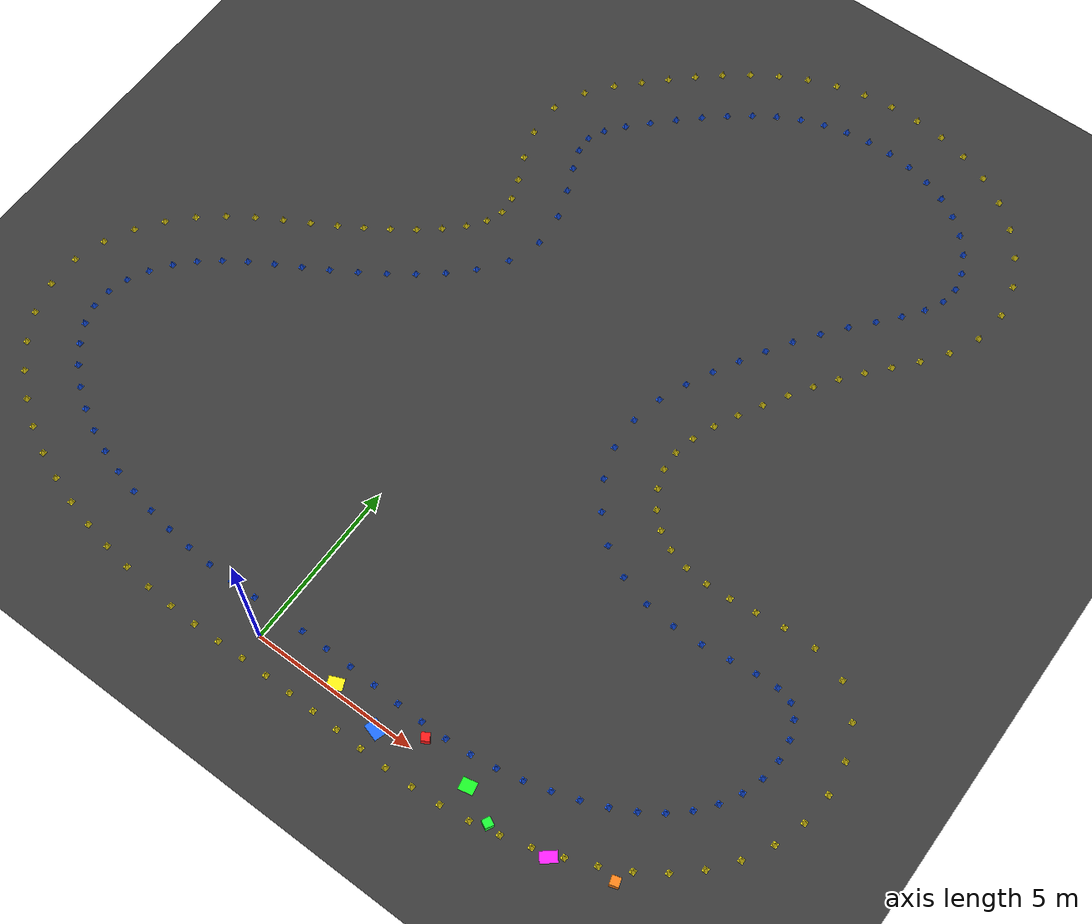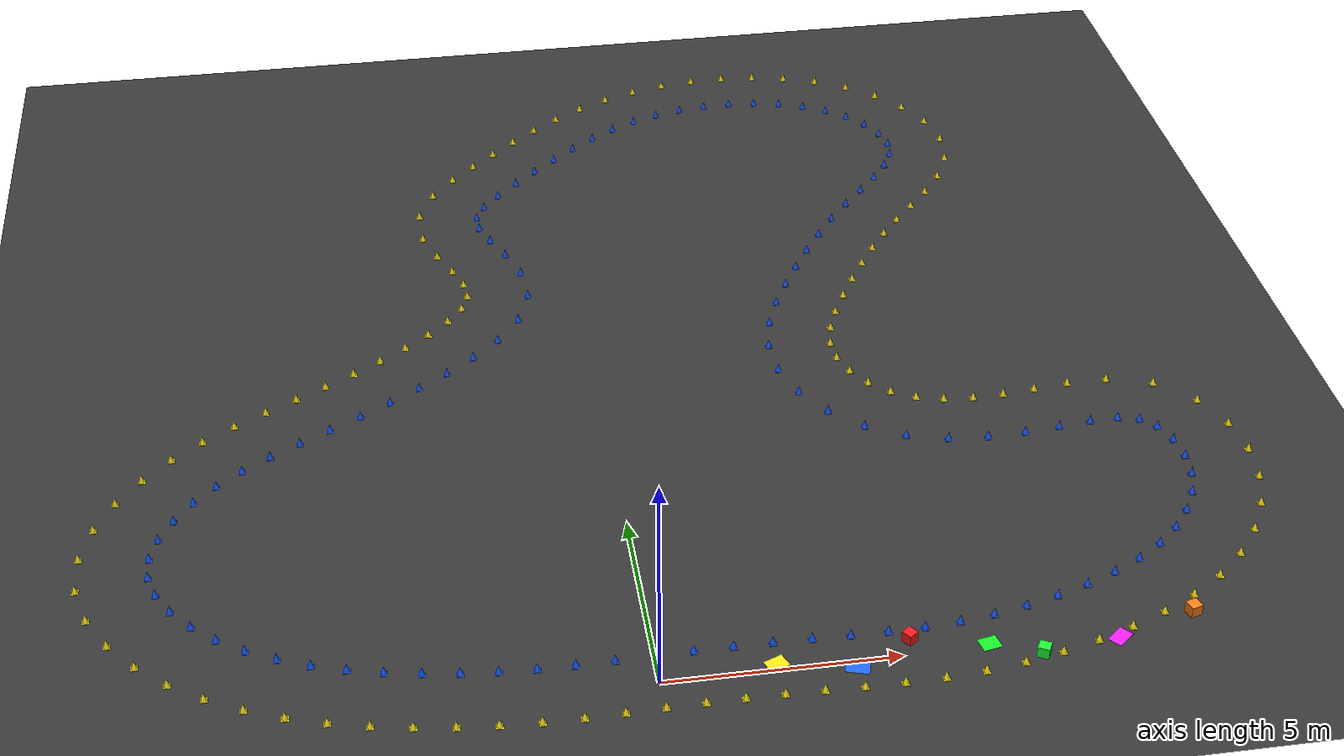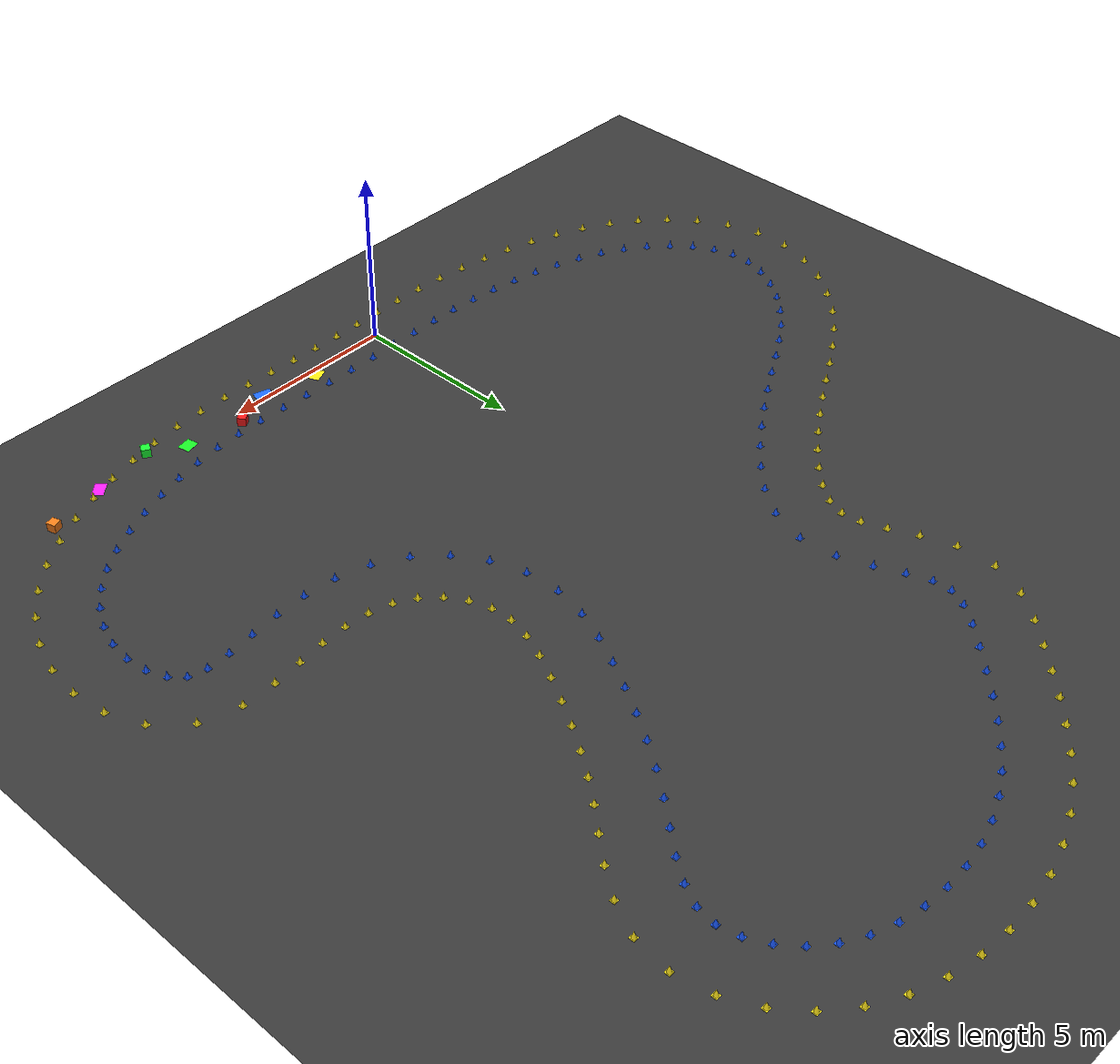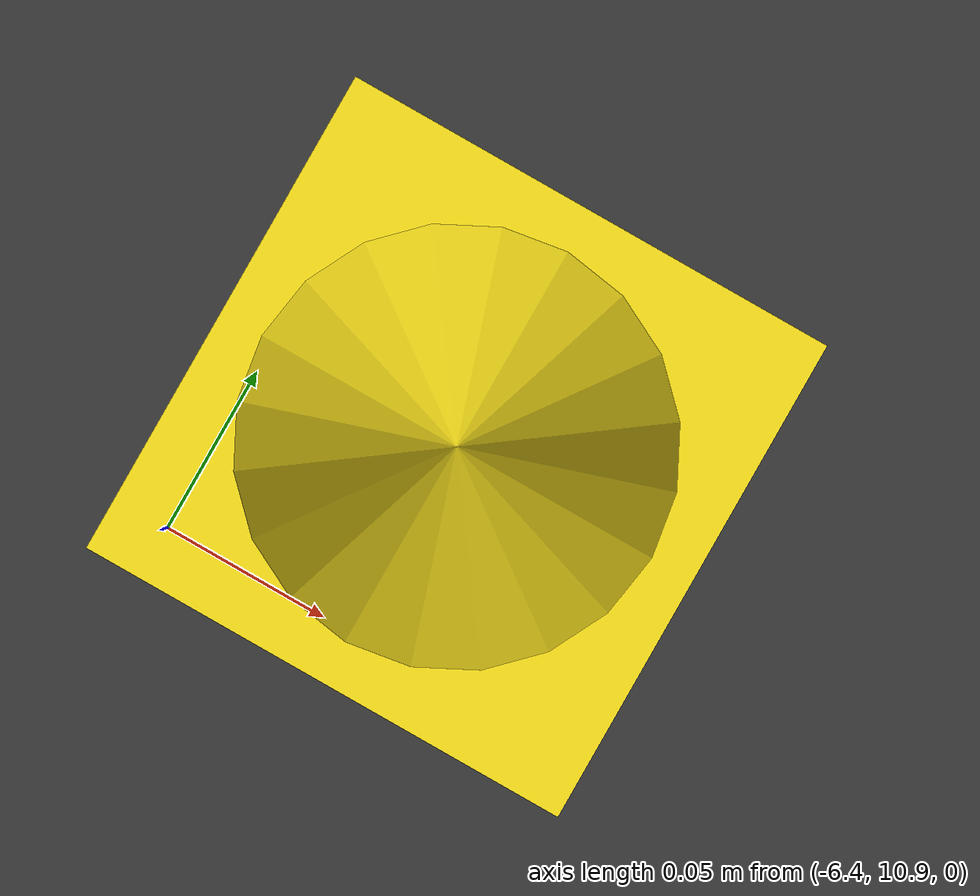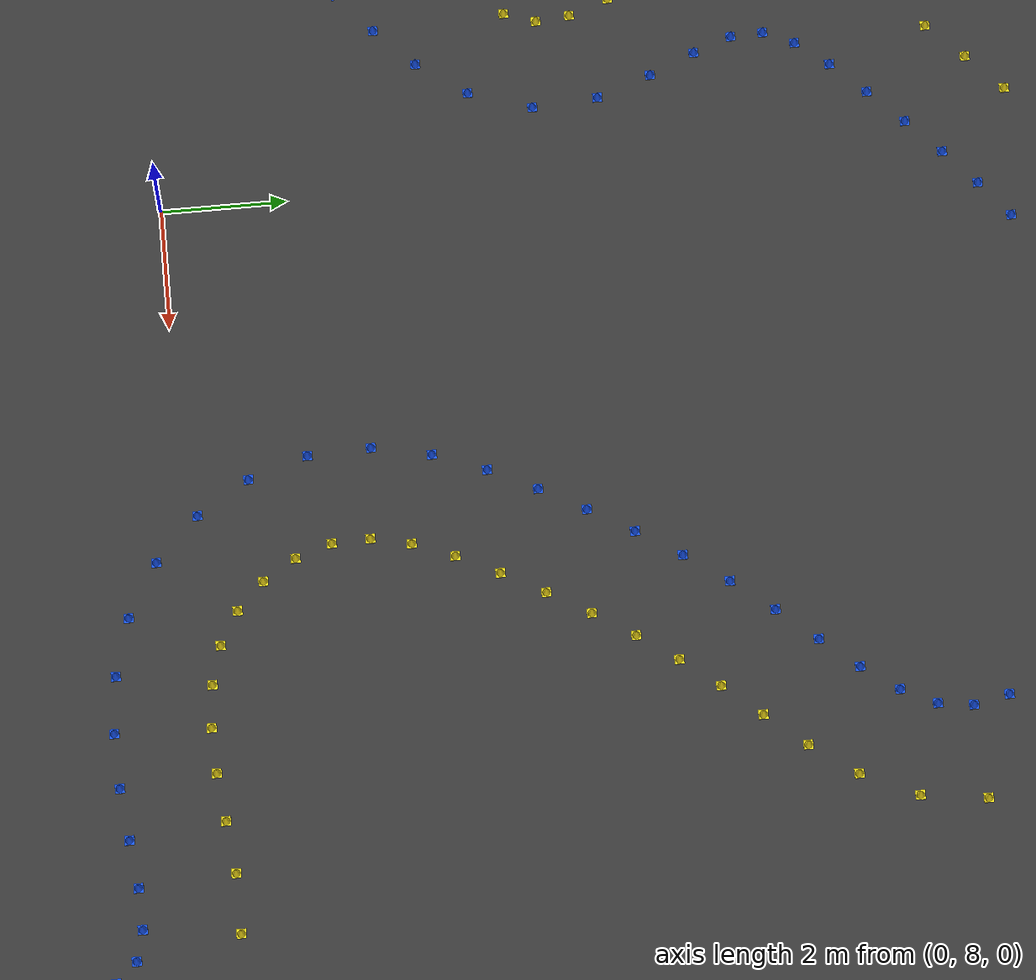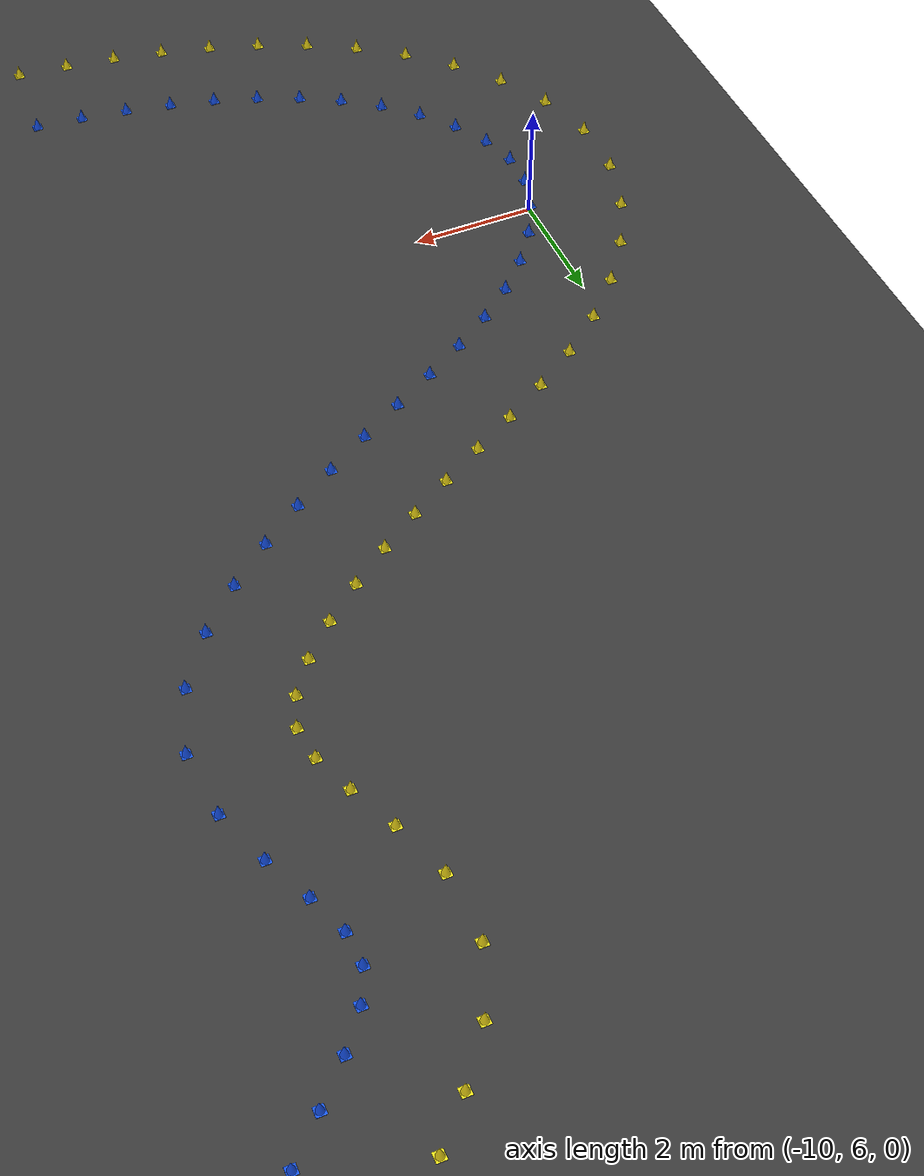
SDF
<?xml version="1.0" ?>
<sdf version="1.8">
  <world name="track_with_cones">
    <physics name="1ms" type="ignored">
      <max_step_size>0.001</max_step_size>
      <real_time_factor>1.0</real_time_factor>
    </physics>
    <plugin
      filename="gz-sim-physics-system"
      name="gz::sim::systems::Physics">
    </plugin>
    <plugin
      filename="gz-sim-user-commands-system"
      name="gz::sim::systems::UserCommands">
    </plugin>
    <plugin
      filename="gz-sim-scene-broadcaster-system"
      name="gz::sim::systems::SceneBroadcaster">
    </plugin>

    <!-- Directional Sun Light -->
    <light type="directional" name="sun">
      <cast_shadows>true</cast_shadows>
      <pose>0 0 20 0 0 0</pose>
      <diffuse>0.9 0.9 0.9 1</diffuse>
      <specular>0.2 0.2 0.2 1</specular>
      <attenuation>
        <range>1000</range>
        <constant>0.9</constant>
        <linear>0.01</linear>
        <quadratic>0.001</quadratic>
      </attenuation>
      <direction>-0.4 0.2 -0.9</direction>
    </light>

    <!-- Ground Plane (Dark Tarmac / Asphalt) -->
    <model name="ground_plane">
      <static>true</static>
      <link name="link">
        <collision name="collision">
          <geometry>
            <plane>
              <normal>0 0 1</normal>
              <size>100 100</size>
            </plane>
          </geometry>
          <surface>
            <friction>
              <ode>
                <mu>100</mu>
                <mu2>100</mu2>
              </ode>
            </friction>
          </surface>
        </collision>
        <visual name="visual">
          <geometry>
            <plane>
              <normal>0 0 1</normal>
              <size>100 100</size>
            </plane>
          </geometry>
          <material>
            <ambient>0.22 0.22 0.22 1</ambient>
            <diffuse>0.22 0.22 0.22 1</diffuse>
            <specular>0.05 0.05 0.05 1</specular>
          </material>
        </visual>
      </link>
    </model>

    <!-- ==================== NOISE POLYGONS (TESTING CAMERA-LIDAR FUSION) ==================== -->
    <!-- 1. Flat Yellow Polygon on Ground (Visual Noise / False Road Marking) -->
    <model name="noise_poly_yellow_ground_1">
      <static>true</static>
      <pose>2.4 0.18 0.001 0 0 0.4</pose>
      <link name="link">
        <visual name="visual">
          <geometry>
            <box><size>0.45 0.35 0.002</size></box>
          </geometry>
          <material>
            <ambient>0.98 0.88 0.05 1.0</ambient>
            <diffuse>1.00 0.92 0.08 1.0</diffuse>
            <specular>0.1 0.1 0.1 1.0</specular>
          </material>
        </visual>
      </link>
    </model>

    <!-- 2. Flat Blue Polygon on Ground (Visual Noise / False Road Marking) -->
    <model name="noise_poly_blue_ground_2">
      <static>true</static>
      <pose>4.0 -0.15 0.001 0 0 -0.3</pose>
      <link name="link">
        <visual name="visual">
          <geometry>
            <box><size>0.50 0.38 0.002</size></box>
          </geometry>
          <material>
            <ambient>0.08 0.35 0.98 1.0</ambient>
            <diffuse>0.12 0.42 1.00 1.0</diffuse>
            <specular>0.1 0.1 0.1 1.0</specular>
          </material>
        </visual>
      </link>
    </model>

    <!-- 3. 3D Red Polygonal Block (Physical Obstacle / Non-Cone Distractor) -->
    <model name="noise_poly_red_3d_1">
      <static>true</static>
      <pose>5.2 0.42 0.125 0 0 0.6</pose>
      <link name="link">
        <visual name="visual">
          <geometry>
            <box><size>0.24 0.24 0.25</size></box>
          </geometry>
          <material>
            <ambient>0.95 0.05 0.05 1.0</ambient>
            <diffuse>1.00 0.10 0.10 1.0</diffuse>
            <specular>0.4 0.4 0.4 1.0</specular>
          </material>
        </visual>
        <collision name="collision">
          <geometry>
            <box><size>0.24 0.24 0.25</size></box>
          </geometry>
        </collision>
      </link>
    </model>

    <!-- 4. Flat Green Polygon on Ground (Visual Noise) -->
    <model name="noise_poly_green_ground_3">
      <static>true</static>
      <pose>6.8 0.10 0.001 0 0 0.2</pose>
      <link name="link">
        <visual name="visual">
          <geometry>
            <box><size>0.42 0.36 0.002</size></box>
          </geometry>
          <material>
            <ambient>0.08 0.88 0.12 1.0</ambient>
            <diffuse>0.10 0.95 0.15 1.0</diffuse>
            <specular>0.1 0.1 0.1 1.0</specular>
          </material>
        </visual>
      </link>
    </model>

    <!-- 5. 3D Green Polygonal Block (Physical Obstacle / Non-Cone Distractor) -->
    <model name="noise_poly_green_3d_2">
      <static>true</static>
      <pose>7.8 -0.38 0.125 0 0 -0.5</pose>
      <link name="link">
        <visual name="visual">
          <geometry>
            <box><size>0.25 0.25 0.25</size></box>
          </geometry>
          <material>
            <ambient>0.05 0.90 0.15 1.0</ambient>
            <diffuse>0.10 0.98 0.20 1.0</diffuse>
            <specular>0.3 0.3 0.3 1.0</specular>
          </material>
        </visual>
        <collision name="collision">
          <geometry>
            <box><size>0.25 0.25 0.25</size></box>
          </geometry>
        </collision>
      </link>
    </model>

    <!-- 6. Flat Magenta Polygon on Ground (Visual Noise) -->
    <model name="noise_poly_magenta_ground_4">
      <static>true</static>
      <pose>9.5 -0.12 0.001 0 0 0.7</pose>
      <link name="link">
        <visual name="visual">
          <geometry>
            <box><size>0.48 0.32 0.002</size></box>
          </geometry>
          <material>
            <ambient>0.88 0.08 0.88 1.0</ambient>
            <diffuse>0.98 0.12 0.98 1.0</diffuse>
            <specular>0.1 0.1 0.1 1.0</specular>
          </material>
        </visual>
      </link>
    </model>

    <!-- 7. 3D Orange/Purple Polygonal Block (Physical Obstacle / Non-Cone Distractor) -->
    <model name="noise_poly_orange_3d_3">
      <static>true</static>
      <pose>11.2 0.35 0.125 0 0 0.3</pose>
      <link name="link">
        <visual name="visual">
          <geometry>
            <box><size>0.26 0.26 0.25</size></box>
          </geometry>
          <material>
            <ambient>0.95 0.45 0.05 1.0</ambient>
            <diffuse>1.00 0.50 0.10 1.0</diffuse>
            <specular>0.3 0.3 0.3 1.0</specular>
          </material>
        </visual>
        <collision name="collision">
          <geometry>
            <box><size>0.26 0.26 0.25</size></box>
          </geometry>
        </collision>
      </link>
    </model>

    <model name="cone_blue_0">
      <static>true</static>
      <pose>-0.0129 0.7499 0.11 0 0 0</pose>
      <link name="link">
        <visual name="base_visual">
          <pose>0 0 -0.105 0 0 0</pose>
          <geometry>
            <box><size>0.15 0.15 0.01</size></box>
          </geometry>
          <material>
            <ambient>0.05 0.25 0.95 1.0</ambient>
            <diffuse>0.10 0.35 1.00 1.0</diffuse>
            <specular>0.2 0.2 0.2 1.0</specular>
          </material>
        </visual>
        <visual name="cone_visual">
          <geometry>
            <cone><radius>0.065</radius><length>0.22</length></cone>
          </geometry>
          <material>
            <ambient>0.05 0.25 0.95 1.0</ambient>
            <diffuse>0.10 0.35 1.00 1.0</diffuse>
            <specular>0.2 0.2 0.2 1.0</specular>
          </material>
        </visual>
        <collision name="collision">
          <geometry>
            <cylinder><radius>0.065</radius><length>0.22</length></cylinder>
          </geometry>
        </collision>
      </link>
    </model>
    <model name="cone_yellow_0">
      <static>true</static>
      <pose>0.0129 -0.7499 0.11 0 0 0</pose>
      <link name="link">
        <visual name="base_visual">
          <pose>0 0 -0.105 0 0 0</pose>
          <geometry>
            <box><size>0.15 0.15 0.01</size></box>
          </geometry>
          <material>
            <ambient>0.95 0.85 0.05 1.0</ambient>
            <diffuse>1.00 0.90 0.10 1.0</diffuse>
            <specular>0.2 0.2 0.2 1.0</specular>
          </material>
        </visual>
        <visual name="cone_visual">
          <geometry>
            <cone><radius>0.065</radius><length>0.22</length></cone>
          </geometry>
          <material>
            <ambient>0.95 0.85 0.05 1.0</ambient>
            <diffuse>1.00 0.90 0.10 1.0</diffuse>
            <specular>0.2 0.2 0.2 1.0</specular>
          </material>
        </visual>
        <collision name="collision">
          <geometry>
            <cylinder><radius>0.065</radius><length>0.22</length></cylinder>
          </geometry>
        </collision>
      </link>
    </model>
    <model name="cone_blue_1">
      <static>true</static>
      <pose>0.7972 0.7638 0.11 0 0 0</pose>
      <link name="link">
        <visual name="base_visual">
          <pose>0 0 -0.105 0 0 0</pose>
          <geometry>
            <box><size>0.15 0.15 0.01</size></box>
          </geometry>
          <material>
            <ambient>0.05 0.25 0.95 1.0</ambient>
            <diffuse>0.10 0.35 1.00 1.0</diffuse>
            <specular>0.2 0.2 0.2 1.0</specular>
          </material>
        </visual>
        <visual name="cone_visual">
          <geometry>
            <cone><radius>0.065</radius><length>0.22</length></cone>
          </geometry>
          <material>
            <ambient>0.05 0.25 0.95 1.0</ambient>
            <diffuse>0.10 0.35 1.00 1.0</diffuse>
            <specular>0.2 0.2 0.2 1.0</specular>
          </material>
        </visual>
        <collision name="collision">
          <geometry>
            <cylinder><radius>0.065</radius><length>0.22</length></cylinder>
          </geometry>
        </collision>
      </link>
    </model>
    <model name="cone_yellow_1">
      <static>true</static>
      <pose>0.8133 -0.7361 0.11 0 0 0</pose>
      <link name="link">
        <visual name="base_visual">
          <pose>0 0 -0.105 0 0 0</pose>
          <geometry>
            <box><size>0.15 0.15 0.01</size></box>
          </geometry>
          <material>
            <ambient>0.95 0.85 0.05 1.0</ambient>
            <diffuse>1.00 0.90 0.10 1.0</diffuse>
            <specular>0.2 0.2 0.2 1.0</specular>
          </material>
        </visual>
        <visual name="cone_visual">
          <geometry>
            <cone><radius>0.065</radius><length>0.22</length></cone>
          </geometry>
          <material>
            <ambient>0.95 0.85 0.05 1.0</ambient>
            <diffuse>1.00 0.90 0.10 1.0</diffuse>
            <specular>0.2 0.2 0.2 1.0</specular>
          </material>
        </visual>
        <collision name="collision">
          <geometry>
            <cylinder><radius>0.065</radius><length>0.22</length></cylinder>
          </geometry>
        </collision>
      </link>
    </model>
    <model name="cone_blue_2">
      <static>true</static>
      <pose>1.6120 0.7673 0.11 0 0 0</pose>
      <link name="link">
        <visual name="base_visual">
          <pose>0 0 -0.105 0 0 0</pose>
          <geometry>
            <box><size>0.15 0.15 0.01</size></box>
          </geometry>
          <material>
            <ambient>0.05 0.25 0.95 1.0</ambient>
            <diffuse>0.10 0.35 1.00 1.0</diffuse>
            <specular>0.2 0.2 0.2 1.0</specular>
          </material>
        </visual>
        <visual name="cone_visual">
          <geometry>
            <cone><radius>0.065</radius><length>0.22</length></cone>
          </geometry>
          <material>
            <ambient>0.05 0.25 0.95 1.0</ambient>
            <diffuse>0.10 0.35 1.00 1.0</diffuse>
            <specular>0.2 0.2 0.2 1.0</specular>
          </material>
        </visual>
        <collision name="collision">
          <geometry>
            <cylinder><radius>0.065</radius><length>0.22</length></cylinder>
          </geometry>
        </collision>
      </link>
    </model>
    <model name="cone_yellow_2">
      <static>true</static>
      <pose>1.6092 -0.7327 0.11 0 0 0</pose>
      <link name="link">
        <visual name="base_visual">
          <pose>0 0 -0.105 0 0 0</pose>
          <geometry>
            <box><size>0.15 0.15 0.01</size></box>
          </geometry>
          <material>
            <ambient>0.95 0.85 0.05 1.0</ambient>
            <diffuse>1.00 0.90 0.10 1.0</diffuse>
            <specular>0.2 0.2 0.2 1.0</specular>
          </material>
        </visual>
        <visual name="cone_visual">
          <geometry>
            <cone><radius>0.065</radius><length>0.22</length></cone>
          </geometry>
          <material>
            <ambient>0.95 0.85 0.05 1.0</ambient>
            <diffuse>1.00 0.90 0.10 1.0</diffuse>
            <specular>0.2 0.2 0.2 1.0</specular>
          </material>
        </visual>
        <collision name="collision">
          <geometry>
            <cylinder><radius>0.065</radius><length>0.22</length></cylinder>
          </geometry>
        </collision>
      </link>
    </model>
    <model name="cone_blue_3">
      <static>true</static>
      <pose>2.4265 0.7608 0.11 0 0 0</pose>
      <link name="link">
        <visual name="base_visual">
          <pose>0 0 -0.105 0 0 0</pose>
          <geometry>
            <box><size>0.15 0.15 0.01</size></box>
          </geometry>
          <material>
            <ambient>0.05 0.25 0.95 1.0</ambient>
            <diffuse>0.10 0.35 1.00 1.0</diffuse>
            <specular>0.2 0.2 0.2 1.0</specular>
          </material>
        </visual>
        <visual name="cone_visual">
          <geometry>
            <cone><radius>0.065</radius><length>0.22</length></cone>
          </geometry>
          <material>
            <ambient>0.05 0.25 0.95 1.0</ambient>
            <diffuse>0.10 0.35 1.00 1.0</diffuse>
            <specular>0.2 0.2 0.2 1.0</specular>
          </material>
        </visual>
        <collision name="collision">
          <geometry>
            <cylinder><radius>0.065</radius><length>0.22</length></cylinder>
          </geometry>
        </collision>
      </link>
    </model>
    <model name="cone_yellow_3">
      <static>true</static>
      <pose>2.4053 -0.7391 0.11 0 0 0</pose>
      <link name="link">
        <visual name="base_visual">
          <pose>0 0 -0.105 0 0 0</pose>
          <geometry>
            <box><size>0.15 0.15 0.01</size></box>
          </geometry>
          <material>
            <ambient>0.95 0.85 0.05 1.0</ambient>
            <diffuse>1.00 0.90 0.10 1.0</diffuse>
            <specular>0.2 0.2 0.2 1.0</specular>
          </material>
        </visual>
        <visual name="cone_visual">
          <geometry>
            <cone><radius>0.065</radius><length>0.22</length></cone>
          </geometry>
          <material>
            <ambient>0.95 0.85 0.05 1.0</ambient>
            <diffuse>1.00 0.90 0.10 1.0</diffuse>
            <specular>0.2 0.2 0.2 1.0</specular>
          </material>
        </visual>
        <collision name="collision">
          <geometry>
            <cylinder><radius>0.065</radius><length>0.22</length></cylinder>
          </geometry>
        </collision>
      </link>
    </model>
    <model name="cone_blue_4">
      <static>true</static>
      <pose>3.2384 0.7444 0.11 0 0 0</pose>
      <link name="link">
        <visual name="base_visual">
          <pose>0 0 -0.105 0 0 0</pose>
          <geometry>
            <box><size>0.15 0.15 0.01</size></box>
          </geometry>
          <material>
            <ambient>0.05 0.25 0.95 1.0</ambient>
            <diffuse>0.10 0.35 1.00 1.0</diffuse>
            <specular>0.2 0.2 0.2 1.0</specular>
          </material>
        </visual>
        <visual name="cone_visual">
          <geometry>
            <cone><radius>0.065</radius><length>0.22</length></cone>
          </geometry>
          <material>
            <ambient>0.05 0.25 0.95 1.0</ambient>
            <diffuse>0.10 0.35 1.00 1.0</diffuse>
            <specular>0.2 0.2 0.2 1.0</specular>
          </material>
        </visual>
        <collision name="collision">
          <geometry>
            <cylinder><radius>0.065</radius><length>0.22</length></cylinder>
          </geometry>
        </collision>
      </link>
    </model>
    <model name="cone_yellow_4">
      <static>true</static>
      <pose>3.2038 -0.7552 0.11 0 0 0</pose>
      <link name="link">
        <visual name="base_visual">
          <pose>0 0 -0.105 0 0 0</pose>
          <geometry>
            <box><size>0.15 0.15 0.01</size></box>
          </geometry>
          <material>
            <ambient>0.95 0.85 0.05 1.0</ambient>
            <diffuse>1.00 0.90 0.10 1.0</diffuse>
            <specular>0.2 0.2 0.2 1.0</specular>
          </material>
        </visual>
        <visual name="cone_visual">
          <geometry>
            <cone><radius>0.065</radius><length>0.22</length></cone>
          </geometry>
          <material>
            <ambient>0.95 0.85 0.05 1.0</ambient>
            <diffuse>1.00 0.90 0.10 1.0</diffuse>
            <specular>0.2 0.2 0.2 1.0</specular>
          </material>
        </visual>
        <collision name="collision">
          <geometry>
            <cylinder><radius>0.065</radius><length>0.22</length></cylinder>
          </geometry>
        </collision>
      </link>
    </model>
    <model name="cone_blue_5">
      <static>true</static>
      <pose>4.0408 0.7236 0.11 0 0 0</pose>
      <link name="link">
        <visual name="base_visual">
          <pose>0 0 -0.105 0 0 0</pose>
          <geometry>
            <box><size>0.15 0.15 0.01</size></box>
          </geometry>
          <material>
            <ambient>0.05 0.25 0.95 1.0</ambient>
            <diffuse>0.10 0.35 1.00 1.0</diffuse>
            <specular>0.2 0.2 0.2 1.0</specular>
          </material>
        </visual>
        <visual name="cone_visual">
          <geometry>
            <cone><radius>0.065</radius><length>0.22</length></cone>
          </geometry>
          <material>
            <ambient>0.05 0.25 0.95 1.0</ambient>
            <diffuse>0.10 0.35 1.00 1.0</diffuse>
            <specular>0.2 0.2 0.2 1.0</specular>
          </material>
        </visual>
        <collision name="collision">
          <geometry>
            <cylinder><radius>0.065</radius><length>0.22</length></cylinder>
          </geometry>
        </collision>
      </link>
    </model>
    <model name="cone_yellow_5">
      <static>true</static>
      <pose>4.0115 -0.7761 0.11 0 0 0</pose>
      <link name="link">
        <visual name="base_visual">
          <pose>0 0 -0.105 0 0 0</pose>
          <geometry>
            <box><size>0.15 0.15 0.01</size></box>
          </geometry>
          <material>
            <ambient>0.95 0.85 0.05 1.0</ambient>
            <diffuse>1.00 0.90 0.10 1.0</diffuse>
            <specular>0.2 0.2 0.2 1.0</specular>
          </material>
        </visual>
        <visual name="cone_visual">
          <geometry>
            <cone><radius>0.065</radius><length>0.22</length></cone>
          </geometry>
          <material>
            <ambient>0.95 0.85 0.05 1.0</ambient>
            <diffuse>1.00 0.90 0.10 1.0</diffuse>
            <specular>0.2 0.2 0.2 1.0</specular>
          </material>
        </visual>
        <collision name="collision">
          <geometry>
            <cylinder><radius>0.065</radius><length>0.22</length></cylinder>
          </geometry>
        </collision>
      </link>
    </model>
    <model name="cone_blue_6">
      <static>true</static>
      <pose>4.8288 0.7131 0.11 0 0 0</pose>
      <link name="link">
        <visual name="base_visual">
          <pose>0 0 -0.105 0 0 0</pose>
          <geometry>
            <box><size>0.15 0.15 0.01</size></box>
          </geometry>
          <material>
            <ambient>0.05 0.25 0.95 1.0</ambient>
            <diffuse>0.10 0.35 1.00 1.0</diffuse>
            <specular>0.2 0.2 0.2 1.0</specular>
          </material>
        </visual>
        <visual name="cone_visual">
          <geometry>
            <cone><radius>0.065</radius><length>0.22</length></cone>
          </geometry>
          <material>
            <ambient>0.05 0.25 0.95 1.0</ambient>
            <diffuse>0.10 0.35 1.00 1.0</diffuse>
            <specular>0.2 0.2 0.2 1.0</specular>
          </material>
        </visual>
        <collision name="collision">
          <geometry>
            <cylinder><radius>0.065</radius><length>0.22</length></cylinder>
          </geometry>
        </collision>
      </link>
    </model>
    <model name="cone_yellow_6">
      <static>true</static>
      <pose>4.8341 -0.7869 0.11 0 0 0</pose>
      <link name="link">
        <visual name="base_visual">
          <pose>0 0 -0.105 0 0 0</pose>
          <geometry>
            <box><size>0.15 0.15 0.01</size></box>
          </geometry>
          <material>
            <ambient>0.95 0.85 0.05 1.0</ambient>
            <diffuse>1.00 0.90 0.10 1.0</diffuse>
            <specular>0.2 0.2 0.2 1.0</specular>
          </material>
        </visual>
        <visual name="cone_visual">
          <geometry>
            <cone><radius>0.065</radius><length>0.22</length></cone>
          </geometry>
          <material>
            <ambient>0.95 0.85 0.05 1.0</ambient>
            <diffuse>1.00 0.90 0.10 1.0</diffuse>
            <specular>0.2 0.2 0.2 1.0</specular>
          </material>
        </visual>
        <collision name="collision">
          <geometry>
            <cylinder><radius>0.065</radius><length>0.22</length></cylinder>
          </geometry>
        </collision>
      </link>
    </model>
    <model name="cone_blue_7">
      <static>true</static>
      <pose>5.6012 0.7285 0.11 0 0 0</pose>
      <link name="link">
        <visual name="base_visual">
          <pose>0 0 -0.105 0 0 0</pose>
          <geometry>
            <box><size>0.15 0.15 0.01</size></box>
          </geometry>
          <material>
            <ambient>0.05 0.25 0.95 1.0</ambient>
            <diffuse>0.10 0.35 1.00 1.0</diffuse>
            <specular>0.2 0.2 0.2 1.0</specular>
          </material>
        </visual>
        <visual name="cone_visual">
          <geometry>
            <cone><radius>0.065</radius><length>0.22</length></cone>
          </geometry>
          <material>
            <ambient>0.05 0.25 0.95 1.0</ambient>
            <diffuse>0.10 0.35 1.00 1.0</diffuse>
            <specular>0.2 0.2 0.2 1.0</specular>
          </material>
        </visual>
        <collision name="collision">
          <geometry>
            <cylinder><radius>0.065</radius><length>0.22</length></cylinder>
          </geometry>
        </collision>
      </link>
    </model>
    <model name="cone_yellow_7">
      <static>true</static>
      <pose>5.6720 -0.7698 0.11 0 0 0</pose>
      <link name="link">
        <visual name="base_visual">
          <pose>0 0 -0.105 0 0 0</pose>
          <geometry>
            <box><size>0.15 0.15 0.01</size></box>
          </geometry>
          <material>
            <ambient>0.95 0.85 0.05 1.0</ambient>
            <diffuse>1.00 0.90 0.10 1.0</diffuse>
            <specular>0.2 0.2 0.2 1.0</specular>
          </material>
        </visual>
        <visual name="cone_visual">
          <geometry>
            <cone><radius>0.065</radius><length>0.22</length></cone>
          </geometry>
          <material>
            <ambient>0.95 0.85 0.05 1.0</ambient>
            <diffuse>1.00 0.90 0.10 1.0</diffuse>
            <specular>0.2 0.2 0.2 1.0</specular>
          </material>
        </visual>
        <collision name="collision">
          <geometry>
            <cylinder><radius>0.065</radius><length>0.22</length></cylinder>
          </geometry>
        </collision>
      </link>
    </model>
    <model name="cone_blue_8">
      <static>true</static>
      <pose>6.3592 0.7847 0.11 0 0 0</pose>
      <link name="link">
        <visual name="base_visual">
          <pose>0 0 -0.105 0 0 0</pose>
          <geometry>
            <box><size>0.15 0.15 0.01</size></box>
          </geometry>
          <material>
            <ambient>0.05 0.25 0.95 1.0</ambient>
            <diffuse>0.10 0.35 1.00 1.0</diffuse>
            <specular>0.2 0.2 0.2 1.0</specular>
          </material>
        </visual>
        <visual name="cone_visual">
          <geometry>
            <cone><radius>0.065</radius><length>0.22</length></cone>
          </geometry>
          <material>
            <ambient>0.05 0.25 0.95 1.0</ambient>
            <diffuse>0.10 0.35 1.00 1.0</diffuse>
            <specular>0.2 0.2 0.2 1.0</specular>
          </material>
        </visual>
        <collision name="collision">
          <geometry>
            <cylinder><radius>0.065</radius><length>0.22</length></cylinder>
          </geometry>
        </collision>
      </link>
    </model>
    <model name="cone_yellow_8">
      <static>true</static>
      <pose>6.5200 -0.7066 0.11 0 0 0</pose>
      <link name="link">
        <visual name="base_visual">
          <pose>0 0 -0.105 0 0 0</pose>
          <geometry>
            <box><size>0.15 0.15 0.01</size></box>
          </geometry>
          <material>
            <ambient>0.95 0.85 0.05 1.0</ambient>
            <diffuse>1.00 0.90 0.10 1.0</diffuse>
            <specular>0.2 0.2 0.2 1.0</specular>
          </material>
        </visual>
        <visual name="cone_visual">
          <geometry>
            <cone><radius>0.065</radius><length>0.22</length></cone>
          </geometry>
          <material>
            <ambient>0.95 0.85 0.05 1.0</ambient>
            <diffuse>1.00 0.90 0.10 1.0</diffuse>
            <specular>0.2 0.2 0.2 1.0</specular>
          </material>
        </visual>
        <collision name="collision">
          <geometry>
            <cylinder><radius>0.065</radius><length>0.22</length></cylinder>
          </geometry>
        </collision>
      </link>
    </model>
    <model name="cone_blue_9">
      <static>true</static>
      <pose>7.1066 0.8905 0.11 0 0 0</pose>
      <link name="link">
        <visual name="base_visual">
          <pose>0 0 -0.105 0 0 0</pose>
          <geometry>
            <box><size>0.15 0.15 0.01</size></box>
          </geometry>
          <material>
            <ambient>0.05 0.25 0.95 1.0</ambient>
            <diffuse>0.10 0.35 1.00 1.0</diffuse>
            <specular>0.2 0.2 0.2 1.0</specular>
          </material>
        </visual>
        <visual name="cone_visual">
          <geometry>
            <cone><radius>0.065</radius><length>0.22</length></cone>
          </geometry>
          <material>
            <ambient>0.05 0.25 0.95 1.0</ambient>
            <diffuse>0.10 0.35 1.00 1.0</diffuse>
            <specular>0.2 0.2 0.2 1.0</specular>
          </material>
        </visual>
        <collision name="collision">
          <geometry>
            <cylinder><radius>0.065</radius><length>0.22</length></cylinder>
          </geometry>
        </collision>
      </link>
    </model>
    <model name="cone_yellow_9">
      <static>true</static>
      <pose>7.3671 -0.5867 0.11 0 0 0</pose>
      <link name="link">
        <visual name="base_visual">
          <pose>0 0 -0.105 0 0 0</pose>
          <geometry>
            <box><size>0.15 0.15 0.01</size></box>
          </geometry>
          <material>
            <ambient>0.95 0.85 0.05 1.0</ambient>
            <diffuse>1.00 0.90 0.10 1.0</diffuse>
            <specular>0.2 0.2 0.2 1.0</specular>
          </material>
        </visual>
        <visual name="cone_visual">
          <geometry>
            <cone><radius>0.065</radius><length>0.22</length></cone>
          </geometry>
          <material>
            <ambient>0.95 0.85 0.05 1.0</ambient>
            <diffuse>1.00 0.90 0.10 1.0</diffuse>
            <specular>0.2 0.2 0.2 1.0</specular>
          </material>
        </visual>
        <collision name="collision">
          <geometry>
            <cylinder><radius>0.065</radius><length>0.22</length></cylinder>
          </geometry>
        </collision>
      </link>
    </model>
    <model name="cone_blue_10">
      <static>true</static>
      <pose>7.8458 1.0470 0.11 0 0 0</pose>
      <link name="link">
        <visual name="base_visual">
          <pose>0 0 -0.105 0 0 0</pose>
          <geometry>
            <box><size>0.15 0.15 0.01</size></box>
          </geometry>
          <material>
            <ambient>0.05 0.25 0.95 1.0</ambient>
            <diffuse>0.10 0.35 1.00 1.0</diffuse>
            <specular>0.2 0.2 0.2 1.0</specular>
          </material>
        </visual>
        <visual name="cone_visual">
          <geometry>
            <cone><radius>0.065</radius><length>0.22</length></cone>
          </geometry>
          <material>
            <ambient>0.05 0.25 0.95 1.0</ambient>
            <diffuse>0.10 0.35 1.00 1.0</diffuse>
            <specular>0.2 0.2 0.2 1.0</specular>
          </material>
        </visual>
        <collision name="collision">
          <geometry>
            <cylinder><radius>0.065</radius><length>0.22</length></cylinder>
          </geometry>
        </collision>
      </link>
    </model>
    <model name="cone_yellow_10">
      <static>true</static>
      <pose>8.2035 -0.4098 0.11 0 0 0</pose>
      <link name="link">
        <visual name="base_visual">
          <pose>0 0 -0.105 0 0 0</pose>
          <geometry>
            <box><size>0.15 0.15 0.01</size></box>
          </geometry>
          <material>
            <ambient>0.95 0.85 0.05 1.0</ambient>
            <diffuse>1.00 0.90 0.10 1.0</diffuse>
            <specular>0.2 0.2 0.2 1.0</specular>
          </material>
        </visual>
        <visual name="cone_visual">
          <geometry>
            <cone><radius>0.065</radius><length>0.22</length></cone>
          </geometry>
          <material>
            <ambient>0.95 0.85 0.05 1.0</ambient>
            <diffuse>1.00 0.90 0.10 1.0</diffuse>
            <specular>0.2 0.2 0.2 1.0</specular>
          </material>
        </visual>
        <collision name="collision">
          <geometry>
            <cylinder><radius>0.065</radius><length>0.22</length></cylinder>
          </geometry>
        </collision>
      </link>
    </model>
    <model name="cone_blue_11">
      <static>true</static>
      <pose>8.5763 1.2516 0.11 0 0 0</pose>
      <link name="link">
        <visual name="base_visual">
          <pose>0 0 -0.105 0 0 0</pose>
          <geometry>
            <box><size>0.15 0.15 0.01</size></box>
          </geometry>
          <material>
            <ambient>0.05 0.25 0.95 1.0</ambient>
            <diffuse>0.10 0.35 1.00 1.0</diffuse>
            <specular>0.2 0.2 0.2 1.0</specular>
          </material>
        </visual>
        <visual name="cone_visual">
          <geometry>
            <cone><radius>0.065</radius><length>0.22</length></cone>
          </geometry>
          <material>
            <ambient>0.05 0.25 0.95 1.0</ambient>
            <diffuse>0.10 0.35 1.00 1.0</diffuse>
            <specular>0.2 0.2 0.2 1.0</specular>
          </material>
        </visual>
        <collision name="collision">
          <geometry>
            <cylinder><radius>0.065</radius><length>0.22</length></cylinder>
          </geometry>
        </collision>
      </link>
    </model>
    <model name="cone_yellow_11">
      <static>true</static>
      <pose>9.0237 -0.1801 0.11 0 0 0</pose>
      <link name="link">
        <visual name="base_visual">
          <pose>0 0 -0.105 0 0 0</pose>
          <geometry>
            <box><size>0.15 0.15 0.01</size></box>
          </geometry>
          <material>
            <ambient>0.95 0.85 0.05 1.0</ambient>
            <diffuse>1.00 0.90 0.10 1.0</diffuse>
            <specular>0.2 0.2 0.2 1.0</specular>
          </material>
        </visual>
        <visual name="cone_visual">
          <geometry>
            <cone><radius>0.065</radius><length>0.22</length></cone>
          </geometry>
          <material>
            <ambient>0.95 0.85 0.05 1.0</ambient>
            <diffuse>1.00 0.90 0.10 1.0</diffuse>
            <specular>0.2 0.2 0.2 1.0</specular>
          </material>
        </visual>
        <collision name="collision">
          <geometry>
            <cylinder><radius>0.065</radius><length>0.22</length></cylinder>
          </geometry>
        </collision>
      </link>
    </model>
    <model name="cone_blue_12">
      <static>true</static>
      <pose>9.2926 1.4990 0.11 0 0 0</pose>
      <link name="link">
        <visual name="base_visual">
          <pose>0 0 -0.105 0 0 0</pose>
          <geometry>
            <box><size>0.15 0.15 0.01</size></box>
          </geometry>
          <material>
            <ambient>0.05 0.25 0.95 1.0</ambient>
            <diffuse>0.10 0.35 1.00 1.0</diffuse>
            <specular>0.2 0.2 0.2 1.0</specular>
          </material>
        </visual>
        <visual name="cone_visual">
          <geometry>
            <cone><radius>0.065</radius><length>0.22</length></cone>
          </geometry>
          <material>
            <ambient>0.05 0.25 0.95 1.0</ambient>
            <diffuse>0.10 0.35 1.00 1.0</diffuse>
            <specular>0.2 0.2 0.2 1.0</specular>
          </material>
        </visual>
        <collision name="collision">
          <geometry>
            <cylinder><radius>0.065</radius><length>0.22</length></cylinder>
          </geometry>
        </collision>
      </link>
    </model>
    <model name="cone_yellow_12">
      <static>true</static>
      <pose>9.8296 0.0984 0.11 0 0 0</pose>
      <link name="link">
        <visual name="base_visual">
          <pose>0 0 -0.105 0 0 0</pose>
          <geometry>
            <box><size>0.15 0.15 0.01</size></box>
          </geometry>
          <material>
            <ambient>0.95 0.85 0.05 1.0</ambient>
            <diffuse>1.00 0.90 0.10 1.0</diffuse>
            <specular>0.2 0.2 0.2 1.0</specular>
          </material>
        </visual>
        <visual name="cone_visual">
          <geometry>
            <cone><radius>0.065</radius><length>0.22</length></cone>
          </geometry>
          <material>
            <ambient>0.95 0.85 0.05 1.0</ambient>
            <diffuse>1.00 0.90 0.10 1.0</diffuse>
            <specular>0.2 0.2 0.2 1.0</specular>
          </material>
        </visual>
        <collision name="collision">
          <geometry>
            <cylinder><radius>0.065</radius><length>0.22</length></cylinder>
          </geometry>
        </collision>
      </link>
    </model>
    <model name="cone_blue_13">
      <static>true</static>
      <pose>9.9821 1.7899 0.11 0 0 0</pose>
      <link name="link">
        <visual name="base_visual">
          <pose>0 0 -0.105 0 0 0</pose>
          <geometry>
            <box><size>0.15 0.15 0.01</size></box>
          </geometry>
          <material>
            <ambient>0.05 0.25 0.95 1.0</ambient>
            <diffuse>0.10 0.35 1.00 1.0</diffuse>
            <specular>0.2 0.2 0.2 1.0</specular>
          </material>
        </visual>
        <visual name="cone_visual">
          <geometry>
            <cone><radius>0.065</radius><length>0.22</length></cone>
          </geometry>
          <material>
            <ambient>0.05 0.25 0.95 1.0</ambient>
            <diffuse>0.10 0.35 1.00 1.0</diffuse>
            <specular>0.2 0.2 0.2 1.0</specular>
          </material>
        </visual>
        <collision name="collision">
          <geometry>
            <cylinder><radius>0.065</radius><length>0.22</length></cylinder>
          </geometry>
        </collision>
      </link>
    </model>
    <model name="cone_yellow_13">
      <static>true</static>
      <pose>10.6236 0.4340 0.11 0 0 0</pose>
      <link name="link">
        <visual name="base_visual">
          <pose>0 0 -0.105 0 0 0</pose>
          <geometry>
            <box><size>0.15 0.15 0.01</size></box>
          </geometry>
          <material>
            <ambient>0.95 0.85 0.05 1.0</ambient>
            <diffuse>1.00 0.90 0.10 1.0</diffuse>
            <specular>0.2 0.2 0.2 1.0</specular>
          </material>
        </visual>
        <visual name="cone_visual">
          <geometry>
            <cone><radius>0.065</radius><length>0.22</length></cone>
          </geometry>
          <material>
            <ambient>0.95 0.85 0.05 1.0</ambient>
            <diffuse>1.00 0.90 0.10 1.0</diffuse>
            <specular>0.2 0.2 0.2 1.0</specular>
          </material>
        </visual>
        <collision name="collision">
          <geometry>
            <cylinder><radius>0.065</radius><length>0.22</length></cylinder>
          </geometry>
        </collision>
      </link>
    </model>
    <model name="cone_blue_14">
      <static>true</static>
      <pose>10.6308 2.1306 0.11 0 0 0</pose>
      <link name="link">
        <visual name="base_visual">
          <pose>0 0 -0.105 0 0 0</pose>
          <geometry>
            <box><size>0.15 0.15 0.01</size></box>
          </geometry>
          <material>
            <ambient>0.05 0.25 0.95 1.0</ambient>
            <diffuse>0.10 0.35 1.00 1.0</diffuse>
            <specular>0.2 0.2 0.2 1.0</specular>
          </material>
        </visual>
        <visual name="cone_visual">
          <geometry>
            <cone><radius>0.065</radius><length>0.22</length></cone>
          </geometry>
          <material>
            <ambient>0.05 0.25 0.95 1.0</ambient>
            <diffuse>0.10 0.35 1.00 1.0</diffuse>
            <specular>0.2 0.2 0.2 1.0</specular>
          </material>
        </visual>
        <collision name="collision">
          <geometry>
            <cylinder><radius>0.065</radius><length>0.22</length></cylinder>
          </geometry>
        </collision>
      </link>
    </model>
    <model name="cone_yellow_14">
      <static>true</static>
      <pose>11.3999 0.8428 0.11 0 0 0</pose>
      <link name="link">
        <visual name="base_visual">
          <pose>0 0 -0.105 0 0 0</pose>
          <geometry>
            <box><size>0.15 0.15 0.01</size></box>
          </geometry>
          <material>
            <ambient>0.95 0.85 0.05 1.0</ambient>
            <diffuse>1.00 0.90 0.10 1.0</diffuse>
            <specular>0.2 0.2 0.2 1.0</specular>
          </material>
        </visual>
        <visual name="cone_visual">
          <geometry>
            <cone><radius>0.065</radius><length>0.22</length></cone>
          </geometry>
          <material>
            <ambient>0.95 0.85 0.05 1.0</ambient>
            <diffuse>1.00 0.90 0.10 1.0</diffuse>
            <specular>0.2 0.2 0.2 1.0</specular>
          </material>
        </visual>
        <collision name="collision">
          <geometry>
            <cylinder><radius>0.065</radius><length>0.22</length></cylinder>
          </geometry>
        </collision>
      </link>
    </model>
    <model name="cone_blue_15">
      <static>true</static>
      <pose>11.2218 2.5278 0.11 0 0 0</pose>
      <link name="link">
        <visual name="base_visual">
          <pose>0 0 -0.105 0 0 0</pose>
          <geometry>
            <box><size>0.15 0.15 0.01</size></box>
          </geometry>
          <material>
            <ambient>0.05 0.25 0.95 1.0</ambient>
            <diffuse>0.10 0.35 1.00 1.0</diffuse>
            <specular>0.2 0.2 0.2 1.0</specular>
          </material>
        </visual>
        <visual name="cone_visual">
          <geometry>
            <cone><radius>0.065</radius><length>0.22</length></cone>
          </geometry>
          <material>
            <ambient>0.05 0.25 0.95 1.0</ambient>
            <diffuse>0.10 0.35 1.00 1.0</diffuse>
            <specular>0.2 0.2 0.2 1.0</specular>
          </material>
        </visual>
        <collision name="collision">
          <geometry>
            <cylinder><radius>0.065</radius><length>0.22</length></cylinder>
          </geometry>
        </collision>
      </link>
    </model>
    <model name="cone_yellow_15">
      <static>true</static>
      <pose>12.1441 1.3448 0.11 0 0 0</pose>
      <link name="link">
        <visual name="base_visual">
          <pose>0 0 -0.105 0 0 0</pose>
          <geometry>
            <box><size>0.15 0.15 0.01</size></box>
          </geometry>
          <material>
            <ambient>0.95 0.85 0.05 1.0</ambient>
            <diffuse>1.00 0.90 0.10 1.0</diffuse>
            <specular>0.2 0.2 0.2 1.0</specular>
          </material>
        </visual>
        <visual name="cone_visual">
          <geometry>
            <cone><radius>0.065</radius><length>0.22</length></cone>
          </geometry>
          <material>
            <ambient>0.95 0.85 0.05 1.0</ambient>
            <diffuse>1.00 0.90 0.10 1.0</diffuse>
            <specular>0.2 0.2 0.2 1.0</specular>
          </material>
        </visual>
        <collision name="collision">
          <geometry>
            <cylinder><radius>0.065</radius><length>0.22</length></cylinder>
          </geometry>
        </collision>
      </link>
    </model>
    <model name="cone_blue_16">
      <static>true</static>
      <pose>11.7374 2.9900 0.11 0 0 0</pose>
      <link name="link">
        <visual name="base_visual">
          <pose>0 0 -0.105 0 0 0</pose>
          <geometry>
            <box><size>0.15 0.15 0.01</size></box>
          </geometry>
          <material>
            <ambient>0.05 0.25 0.95 1.0</ambient>
            <diffuse>0.10 0.35 1.00 1.0</diffuse>
            <specular>0.2 0.2 0.2 1.0</specular>
          </material>
        </visual>
        <visual name="cone_visual">
          <geometry>
            <cone><radius>0.065</radius><length>0.22</length></cone>
          </geometry>
          <material>
            <ambient>0.05 0.25 0.95 1.0</ambient>
            <diffuse>0.10 0.35 1.00 1.0</diffuse>
            <specular>0.2 0.2 0.2 1.0</specular>
          </material>
        </visual>
        <collision name="collision">
          <geometry>
            <cylinder><radius>0.065</radius><length>0.22</length></cylinder>
          </geometry>
        </collision>
      </link>
    </model>
    <model name="cone_yellow_16">
      <static>true</static>
      <pose>12.8257 1.9577 0.11 0 0 0</pose>
      <link name="link">
        <visual name="base_visual">
          <pose>0 0 -0.105 0 0 0</pose>
          <geometry>
            <box><size>0.15 0.15 0.01</size></box>
          </geometry>
          <material>
            <ambient>0.95 0.85 0.05 1.0</ambient>
            <diffuse>1.00 0.90 0.10 1.0</diffuse>
            <specular>0.2 0.2 0.2 1.0</specular>
          </material>
        </visual>
        <visual name="cone_visual">
          <geometry>
            <cone><radius>0.065</radius><length>0.22</length></cone>
          </geometry>
          <material>
            <ambient>0.95 0.85 0.05 1.0</ambient>
            <diffuse>1.00 0.90 0.10 1.0</diffuse>
            <specular>0.2 0.2 0.2 1.0</specular>
          </material>
        </visual>
        <collision name="collision">
          <geometry>
            <cylinder><radius>0.065</radius><length>0.22</length></cylinder>
          </geometry>
        </collision>
      </link>
    </model>
    <model name="cone_blue_17">
      <static>true</static>
      <pose>12.1648 3.5193 0.11 0 0 0</pose>
      <link name="link">
        <visual name="base_visual">
          <pose>0 0 -0.105 0 0 0</pose>
          <geometry>
            <box><size>0.15 0.15 0.01</size></box>
          </geometry>
          <material>
            <ambient>0.05 0.25 0.95 1.0</ambient>
            <diffuse>0.10 0.35 1.00 1.0</diffuse>
            <specular>0.2 0.2 0.2 1.0</specular>
          </material>
        </visual>
        <visual name="cone_visual">
          <geometry>
            <cone><radius>0.065</radius><length>0.22</length></cone>
          </geometry>
          <material>
            <ambient>0.05 0.25 0.95 1.0</ambient>
            <diffuse>0.10 0.35 1.00 1.0</diffuse>
            <specular>0.2 0.2 0.2 1.0</specular>
          </material>
        </visual>
        <collision name="collision">
          <geometry>
            <cylinder><radius>0.065</radius><length>0.22</length></cylinder>
          </geometry>
        </collision>
      </link>
    </model>
    <model name="cone_yellow_17">
      <static>true</static>
      <pose>13.4085 2.6806 0.11 0 0 0</pose>
      <link name="link">
        <visual name="base_visual">
          <pose>0 0 -0.105 0 0 0</pose>
          <geometry>
            <box><size>0.15 0.15 0.01</size></box>
          </geometry>
          <material>
            <ambient>0.95 0.85 0.05 1.0</ambient>
            <diffuse>1.00 0.90 0.10 1.0</diffuse>
            <specular>0.2 0.2 0.2 1.0</specular>
          </material>
        </visual>
        <visual name="cone_visual">
          <geometry>
            <cone><radius>0.065</radius><length>0.22</length></cone>
          </geometry>
          <material>
            <ambient>0.95 0.85 0.05 1.0</ambient>
            <diffuse>1.00 0.90 0.10 1.0</diffuse>
            <specular>0.2 0.2 0.2 1.0</specular>
          </material>
        </visual>
        <collision name="collision">
          <geometry>
            <cylinder><radius>0.065</radius><length>0.22</length></cylinder>
          </geometry>
        </collision>
      </link>
    </model>
    <model name="cone_blue_18">
      <static>true</static>
      <pose>12.4911 4.1043 0.11 0 0 0</pose>
      <link name="link">
        <visual name="base_visual">
          <pose>0 0 -0.105 0 0 0</pose>
          <geometry>
            <box><size>0.15 0.15 0.01</size></box>
          </geometry>
          <material>
            <ambient>0.05 0.25 0.95 1.0</ambient>
            <diffuse>0.10 0.35 1.00 1.0</diffuse>
            <specular>0.2 0.2 0.2 1.0</specular>
          </material>
        </visual>
        <visual name="cone_visual">
          <geometry>
            <cone><radius>0.065</radius><length>0.22</length></cone>
          </geometry>
          <material>
            <ambient>0.05 0.25 0.95 1.0</ambient>
            <diffuse>0.10 0.35 1.00 1.0</diffuse>
            <specular>0.2 0.2 0.2 1.0</specular>
          </material>
        </visual>
        <collision name="collision">
          <geometry>
            <cylinder><radius>0.065</radius><length>0.22</length></cylinder>
          </geometry>
        </collision>
      </link>
    </model>
    <model name="cone_yellow_18">
      <static>true</static>
      <pose>13.8645 3.5012 0.11 0 0 0</pose>
      <link name="link">
        <visual name="base_visual">
          <pose>0 0 -0.105 0 0 0</pose>
          <geometry>
            <box><size>0.15 0.15 0.01</size></box>
          </geometry>
          <material>
            <ambient>0.95 0.85 0.05 1.0</ambient>
            <diffuse>1.00 0.90 0.10 1.0</diffuse>
            <specular>0.2 0.2 0.2 1.0</specular>
          </material>
        </visual>
        <visual name="cone_visual">
          <geometry>
            <cone><radius>0.065</radius><length>0.22</length></cone>
          </geometry>
          <material>
            <ambient>0.95 0.85 0.05 1.0</ambient>
            <diffuse>1.00 0.90 0.10 1.0</diffuse>
            <specular>0.2 0.2 0.2 1.0</specular>
          </material>
        </visual>
        <collision name="collision">
          <geometry>
            <cylinder><radius>0.065</radius><length>0.22</length></cylinder>
          </geometry>
        </collision>
      </link>
    </model>
    <model name="cone_blue_19">
      <static>true</static>
      <pose>12.6975 4.7254 0.11 0 0 0</pose>
      <link name="link">
        <visual name="base_visual">
          <pose>0 0 -0.105 0 0 0</pose>
          <geometry>
            <box><size>0.15 0.15 0.01</size></box>
          </geometry>
          <material>
            <ambient>0.05 0.25 0.95 1.0</ambient>
            <diffuse>0.10 0.35 1.00 1.0</diffuse>
            <specular>0.2 0.2 0.2 1.0</specular>
          </material>
        </visual>
        <visual name="cone_visual">
          <geometry>
            <cone><radius>0.065</radius><length>0.22</length></cone>
          </geometry>
          <material>
            <ambient>0.05 0.25 0.95 1.0</ambient>
            <diffuse>0.10 0.35 1.00 1.0</diffuse>
            <specular>0.2 0.2 0.2 1.0</specular>
          </material>
        </visual>
        <collision name="collision">
          <geometry>
            <cylinder><radius>0.065</radius><length>0.22</length></cylinder>
          </geometry>
        </collision>
      </link>
    </model>
    <model name="cone_yellow_19">
      <static>true</static>
      <pose>14.1633 4.4067 0.11 0 0 0</pose>
      <link name="link">
        <visual name="base_visual">
          <pose>0 0 -0.105 0 0 0</pose>
          <geometry>
            <box><size>0.15 0.15 0.01</size></box>
          </geometry>
          <material>
            <ambient>0.95 0.85 0.05 1.0</ambient>
            <diffuse>1.00 0.90 0.10 1.0</diffuse>
            <specular>0.2 0.2 0.2 1.0</specular>
          </material>
        </visual>
        <visual name="cone_visual">
          <geometry>
            <cone><radius>0.065</radius><length>0.22</length></cone>
          </geometry>
          <material>
            <ambient>0.95 0.85 0.05 1.0</ambient>
            <diffuse>1.00 0.90 0.10 1.0</diffuse>
            <specular>0.2 0.2 0.2 1.0</specular>
          </material>
        </visual>
        <collision name="collision">
          <geometry>
            <cylinder><radius>0.065</radius><length>0.22</length></cylinder>
          </geometry>
        </collision>
      </link>
    </model>
    <model name="cone_blue_20">
      <static>true</static>
      <pose>12.7675 5.3610 0.11 0 0 0</pose>
      <link name="link">
        <visual name="base_visual">
          <pose>0 0 -0.105 0 0 0</pose>
          <geometry>
            <box><size>0.15 0.15 0.01</size></box>
          </geometry>
          <material>
            <ambient>0.05 0.25 0.95 1.0</ambient>
            <diffuse>0.10 0.35 1.00 1.0</diffuse>
            <specular>0.2 0.2 0.2 1.0</specular>
          </material>
        </visual>
        <visual name="cone_visual">
          <geometry>
            <cone><radius>0.065</radius><length>0.22</length></cone>
          </geometry>
          <material>
            <ambient>0.05 0.25 0.95 1.0</ambient>
            <diffuse>0.10 0.35 1.00 1.0</diffuse>
            <specular>0.2 0.2 0.2 1.0</specular>
          </material>
        </visual>
        <collision name="collision">
          <geometry>
            <cylinder><radius>0.065</radius><length>0.22</length></cylinder>
          </geometry>
        </collision>
      </link>
    </model>
    <model name="cone_yellow_20">
      <static>true</static>
      <pose>14.2675 5.3690 0.11 0 0 0</pose>
      <link name="link">
        <visual name="base_visual">
          <pose>0 0 -0.105 0 0 0</pose>
          <geometry>
            <box><size>0.15 0.15 0.01</size></box>
          </geometry>
          <material>
            <ambient>0.95 0.85 0.05 1.0</ambient>
            <diffuse>1.00 0.90 0.10 1.0</diffuse>
            <specular>0.2 0.2 0.2 1.0</specular>
          </material>
        </visual>
        <visual name="cone_visual">
          <geometry>
            <cone><radius>0.065</radius><length>0.22</length></cone>
          </geometry>
          <material>
            <ambient>0.95 0.85 0.05 1.0</ambient>
            <diffuse>1.00 0.90 0.10 1.0</diffuse>
            <specular>0.2 0.2 0.2 1.0</specular>
          </material>
        </visual>
        <collision name="collision">
          <geometry>
            <cylinder><radius>0.065</radius><length>0.22</length></cylinder>
          </geometry>
        </collision>
      </link>
    </model>
    <model name="cone_blue_21">
      <static>true</static>
      <pose>12.6960 5.9743 0.11 0 0 0</pose>
      <link name="link">
        <visual name="base_visual">
          <pose>0 0 -0.105 0 0 0</pose>
          <geometry>
            <box><size>0.15 0.15 0.01</size></box>
          </geometry>
          <material>
            <ambient>0.05 0.25 0.95 1.0</ambient>
            <diffuse>0.10 0.35 1.00 1.0</diffuse>
            <specular>0.2 0.2 0.2 1.0</specular>
          </material>
        </visual>
        <visual name="cone_visual">
          <geometry>
            <cone><radius>0.065</radius><length>0.22</length></cone>
          </geometry>
          <material>
            <ambient>0.05 0.25 0.95 1.0</ambient>
            <diffuse>0.10 0.35 1.00 1.0</diffuse>
            <specular>0.2 0.2 0.2 1.0</specular>
          </material>
        </visual>
        <collision name="collision">
          <geometry>
            <cylinder><radius>0.065</radius><length>0.22</length></cylinder>
          </geometry>
        </collision>
      </link>
    </model>
    <model name="cone_yellow_21">
      <static>true</static>
      <pose>14.1479 6.3513 0.11 0 0 0</pose>
      <link name="link">
        <visual name="base_visual">
          <pose>0 0 -0.105 0 0 0</pose>
          <geometry>
            <box><size>0.15 0.15 0.01</size></box>
          </geometry>
          <material>
            <ambient>0.95 0.85 0.05 1.0</ambient>
            <diffuse>1.00 0.90 0.10 1.0</diffuse>
            <specular>0.2 0.2 0.2 1.0</specular>
          </material>
        </visual>
        <visual name="cone_visual">
          <geometry>
            <cone><radius>0.065</radius><length>0.22</length></cone>
          </geometry>
          <material>
            <ambient>0.95 0.85 0.05 1.0</ambient>
            <diffuse>1.00 0.90 0.10 1.0</diffuse>
            <specular>0.2 0.2 0.2 1.0</specular>
          </material>
        </visual>
        <collision name="collision">
          <geometry>
            <cylinder><radius>0.065</radius><length>0.22</length></cylinder>
          </geometry>
        </collision>
      </link>
    </model>
    <model name="cone_blue_22">
      <static>true</static>
      <pose>12.4927 6.4902 0.11 0 0 0</pose>
      <link name="link">
        <visual name="base_visual">
          <pose>0 0 -0.105 0 0 0</pose>
          <geometry>
            <box><size>0.15 0.15 0.01</size></box>
          </geometry>
          <material>
            <ambient>0.05 0.25 0.95 1.0</ambient>
            <diffuse>0.10 0.35 1.00 1.0</diffuse>
            <specular>0.2 0.2 0.2 1.0</specular>
          </material>
        </visual>
        <visual name="cone_visual">
          <geometry>
            <cone><radius>0.065</radius><length>0.22</length></cone>
          </geometry>
          <material>
            <ambient>0.05 0.25 0.95 1.0</ambient>
            <diffuse>0.10 0.35 1.00 1.0</diffuse>
            <specular>0.2 0.2 0.2 1.0</specular>
          </material>
        </visual>
        <collision name="collision">
          <geometry>
            <cylinder><radius>0.065</radius><length>0.22</length></cylinder>
          </geometry>
        </collision>
      </link>
    </model>
    <model name="cone_yellow_22">
      <static>true</static>
      <pose>13.7426 7.3195 0.11 0 0 0</pose>
      <link name="link">
        <visual name="base_visual">
          <pose>0 0 -0.105 0 0 0</pose>
          <geometry>
            <box><size>0.15 0.15 0.01</size></box>
          </geometry>
          <material>
            <ambient>0.95 0.85 0.05 1.0</ambient>
            <diffuse>1.00 0.90 0.10 1.0</diffuse>
            <specular>0.2 0.2 0.2 1.0</specular>
          </material>
        </visual>
        <visual name="cone_visual">
          <geometry>
            <cone><radius>0.065</radius><length>0.22</length></cone>
          </geometry>
          <material>
            <ambient>0.95 0.85 0.05 1.0</ambient>
            <diffuse>1.00 0.90 0.10 1.0</diffuse>
            <specular>0.2 0.2 0.2 1.0</specular>
          </material>
        </visual>
        <collision name="collision">
          <geometry>
            <cylinder><radius>0.065</radius><length>0.22</length></cylinder>
          </geometry>
        </collision>
      </link>
    </model>
    <model name="cone_blue_23">
      <static>true</static>
      <pose>12.1744 6.8234 0.11 0 0 0</pose>
      <link name="link">
        <visual name="base_visual">
          <pose>0 0 -0.105 0 0 0</pose>
          <geometry>
            <box><size>0.15 0.15 0.01</size></box>
          </geometry>
          <material>
            <ambient>0.05 0.25 0.95 1.0</ambient>
            <diffuse>0.10 0.35 1.00 1.0</diffuse>
            <specular>0.2 0.2 0.2 1.0</specular>
          </material>
        </visual>
        <visual name="cone_visual">
          <geometry>
            <cone><radius>0.065</radius><length>0.22</length></cone>
          </geometry>
          <material>
            <ambient>0.05 0.25 0.95 1.0</ambient>
            <diffuse>0.10 0.35 1.00 1.0</diffuse>
            <specular>0.2 0.2 0.2 1.0</specular>
          </material>
        </visual>
        <collision name="collision">
          <geometry>
            <cylinder><radius>0.065</radius><length>0.22</length></cylinder>
          </geometry>
        </collision>
      </link>
    </model>
    <model name="cone_yellow_23">
      <static>true</static>
      <pose>12.9353 8.1161 0.11 0 0 0</pose>
      <link name="link">
        <visual name="base_visual">
          <pose>0 0 -0.105 0 0 0</pose>
          <geometry>
            <box><size>0.15 0.15 0.01</size></box>
          </geometry>
          <material>
            <ambient>0.95 0.85 0.05 1.0</ambient>
            <diffuse>1.00 0.90 0.10 1.0</diffuse>
            <specular>0.2 0.2 0.2 1.0</specular>
          </material>
        </visual>
        <visual name="cone_visual">
          <geometry>
            <cone><radius>0.065</radius><length>0.22</length></cone>
          </geometry>
          <material>
            <ambient>0.95 0.85 0.05 1.0</ambient>
            <diffuse>1.00 0.90 0.10 1.0</diffuse>
            <specular>0.2 0.2 0.2 1.0</specular>
          </material>
        </visual>
        <collision name="collision">
          <geometry>
            <cylinder><radius>0.065</radius><length>0.22</length></cylinder>
          </geometry>
        </collision>
      </link>
    </model>
    <model name="cone_blue_24">
      <static>true</static>
      <pose>11.6899 6.9446 0.11 0 0 0</pose>
      <link name="link">
        <visual name="base_visual">
          <pose>0 0 -0.105 0 0 0</pose>
          <geometry>
            <box><size>0.15 0.15 0.01</size></box>
          </geometry>
          <material>
            <ambient>0.05 0.25 0.95 1.0</ambient>
            <diffuse>0.10 0.35 1.00 1.0</diffuse>
            <specular>0.2 0.2 0.2 1.0</specular>
          </material>
        </visual>
        <visual name="cone_visual">
          <geometry>
            <cone><radius>0.065</radius><length>0.22</length></cone>
          </geometry>
          <material>
            <ambient>0.05 0.25 0.95 1.0</ambient>
            <diffuse>0.10 0.35 1.00 1.0</diffuse>
            <specular>0.2 0.2 0.2 1.0</specular>
          </material>
        </visual>
        <collision name="collision">
          <geometry>
            <cylinder><radius>0.065</radius><length>0.22</length></cylinder>
          </geometry>
        </collision>
      </link>
    </model>
    <model name="cone_yellow_24">
      <static>true</static>
      <pose>11.8834 8.4320 0.11 0 0 0</pose>
      <link name="link">
        <visual name="base_visual">
          <pose>0 0 -0.105 0 0 0</pose>
          <geometry>
            <box><size>0.15 0.15 0.01</size></box>
          </geometry>
          <material>
            <ambient>0.95 0.85 0.05 1.0</ambient>
            <diffuse>1.00 0.90 0.10 1.0</diffuse>
            <specular>0.2 0.2 0.2 1.0</specular>
          </material>
        </visual>
        <visual name="cone_visual">
          <geometry>
            <cone><radius>0.065</radius><length>0.22</length></cone>
          </geometry>
          <material>
            <ambient>0.95 0.85 0.05 1.0</ambient>
            <diffuse>1.00 0.90 0.10 1.0</diffuse>
            <specular>0.2 0.2 0.2 1.0</specular>
          </material>
        </visual>
        <collision name="collision">
          <geometry>
            <cylinder><radius>0.065</radius><length>0.22</length></cylinder>
          </geometry>
        </collision>
      </link>
    </model>
    <model name="cone_blue_25">
      <static>true</static>
      <pose>11.0327 6.9260 0.11 0 0 0</pose>
      <link name="link">
        <visual name="base_visual">
          <pose>0 0 -0.105 0 0 0</pose>
          <geometry>
            <box><size>0.15 0.15 0.01</size></box>
          </geometry>
          <material>
            <ambient>0.05 0.25 0.95 1.0</ambient>
            <diffuse>0.10 0.35 1.00 1.0</diffuse>
            <specular>0.2 0.2 0.2 1.0</specular>
          </material>
        </visual>
        <visual name="cone_visual">
          <geometry>
            <cone><radius>0.065</radius><length>0.22</length></cone>
          </geometry>
          <material>
            <ambient>0.05 0.25 0.95 1.0</ambient>
            <diffuse>0.10 0.35 1.00 1.0</diffuse>
            <specular>0.2 0.2 0.2 1.0</specular>
          </material>
        </visual>
        <collision name="collision">
          <geometry>
            <cylinder><radius>0.065</radius><length>0.22</length></cylinder>
          </geometry>
        </collision>
      </link>
    </model>
    <model name="cone_yellow_25">
      <static>true</static>
      <pose>10.9320 8.4226 0.11 0 0 0</pose>
      <link name="link">
        <visual name="base_visual">
          <pose>0 0 -0.105 0 0 0</pose>
          <geometry>
            <box><size>0.15 0.15 0.01</size></box>
          </geometry>
          <material>
            <ambient>0.95 0.85 0.05 1.0</ambient>
            <diffuse>1.00 0.90 0.10 1.0</diffuse>
            <specular>0.2 0.2 0.2 1.0</specular>
          </material>
        </visual>
        <visual name="cone_visual">
          <geometry>
            <cone><radius>0.065</radius><length>0.22</length></cone>
          </geometry>
          <material>
            <ambient>0.95 0.85 0.05 1.0</ambient>
            <diffuse>1.00 0.90 0.10 1.0</diffuse>
            <specular>0.2 0.2 0.2 1.0</specular>
          </material>
        </visual>
        <collision name="collision">
          <geometry>
            <cylinder><radius>0.065</radius><length>0.22</length></cylinder>
          </geometry>
        </collision>
      </link>
    </model>
    <model name="cone_blue_26">
      <static>true</static>
      <pose>10.2686 6.8353 0.11 0 0 0</pose>
      <link name="link">
        <visual name="base_visual">
          <pose>0 0 -0.105 0 0 0</pose>
          <geometry>
            <box><size>0.15 0.15 0.01</size></box>
          </geometry>
          <material>
            <ambient>0.05 0.25 0.95 1.0</ambient>
            <diffuse>0.10 0.35 1.00 1.0</diffuse>
            <specular>0.2 0.2 0.2 1.0</specular>
          </material>
        </visual>
        <visual name="cone_visual">
          <geometry>
            <cone><radius>0.065</radius><length>0.22</length></cone>
          </geometry>
          <material>
            <ambient>0.05 0.25 0.95 1.0</ambient>
            <diffuse>0.10 0.35 1.00 1.0</diffuse>
            <specular>0.2 0.2 0.2 1.0</specular>
          </material>
        </visual>
        <collision name="collision">
          <geometry>
            <cylinder><radius>0.065</radius><length>0.22</length></cylinder>
          </geometry>
        </collision>
      </link>
    </model>
    <model name="cone_yellow_26">
      <static>true</static>
      <pose>10.0965 8.3254 0.11 0 0 0</pose>
      <link name="link">
        <visual name="base_visual">
          <pose>0 0 -0.105 0 0 0</pose>
          <geometry>
            <box><size>0.15 0.15 0.01</size></box>
          </geometry>
          <material>
            <ambient>0.95 0.85 0.05 1.0</ambient>
            <diffuse>1.00 0.90 0.10 1.0</diffuse>
            <specular>0.2 0.2 0.2 1.0</specular>
          </material>
        </visual>
        <visual name="cone_visual">
          <geometry>
            <cone><radius>0.065</radius><length>0.22</length></cone>
          </geometry>
          <material>
            <ambient>0.95 0.85 0.05 1.0</ambient>
            <diffuse>1.00 0.90 0.10 1.0</diffuse>
            <specular>0.2 0.2 0.2 1.0</specular>
          </material>
        </visual>
        <collision name="collision">
          <geometry>
            <cylinder><radius>0.065</radius><length>0.22</length></cylinder>
          </geometry>
        </collision>
      </link>
    </model>
    <model name="cone_blue_27">
      <static>true</static>
      <pose>9.4382 6.7416 0.11 0 0 0</pose>
      <link name="link">
        <visual name="base_visual">
          <pose>0 0 -0.105 0 0 0</pose>
          <geometry>
            <box><size>0.15 0.15 0.01</size></box>
          </geometry>
          <material>
            <ambient>0.05 0.25 0.95 1.0</ambient>
            <diffuse>0.10 0.35 1.00 1.0</diffuse>
            <specular>0.2 0.2 0.2 1.0</specular>
          </material>
        </visual>
        <visual name="cone_visual">
          <geometry>
            <cone><radius>0.065</radius><length>0.22</length></cone>
          </geometry>
          <material>
            <ambient>0.05 0.25 0.95 1.0</ambient>
            <diffuse>0.10 0.35 1.00 1.0</diffuse>
            <specular>0.2 0.2 0.2 1.0</specular>
          </material>
        </visual>
        <collision name="collision">
          <geometry>
            <cylinder><radius>0.065</radius><length>0.22</length></cylinder>
          </geometry>
        </collision>
      </link>
    </model>
    <model name="cone_yellow_27">
      <static>true</static>
      <pose>9.3266 8.2374 0.11 0 0 0</pose>
      <link name="link">
        <visual name="base_visual">
          <pose>0 0 -0.105 0 0 0</pose>
          <geometry>
            <box><size>0.15 0.15 0.01</size></box>
          </geometry>
          <material>
            <ambient>0.95 0.85 0.05 1.0</ambient>
            <diffuse>1.00 0.90 0.10 1.0</diffuse>
            <specular>0.2 0.2 0.2 1.0</specular>
          </material>
        </visual>
        <visual name="cone_visual">
          <geometry>
            <cone><radius>0.065</radius><length>0.22</length></cone>
          </geometry>
          <material>
            <ambient>0.95 0.85 0.05 1.0</ambient>
            <diffuse>1.00 0.90 0.10 1.0</diffuse>
            <specular>0.2 0.2 0.2 1.0</specular>
          </material>
        </visual>
        <collision name="collision">
          <geometry>
            <cylinder><radius>0.065</radius><length>0.22</length></cylinder>
          </geometry>
        </collision>
      </link>
    </model>
    <model name="cone_blue_28">
      <static>true</static>
      <pose>8.5583 6.7108 0.11 0 0 0</pose>
      <link name="link">
        <visual name="base_visual">
          <pose>0 0 -0.105 0 0 0</pose>
          <geometry>
            <box><size>0.15 0.15 0.01</size></box>
          </geometry>
          <material>
            <ambient>0.05 0.25 0.95 1.0</ambient>
            <diffuse>0.10 0.35 1.00 1.0</diffuse>
            <specular>0.2 0.2 0.2 1.0</specular>
          </material>
        </visual>
        <visual name="cone_visual">
          <geometry>
            <cone><radius>0.065</radius><length>0.22</length></cone>
          </geometry>
          <material>
            <ambient>0.05 0.25 0.95 1.0</ambient>
            <diffuse>0.10 0.35 1.00 1.0</diffuse>
            <specular>0.2 0.2 0.2 1.0</specular>
          </material>
        </visual>
        <collision name="collision">
          <geometry>
            <cylinder><radius>0.065</radius><length>0.22</length></cylinder>
          </geometry>
        </collision>
      </link>
    </model>
    <model name="cone_yellow_28">
      <static>true</static>
      <pose>8.5976 8.2103 0.11 0 0 0</pose>
      <link name="link">
        <visual name="base_visual">
          <pose>0 0 -0.105 0 0 0</pose>
          <geometry>
            <box><size>0.15 0.15 0.01</size></box>
          </geometry>
          <material>
            <ambient>0.95 0.85 0.05 1.0</ambient>
            <diffuse>1.00 0.90 0.10 1.0</diffuse>
            <specular>0.2 0.2 0.2 1.0</specular>
          </material>
        </visual>
        <visual name="cone_visual">
          <geometry>
            <cone><radius>0.065</radius><length>0.22</length></cone>
          </geometry>
          <material>
            <ambient>0.95 0.85 0.05 1.0</ambient>
            <diffuse>1.00 0.90 0.10 1.0</diffuse>
            <specular>0.2 0.2 0.2 1.0</specular>
          </material>
        </visual>
        <collision name="collision">
          <geometry>
            <cylinder><radius>0.065</radius><length>0.22</length></cylinder>
          </geometry>
        </collision>
      </link>
    </model>
    <model name="cone_blue_29">
      <static>true</static>
      <pose>7.6433 6.7935 0.11 0 0 0</pose>
      <link name="link">
        <visual name="base_visual">
          <pose>0 0 -0.105 0 0 0</pose>
          <geometry>
            <box><size>0.15 0.15 0.01</size></box>
          </geometry>
          <material>
            <ambient>0.05 0.25 0.95 1.0</ambient>
            <diffuse>0.10 0.35 1.00 1.0</diffuse>
            <specular>0.2 0.2 0.2 1.0</specular>
          </material>
        </visual>
        <visual name="cone_visual">
          <geometry>
            <cone><radius>0.065</radius><length>0.22</length></cone>
          </geometry>
          <material>
            <ambient>0.05 0.25 0.95 1.0</ambient>
            <diffuse>0.10 0.35 1.00 1.0</diffuse>
            <specular>0.2 0.2 0.2 1.0</specular>
          </material>
        </visual>
        <collision name="collision">
          <geometry>
            <cylinder><radius>0.065</radius><length>0.22</length></cylinder>
          </geometry>
        </collision>
      </link>
    </model>
    <model name="cone_yellow_29">
      <static>true</static>
      <pose>7.9096 8.2696 0.11 0 0 0</pose>
      <link name="link">
        <visual name="base_visual">
          <pose>0 0 -0.105 0 0 0</pose>
          <geometry>
            <box><size>0.15 0.15 0.01</size></box>
          </geometry>
          <material>
            <ambient>0.95 0.85 0.05 1.0</ambient>
            <diffuse>1.00 0.90 0.10 1.0</diffuse>
            <specular>0.2 0.2 0.2 1.0</specular>
          </material>
        </visual>
        <visual name="cone_visual">
          <geometry>
            <cone><radius>0.065</radius><length>0.22</length></cone>
          </geometry>
          <material>
            <ambient>0.95 0.85 0.05 1.0</ambient>
            <diffuse>1.00 0.90 0.10 1.0</diffuse>
            <specular>0.2 0.2 0.2 1.0</specular>
          </material>
        </visual>
        <collision name="collision">
          <geometry>
            <cylinder><radius>0.065</radius><length>0.22</length></cylinder>
          </geometry>
        </collision>
      </link>
    </model>
    <model name="cone_blue_30">
      <static>true</static>
      <pose>6.7165 7.0512 0.11 0 0 0</pose>
      <link name="link">
        <visual name="base_visual">
          <pose>0 0 -0.105 0 0 0</pose>
          <geometry>
            <box><size>0.15 0.15 0.01</size></box>
          </geometry>
          <material>
            <ambient>0.05 0.25 0.95 1.0</ambient>
            <diffuse>0.10 0.35 1.00 1.0</diffuse>
            <specular>0.2 0.2 0.2 1.0</specular>
          </material>
        </visual>
        <visual name="cone_visual">
          <geometry>
            <cone><radius>0.065</radius><length>0.22</length></cone>
          </geometry>
          <material>
            <ambient>0.05 0.25 0.95 1.0</ambient>
            <diffuse>0.10 0.35 1.00 1.0</diffuse>
            <specular>0.2 0.2 0.2 1.0</specular>
          </material>
        </visual>
        <collision name="collision">
          <geometry>
            <cylinder><radius>0.065</radius><length>0.22</length></cylinder>
          </geometry>
        </collision>
      </link>
    </model>
    <model name="cone_yellow_30">
      <static>true</static>
      <pose>7.2864 8.4387 0.11 0 0 0</pose>
      <link name="link">
        <visual name="base_visual">
          <pose>0 0 -0.105 0 0 0</pose>
          <geometry>
            <box><size>0.15 0.15 0.01</size></box>
          </geometry>
          <material>
            <ambient>0.95 0.85 0.05 1.0</ambient>
            <diffuse>1.00 0.90 0.10 1.0</diffuse>
            <specular>0.2 0.2 0.2 1.0</specular>
          </material>
        </visual>
        <visual name="cone_visual">
          <geometry>
            <cone><radius>0.065</radius><length>0.22</length></cone>
          </geometry>
          <material>
            <ambient>0.95 0.85 0.05 1.0</ambient>
            <diffuse>1.00 0.90 0.10 1.0</diffuse>
            <specular>0.2 0.2 0.2 1.0</specular>
          </material>
        </visual>
        <collision name="collision">
          <geometry>
            <cylinder><radius>0.065</radius><length>0.22</length></cylinder>
          </geometry>
        </collision>
      </link>
    </model>
    <model name="cone_blue_31">
      <static>true</static>
      <pose>5.8528 7.5363 0.11 0 0 0</pose>
      <link name="link">
        <visual name="base_visual">
          <pose>0 0 -0.105 0 0 0</pose>
          <geometry>
            <box><size>0.15 0.15 0.01</size></box>
          </geometry>
          <material>
            <ambient>0.05 0.25 0.95 1.0</ambient>
            <diffuse>0.10 0.35 1.00 1.0</diffuse>
            <specular>0.2 0.2 0.2 1.0</specular>
          </material>
        </visual>
        <visual name="cone_visual">
          <geometry>
            <cone><radius>0.065</radius><length>0.22</length></cone>
          </geometry>
          <material>
            <ambient>0.05 0.25 0.95 1.0</ambient>
            <diffuse>0.10 0.35 1.00 1.0</diffuse>
            <specular>0.2 0.2 0.2 1.0</specular>
          </material>
        </visual>
        <collision name="collision">
          <geometry>
            <cylinder><radius>0.065</radius><length>0.22</length></cylinder>
          </geometry>
        </collision>
      </link>
    </model>
    <model name="cone_yellow_31">
      <static>true</static>
      <pose>6.7493 8.7389 0.11 0 0 0</pose>
      <link name="link">
        <visual name="base_visual">
          <pose>0 0 -0.105 0 0 0</pose>
          <geometry>
            <box><size>0.15 0.15 0.01</size></box>
          </geometry>
          <material>
            <ambient>0.95 0.85 0.05 1.0</ambient>
            <diffuse>1.00 0.90 0.10 1.0</diffuse>
            <specular>0.2 0.2 0.2 1.0</specular>
          </material>
        </visual>
        <visual name="cone_visual">
          <geometry>
            <cone><radius>0.065</radius><length>0.22</length></cone>
          </geometry>
          <material>
            <ambient>0.95 0.85 0.05 1.0</ambient>
            <diffuse>1.00 0.90 0.10 1.0</diffuse>
            <specular>0.2 0.2 0.2 1.0</specular>
          </material>
        </visual>
        <collision name="collision">
          <geometry>
            <cylinder><radius>0.065</radius><length>0.22</length></cylinder>
          </geometry>
        </collision>
      </link>
    </model>
    <model name="cone_blue_32">
      <static>true</static>
      <pose>5.1420 8.2245 0.11 0 0 0</pose>
      <link name="link">
        <visual name="base_visual">
          <pose>0 0 -0.105 0 0 0</pose>
          <geometry>
            <box><size>0.15 0.15 0.01</size></box>
          </geometry>
          <material>
            <ambient>0.05 0.25 0.95 1.0</ambient>
            <diffuse>0.10 0.35 1.00 1.0</diffuse>
            <specular>0.2 0.2 0.2 1.0</specular>
          </material>
        </visual>
        <visual name="cone_visual">
          <geometry>
            <cone><radius>0.065</radius><length>0.22</length></cone>
          </geometry>
          <material>
            <ambient>0.05 0.25 0.95 1.0</ambient>
            <diffuse>0.10 0.35 1.00 1.0</diffuse>
            <specular>0.2 0.2 0.2 1.0</specular>
          </material>
        </visual>
        <collision name="collision">
          <geometry>
            <cylinder><radius>0.065</radius><length>0.22</length></cylinder>
          </geometry>
        </collision>
      </link>
    </model>
    <model name="cone_yellow_32">
      <static>true</static>
      <pose>6.3069 9.1694 0.11 0 0 0</pose>
      <link name="link">
        <visual name="base_visual">
          <pose>0 0 -0.105 0 0 0</pose>
          <geometry>
            <box><size>0.15 0.15 0.01</size></box>
          </geometry>
          <material>
            <ambient>0.95 0.85 0.05 1.0</ambient>
            <diffuse>1.00 0.90 0.10 1.0</diffuse>
            <specular>0.2 0.2 0.2 1.0</specular>
          </material>
        </visual>
        <visual name="cone_visual">
          <geometry>
            <cone><radius>0.065</radius><length>0.22</length></cone>
          </geometry>
          <material>
            <ambient>0.95 0.85 0.05 1.0</ambient>
            <diffuse>1.00 0.90 0.10 1.0</diffuse>
            <specular>0.2 0.2 0.2 1.0</specular>
          </material>
        </visual>
        <collision name="collision">
          <geometry>
            <cylinder><radius>0.065</radius><length>0.22</length></cylinder>
          </geometry>
        </collision>
      </link>
    </model>
    <model name="cone_blue_33">
      <static>true</static>
      <pose>4.6176 9.0569 0.11 0 0 0</pose>
      <link name="link">
        <visual name="base_visual">
          <pose>0 0 -0.105 0 0 0</pose>
          <geometry>
            <box><size>0.15 0.15 0.01</size></box>
          </geometry>
          <material>
            <ambient>0.05 0.25 0.95 1.0</ambient>
            <diffuse>0.10 0.35 1.00 1.0</diffuse>
            <specular>0.2 0.2 0.2 1.0</specular>
          </material>
        </visual>
        <visual name="cone_visual">
          <geometry>
            <cone><radius>0.065</radius><length>0.22</length></cone>
          </geometry>
          <material>
            <ambient>0.05 0.25 0.95 1.0</ambient>
            <diffuse>0.10 0.35 1.00 1.0</diffuse>
            <specular>0.2 0.2 0.2 1.0</specular>
          </material>
        </visual>
        <collision name="collision">
          <geometry>
            <cylinder><radius>0.065</radius><length>0.22</length></cylinder>
          </geometry>
        </collision>
      </link>
    </model>
    <model name="cone_yellow_33">
      <static>true</static>
      <pose>5.9744 9.6965 0.11 0 0 0</pose>
      <link name="link">
        <visual name="base_visual">
          <pose>0 0 -0.105 0 0 0</pose>
          <geometry>
            <box><size>0.15 0.15 0.01</size></box>
          </geometry>
          <material>
            <ambient>0.95 0.85 0.05 1.0</ambient>
            <diffuse>1.00 0.90 0.10 1.0</diffuse>
            <specular>0.2 0.2 0.2 1.0</specular>
          </material>
        </visual>
        <visual name="cone_visual">
          <geometry>
            <cone><radius>0.065</radius><length>0.22</length></cone>
          </geometry>
          <material>
            <ambient>0.95 0.85 0.05 1.0</ambient>
            <diffuse>1.00 0.90 0.10 1.0</diffuse>
            <specular>0.2 0.2 0.2 1.0</specular>
          </material>
        </visual>
        <collision name="collision">
          <geometry>
            <cylinder><radius>0.065</radius><length>0.22</length></cylinder>
          </geometry>
        </collision>
      </link>
    </model>
    <model name="cone_blue_34">
      <static>true</static>
      <pose>4.3067 10.0045 0.11 0 0 0</pose>
      <link name="link">
        <visual name="base_visual">
          <pose>0 0 -0.105 0 0 0</pose>
          <geometry>
            <box><size>0.15 0.15 0.01</size></box>
          </geometry>
          <material>
            <ambient>0.05 0.25 0.95 1.0</ambient>
            <diffuse>0.10 0.35 1.00 1.0</diffuse>
            <specular>0.2 0.2 0.2 1.0</specular>
          </material>
        </visual>
        <visual name="cone_visual">
          <geometry>
            <cone><radius>0.065</radius><length>0.22</length></cone>
          </geometry>
          <material>
            <ambient>0.05 0.25 0.95 1.0</ambient>
            <diffuse>0.10 0.35 1.00 1.0</diffuse>
            <specular>0.2 0.2 0.2 1.0</specular>
          </material>
        </visual>
        <collision name="collision">
          <geometry>
            <cylinder><radius>0.065</radius><length>0.22</length></cylinder>
          </geometry>
        </collision>
      </link>
    </model>
    <model name="cone_yellow_34">
      <static>true</static>
      <pose>5.7822 10.2744 0.11 0 0 0</pose>
      <link name="link">
        <visual name="base_visual">
          <pose>0 0 -0.105 0 0 0</pose>
          <geometry>
            <box><size>0.15 0.15 0.01</size></box>
          </geometry>
          <material>
            <ambient>0.95 0.85 0.05 1.0</ambient>
            <diffuse>1.00 0.90 0.10 1.0</diffuse>
            <specular>0.2 0.2 0.2 1.0</specular>
          </material>
        </visual>
        <visual name="cone_visual">
          <geometry>
            <cone><radius>0.065</radius><length>0.22</length></cone>
          </geometry>
          <material>
            <ambient>0.95 0.85 0.05 1.0</ambient>
            <diffuse>1.00 0.90 0.10 1.0</diffuse>
            <specular>0.2 0.2 0.2 1.0</specular>
          </material>
        </visual>
        <collision name="collision">
          <geometry>
            <cylinder><radius>0.065</radius><length>0.22</length></cylinder>
          </geometry>
        </collision>
      </link>
    </model>
    <model name="cone_blue_35">
      <static>true</static>
      <pose>4.2625 11.0037 0.11 0 0 0</pose>
      <link name="link">
        <visual name="base_visual">
          <pose>0 0 -0.105 0 0 0</pose>
          <geometry>
            <box><size>0.15 0.15 0.01</size></box>
          </geometry>
          <material>
            <ambient>0.05 0.25 0.95 1.0</ambient>
            <diffuse>0.10 0.35 1.00 1.0</diffuse>
            <specular>0.2 0.2 0.2 1.0</specular>
          </material>
        </visual>
        <visual name="cone_visual">
          <geometry>
            <cone><radius>0.065</radius><length>0.22</length></cone>
          </geometry>
          <material>
            <ambient>0.05 0.25 0.95 1.0</ambient>
            <diffuse>0.10 0.35 1.00 1.0</diffuse>
            <specular>0.2 0.2 0.2 1.0</specular>
          </material>
        </visual>
        <collision name="collision">
          <geometry>
            <cylinder><radius>0.065</radius><length>0.22</length></cylinder>
          </geometry>
        </collision>
      </link>
    </model>
    <model name="cone_yellow_35">
      <static>true</static>
      <pose>5.7573 10.8788 0.11 0 0 0</pose>
      <link name="link">
        <visual name="base_visual">
          <pose>0 0 -0.105 0 0 0</pose>
          <geometry>
            <box><size>0.15 0.15 0.01</size></box>
          </geometry>
          <material>
            <ambient>0.95 0.85 0.05 1.0</ambient>
            <diffuse>1.00 0.90 0.10 1.0</diffuse>
            <specular>0.2 0.2 0.2 1.0</specular>
          </material>
        </visual>
        <visual name="cone_visual">
          <geometry>
            <cone><radius>0.065</radius><length>0.22</length></cone>
          </geometry>
          <material>
            <ambient>0.95 0.85 0.05 1.0</ambient>
            <diffuse>1.00 0.90 0.10 1.0</diffuse>
            <specular>0.2 0.2 0.2 1.0</specular>
          </material>
        </visual>
        <collision name="collision">
          <geometry>
            <cylinder><radius>0.065</radius><length>0.22</length></cylinder>
          </geometry>
        </collision>
      </link>
    </model>
    <model name="cone_blue_36">
      <static>true</static>
      <pose>4.4588 11.9434 0.11 0 0 0</pose>
      <link name="link">
        <visual name="base_visual">
          <pose>0 0 -0.105 0 0 0</pose>
          <geometry>
            <box><size>0.15 0.15 0.01</size></box>
          </geometry>
          <material>
            <ambient>0.05 0.25 0.95 1.0</ambient>
            <diffuse>0.10 0.35 1.00 1.0</diffuse>
            <specular>0.2 0.2 0.2 1.0</specular>
          </material>
        </visual>
        <visual name="cone_visual">
          <geometry>
            <cone><radius>0.065</radius><length>0.22</length></cone>
          </geometry>
          <material>
            <ambient>0.05 0.25 0.95 1.0</ambient>
            <diffuse>0.10 0.35 1.00 1.0</diffuse>
            <specular>0.2 0.2 0.2 1.0</specular>
          </material>
        </visual>
        <collision name="collision">
          <geometry>
            <cylinder><radius>0.065</radius><length>0.22</length></cylinder>
          </geometry>
        </collision>
      </link>
    </model>
    <model name="cone_yellow_36">
      <static>true</static>
      <pose>5.8954 11.5117 0.11 0 0 0</pose>
      <link name="link">
        <visual name="base_visual">
          <pose>0 0 -0.105 0 0 0</pose>
          <geometry>
            <box><size>0.15 0.15 0.01</size></box>
          </geometry>
          <material>
            <ambient>0.95 0.85 0.05 1.0</ambient>
            <diffuse>1.00 0.90 0.10 1.0</diffuse>
            <specular>0.2 0.2 0.2 1.0</specular>
          </material>
        </visual>
        <visual name="cone_visual">
          <geometry>
            <cone><radius>0.065</radius><length>0.22</length></cone>
          </geometry>
          <material>
            <ambient>0.95 0.85 0.05 1.0</ambient>
            <diffuse>1.00 0.90 0.10 1.0</diffuse>
            <specular>0.2 0.2 0.2 1.0</specular>
          </material>
        </visual>
        <collision name="collision">
          <geometry>
            <cylinder><radius>0.065</radius><length>0.22</length></cylinder>
          </geometry>
        </collision>
      </link>
    </model>
    <model name="cone_blue_37">
      <static>true</static>
      <pose>4.7866 12.7828 0.11 0 0 0</pose>
      <link name="link">
        <visual name="base_visual">
          <pose>0 0 -0.105 0 0 0</pose>
          <geometry>
            <box><size>0.15 0.15 0.01</size></box>
          </geometry>
          <material>
            <ambient>0.05 0.25 0.95 1.0</ambient>
            <diffuse>0.10 0.35 1.00 1.0</diffuse>
            <specular>0.2 0.2 0.2 1.0</specular>
          </material>
        </visual>
        <visual name="cone_visual">
          <geometry>
            <cone><radius>0.065</radius><length>0.22</length></cone>
          </geometry>
          <material>
            <ambient>0.05 0.25 0.95 1.0</ambient>
            <diffuse>0.10 0.35 1.00 1.0</diffuse>
            <specular>0.2 0.2 0.2 1.0</specular>
          </material>
        </visual>
        <collision name="collision">
          <geometry>
            <cylinder><radius>0.065</radius><length>0.22</length></cylinder>
          </geometry>
        </collision>
      </link>
    </model>
    <model name="cone_yellow_37">
      <static>true</static>
      <pose>6.1560 12.1707 0.11 0 0 0</pose>
      <link name="link">
        <visual name="base_visual">
          <pose>0 0 -0.105 0 0 0</pose>
          <geometry>
            <box><size>0.15 0.15 0.01</size></box>
          </geometry>
          <material>
            <ambient>0.95 0.85 0.05 1.0</ambient>
            <diffuse>1.00 0.90 0.10 1.0</diffuse>
            <specular>0.2 0.2 0.2 1.0</specular>
          </material>
        </visual>
        <visual name="cone_visual">
          <geometry>
            <cone><radius>0.065</radius><length>0.22</length></cone>
          </geometry>
          <material>
            <ambient>0.95 0.85 0.05 1.0</ambient>
            <diffuse>1.00 0.90 0.10 1.0</diffuse>
            <specular>0.2 0.2 0.2 1.0</specular>
          </material>
        </visual>
        <collision name="collision">
          <geometry>
            <cylinder><radius>0.065</radius><length>0.22</length></cylinder>
          </geometry>
        </collision>
      </link>
    </model>
    <model name="cone_blue_38">
      <static>true</static>
      <pose>5.1707 13.5472 0.11 0 0 0</pose>
      <link name="link">
        <visual name="base_visual">
          <pose>0 0 -0.105 0 0 0</pose>
          <geometry>
            <box><size>0.15 0.15 0.01</size></box>
          </geometry>
          <material>
            <ambient>0.05 0.25 0.95 1.0</ambient>
            <diffuse>0.10 0.35 1.00 1.0</diffuse>
            <specular>0.2 0.2 0.2 1.0</specular>
          </material>
        </visual>
        <visual name="cone_visual">
          <geometry>
            <cone><radius>0.065</radius><length>0.22</length></cone>
          </geometry>
          <material>
            <ambient>0.05 0.25 0.95 1.0</ambient>
            <diffuse>0.10 0.35 1.00 1.0</diffuse>
            <specular>0.2 0.2 0.2 1.0</specular>
          </material>
        </visual>
        <collision name="collision">
          <geometry>
            <cylinder><radius>0.065</radius><length>0.22</length></cylinder>
          </geometry>
        </collision>
      </link>
    </model>
    <model name="cone_yellow_38">
      <static>true</static>
      <pose>6.4961 12.8447 0.11 0 0 0</pose>
      <link name="link">
        <visual name="base_visual">
          <pose>0 0 -0.105 0 0 0</pose>
          <geometry>
            <box><size>0.15 0.15 0.01</size></box>
          </geometry>
          <material>
            <ambient>0.95 0.85 0.05 1.0</ambient>
            <diffuse>1.00 0.90 0.10 1.0</diffuse>
            <specular>0.2 0.2 0.2 1.0</specular>
          </material>
        </visual>
        <visual name="cone_visual">
          <geometry>
            <cone><radius>0.065</radius><length>0.22</length></cone>
          </geometry>
          <material>
            <ambient>0.95 0.85 0.05 1.0</ambient>
            <diffuse>1.00 0.90 0.10 1.0</diffuse>
            <specular>0.2 0.2 0.2 1.0</specular>
          </material>
        </visual>
        <collision name="collision">
          <geometry>
            <cylinder><radius>0.065</radius><length>0.22</length></cylinder>
          </geometry>
        </collision>
      </link>
    </model>
    <model name="cone_blue_39">
      <static>true</static>
      <pose>5.5754 14.2737 0.11 0 0 0</pose>
      <link name="link">
        <visual name="base_visual">
          <pose>0 0 -0.105 0 0 0</pose>
          <geometry>
            <box><size>0.15 0.15 0.01</size></box>
          </geometry>
          <material>
            <ambient>0.05 0.25 0.95 1.0</ambient>
            <diffuse>0.10 0.35 1.00 1.0</diffuse>
            <specular>0.2 0.2 0.2 1.0</specular>
          </material>
        </visual>
        <visual name="cone_visual">
          <geometry>
            <cone><radius>0.065</radius><length>0.22</length></cone>
          </geometry>
          <material>
            <ambient>0.05 0.25 0.95 1.0</ambient>
            <diffuse>0.10 0.35 1.00 1.0</diffuse>
            <specular>0.2 0.2 0.2 1.0</specular>
          </material>
        </visual>
        <collision name="collision">
          <geometry>
            <cylinder><radius>0.065</radius><length>0.22</length></cylinder>
          </geometry>
        </collision>
      </link>
    </model>
    <model name="cone_yellow_39">
      <static>true</static>
      <pose>6.8753 13.5252 0.11 0 0 0</pose>
      <link name="link">
        <visual name="base_visual">
          <pose>0 0 -0.105 0 0 0</pose>
          <geometry>
            <box><size>0.15 0.15 0.01</size></box>
          </geometry>
          <material>
            <ambient>0.95 0.85 0.05 1.0</ambient>
            <diffuse>1.00 0.90 0.10 1.0</diffuse>
            <specular>0.2 0.2 0.2 1.0</specular>
          </material>
        </visual>
        <visual name="cone_visual">
          <geometry>
            <cone><radius>0.065</radius><length>0.22</length></cone>
          </geometry>
          <material>
            <ambient>0.95 0.85 0.05 1.0</ambient>
            <diffuse>1.00 0.90 0.10 1.0</diffuse>
            <specular>0.2 0.2 0.2 1.0</specular>
          </material>
        </visual>
        <collision name="collision">
          <geometry>
            <cylinder><radius>0.065</radius><length>0.22</length></cylinder>
          </geometry>
        </collision>
      </link>
    </model>
    <model name="cone_blue_40">
      <static>true</static>
      <pose>5.9998 14.9871 0.11 0 0 0</pose>
      <link name="link">
        <visual name="base_visual">
          <pose>0 0 -0.105 0 0 0</pose>
          <geometry>
            <box><size>0.15 0.15 0.01</size></box>
          </geometry>
          <material>
            <ambient>0.05 0.25 0.95 1.0</ambient>
            <diffuse>0.10 0.35 1.00 1.0</diffuse>
            <specular>0.2 0.2 0.2 1.0</specular>
          </material>
        </visual>
        <visual name="cone_visual">
          <geometry>
            <cone><radius>0.065</radius><length>0.22</length></cone>
          </geometry>
          <material>
            <ambient>0.05 0.25 0.95 1.0</ambient>
            <diffuse>0.10 0.35 1.00 1.0</diffuse>
            <specular>0.2 0.2 0.2 1.0</specular>
          </material>
        </visual>
        <collision name="collision">
          <geometry>
            <cylinder><radius>0.065</radius><length>0.22</length></cylinder>
          </geometry>
        </collision>
      </link>
    </model>
    <model name="cone_yellow_40">
      <static>true</static>
      <pose>7.2743 14.1962 0.11 0 0 0</pose>
      <link name="link">
        <visual name="base_visual">
          <pose>0 0 -0.105 0 0 0</pose>
          <geometry>
            <box><size>0.15 0.15 0.01</size></box>
          </geometry>
          <material>
            <ambient>0.95 0.85 0.05 1.0</ambient>
            <diffuse>1.00 0.90 0.10 1.0</diffuse>
            <specular>0.2 0.2 0.2 1.0</specular>
          </material>
        </visual>
        <visual name="cone_visual">
          <geometry>
            <cone><radius>0.065</radius><length>0.22</length></cone>
          </geometry>
          <material>
            <ambient>0.95 0.85 0.05 1.0</ambient>
            <diffuse>1.00 0.90 0.10 1.0</diffuse>
            <specular>0.2 0.2 0.2 1.0</specular>
          </material>
        </visual>
        <collision name="collision">
          <geometry>
            <cylinder><radius>0.065</radius><length>0.22</length></cylinder>
          </geometry>
        </collision>
      </link>
    </model>
    <model name="cone_blue_41">
      <static>true</static>
      <pose>6.4543 15.6895 0.11 0 0 0</pose>
      <link name="link">
        <visual name="base_visual">
          <pose>0 0 -0.105 0 0 0</pose>
          <geometry>
            <box><size>0.15 0.15 0.01</size></box>
          </geometry>
          <material>
            <ambient>0.05 0.25 0.95 1.0</ambient>
            <diffuse>0.10 0.35 1.00 1.0</diffuse>
            <specular>0.2 0.2 0.2 1.0</specular>
          </material>
        </visual>
        <visual name="cone_visual">
          <geometry>
            <cone><radius>0.065</radius><length>0.22</length></cone>
          </geometry>
          <material>
            <ambient>0.05 0.25 0.95 1.0</ambient>
            <diffuse>0.10 0.35 1.00 1.0</diffuse>
            <specular>0.2 0.2 0.2 1.0</specular>
          </material>
        </visual>
        <collision name="collision">
          <geometry>
            <cylinder><radius>0.065</radius><length>0.22</length></cylinder>
          </geometry>
        </collision>
      </link>
    </model>
    <model name="cone_yellow_41">
      <static>true</static>
      <pose>7.6946 14.8459 0.11 0 0 0</pose>
      <link name="link">
        <visual name="base_visual">
          <pose>0 0 -0.105 0 0 0</pose>
          <geometry>
            <box><size>0.15 0.15 0.01</size></box>
          </geometry>
          <material>
            <ambient>0.95 0.85 0.05 1.0</ambient>
            <diffuse>1.00 0.90 0.10 1.0</diffuse>
            <specular>0.2 0.2 0.2 1.0</specular>
          </material>
        </visual>
        <visual name="cone_visual">
          <geometry>
            <cone><radius>0.065</radius><length>0.22</length></cone>
          </geometry>
          <material>
            <ambient>0.95 0.85 0.05 1.0</ambient>
            <diffuse>1.00 0.90 0.10 1.0</diffuse>
            <specular>0.2 0.2 0.2 1.0</specular>
          </material>
        </visual>
        <collision name="collision">
          <geometry>
            <cylinder><radius>0.065</radius><length>0.22</length></cylinder>
          </geometry>
        </collision>
      </link>
    </model>
    <model name="cone_blue_42">
      <static>true</static>
      <pose>6.9439 16.3748 0.11 0 0 0</pose>
      <link name="link">
        <visual name="base_visual">
          <pose>0 0 -0.105 0 0 0</pose>
          <geometry>
            <box><size>0.15 0.15 0.01</size></box>
          </geometry>
          <material>
            <ambient>0.05 0.25 0.95 1.0</ambient>
            <diffuse>0.10 0.35 1.00 1.0</diffuse>
            <specular>0.2 0.2 0.2 1.0</specular>
          </material>
        </visual>
        <visual name="cone_visual">
          <geometry>
            <cone><radius>0.065</radius><length>0.22</length></cone>
          </geometry>
          <material>
            <ambient>0.05 0.25 0.95 1.0</ambient>
            <diffuse>0.10 0.35 1.00 1.0</diffuse>
            <specular>0.2 0.2 0.2 1.0</specular>
          </material>
        </visual>
        <collision name="collision">
          <geometry>
            <cylinder><radius>0.065</radius><length>0.22</length></cylinder>
          </geometry>
        </collision>
      </link>
    </model>
    <model name="cone_yellow_42">
      <static>true</static>
      <pose>8.1412 15.4712 0.11 0 0 0</pose>
      <link name="link">
        <visual name="base_visual">
          <pose>0 0 -0.105 0 0 0</pose>
          <geometry>
            <box><size>0.15 0.15 0.01</size></box>
          </geometry>
          <material>
            <ambient>0.95 0.85 0.05 1.0</ambient>
            <diffuse>1.00 0.90 0.10 1.0</diffuse>
            <specular>0.2 0.2 0.2 1.0</specular>
          </material>
        </visual>
        <visual name="cone_visual">
          <geometry>
            <cone><radius>0.065</radius><length>0.22</length></cone>
          </geometry>
          <material>
            <ambient>0.95 0.85 0.05 1.0</ambient>
            <diffuse>1.00 0.90 0.10 1.0</diffuse>
            <specular>0.2 0.2 0.2 1.0</specular>
          </material>
        </visual>
        <collision name="collision">
          <geometry>
            <cylinder><radius>0.065</radius><length>0.22</length></cylinder>
          </geometry>
        </collision>
      </link>
    </model>
    <model name="cone_blue_43">
      <static>true</static>
      <pose>7.4677 17.0324 0.11 0 0 0</pose>
      <link name="link">
        <visual name="base_visual">
          <pose>0 0 -0.105 0 0 0</pose>
          <geometry>
            <box><size>0.15 0.15 0.01</size></box>
          </geometry>
          <material>
            <ambient>0.05 0.25 0.95 1.0</ambient>
            <diffuse>0.10 0.35 1.00 1.0</diffuse>
            <specular>0.2 0.2 0.2 1.0</specular>
          </material>
        </visual>
        <visual name="cone_visual">
          <geometry>
            <cone><radius>0.065</radius><length>0.22</length></cone>
          </geometry>
          <material>
            <ambient>0.05 0.25 0.95 1.0</ambient>
            <diffuse>0.10 0.35 1.00 1.0</diffuse>
            <specular>0.2 0.2 0.2 1.0</specular>
          </material>
        </visual>
        <collision name="collision">
          <geometry>
            <cylinder><radius>0.065</radius><length>0.22</length></cylinder>
          </geometry>
        </collision>
      </link>
    </model>
    <model name="cone_yellow_43">
      <static>true</static>
      <pose>8.6209 16.0732 0.11 0 0 0</pose>
      <link name="link">
        <visual name="base_visual">
          <pose>0 0 -0.105 0 0 0</pose>
          <geometry>
            <box><size>0.15 0.15 0.01</size></box>
          </geometry>
          <material>
            <ambient>0.95 0.85 0.05 1.0</ambient>
            <diffuse>1.00 0.90 0.10 1.0</diffuse>
            <specular>0.2 0.2 0.2 1.0</specular>
          </material>
        </visual>
        <visual name="cone_visual">
          <geometry>
            <cone><radius>0.065</radius><length>0.22</length></cone>
          </geometry>
          <material>
            <ambient>0.95 0.85 0.05 1.0</ambient>
            <diffuse>1.00 0.90 0.10 1.0</diffuse>
            <specular>0.2 0.2 0.2 1.0</specular>
          </material>
        </visual>
        <collision name="collision">
          <geometry>
            <cylinder><radius>0.065</radius><length>0.22</length></cylinder>
          </geometry>
        </collision>
      </link>
    </model>
    <model name="cone_blue_44">
      <static>true</static>
      <pose>8.0034 17.6497 0.11 0 0 0</pose>
      <link name="link">
        <visual name="base_visual">
          <pose>0 0 -0.105 0 0 0</pose>
          <geometry>
            <box><size>0.15 0.15 0.01</size></box>
          </geometry>
          <material>
            <ambient>0.05 0.25 0.95 1.0</ambient>
            <diffuse>0.10 0.35 1.00 1.0</diffuse>
            <specular>0.2 0.2 0.2 1.0</specular>
          </material>
        </visual>
        <visual name="cone_visual">
          <geometry>
            <cone><radius>0.065</radius><length>0.22</length></cone>
          </geometry>
          <material>
            <ambient>0.05 0.25 0.95 1.0</ambient>
            <diffuse>0.10 0.35 1.00 1.0</diffuse>
            <specular>0.2 0.2 0.2 1.0</specular>
          </material>
        </visual>
        <collision name="collision">
          <geometry>
            <cylinder><radius>0.065</radius><length>0.22</length></cylinder>
          </geometry>
        </collision>
      </link>
    </model>
    <model name="cone_yellow_44">
      <static>true</static>
      <pose>9.1412 16.6722 0.11 0 0 0</pose>
      <link name="link">
        <visual name="base_visual">
          <pose>0 0 -0.105 0 0 0</pose>
          <geometry>
            <box><size>0.15 0.15 0.01</size></box>
          </geometry>
          <material>
            <ambient>0.95 0.85 0.05 1.0</ambient>
            <diffuse>1.00 0.90 0.10 1.0</diffuse>
            <specular>0.2 0.2 0.2 1.0</specular>
          </material>
        </visual>
        <visual name="cone_visual">
          <geometry>
            <cone><radius>0.065</radius><length>0.22</length></cone>
          </geometry>
          <material>
            <ambient>0.95 0.85 0.05 1.0</ambient>
            <diffuse>1.00 0.90 0.10 1.0</diffuse>
            <specular>0.2 0.2 0.2 1.0</specular>
          </material>
        </visual>
        <collision name="collision">
          <geometry>
            <cylinder><radius>0.065</radius><length>0.22</length></cylinder>
          </geometry>
        </collision>
      </link>
    </model>
    <model name="cone_blue_45">
      <static>true</static>
      <pose>8.5040 18.2377 0.11 0 0 0</pose>
      <link name="link">
        <visual name="base_visual">
          <pose>0 0 -0.105 0 0 0</pose>
          <geometry>
            <box><size>0.15 0.15 0.01</size></box>
          </geometry>
          <material>
            <ambient>0.05 0.25 0.95 1.0</ambient>
            <diffuse>0.10 0.35 1.00 1.0</diffuse>
            <specular>0.2 0.2 0.2 1.0</specular>
          </material>
        </visual>
        <visual name="cone_visual">
          <geometry>
            <cone><radius>0.065</radius><length>0.22</length></cone>
          </geometry>
          <material>
            <ambient>0.05 0.25 0.95 1.0</ambient>
            <diffuse>0.10 0.35 1.00 1.0</diffuse>
            <specular>0.2 0.2 0.2 1.0</specular>
          </material>
        </visual>
        <collision name="collision">
          <geometry>
            <cylinder><radius>0.065</radius><length>0.22</length></cylinder>
          </geometry>
        </collision>
      </link>
    </model>
    <model name="cone_yellow_45">
      <static>true</static>
      <pose>9.6838 17.3114 0.11 0 0 0</pose>
      <link name="link">
        <visual name="base_visual">
          <pose>0 0 -0.105 0 0 0</pose>
          <geometry>
            <box><size>0.15 0.15 0.01</size></box>
          </geometry>
          <material>
            <ambient>0.95 0.85 0.05 1.0</ambient>
            <diffuse>1.00 0.90 0.10 1.0</diffuse>
            <specular>0.2 0.2 0.2 1.0</specular>
          </material>
        </visual>
        <visual name="cone_visual">
          <geometry>
            <cone><radius>0.065</radius><length>0.22</length></cone>
          </geometry>
          <material>
            <ambient>0.95 0.85 0.05 1.0</ambient>
            <diffuse>1.00 0.90 0.10 1.0</diffuse>
            <specular>0.2 0.2 0.2 1.0</specular>
          </material>
        </visual>
        <collision name="collision">
          <geometry>
            <cylinder><radius>0.065</radius><length>0.22</length></cylinder>
          </geometry>
        </collision>
      </link>
    </model>
    <model name="cone_blue_46">
      <static>true</static>
      <pose>8.9220 18.8110 0.11 0 0 0</pose>
      <link name="link">
        <visual name="base_visual">
          <pose>0 0 -0.105 0 0 0</pose>
          <geometry>
            <box><size>0.15 0.15 0.01</size></box>
          </geometry>
          <material>
            <ambient>0.05 0.25 0.95 1.0</ambient>
            <diffuse>0.10 0.35 1.00 1.0</diffuse>
            <specular>0.2 0.2 0.2 1.0</specular>
          </material>
        </visual>
        <visual name="cone_visual">
          <geometry>
            <cone><radius>0.065</radius><length>0.22</length></cone>
          </geometry>
          <material>
            <ambient>0.05 0.25 0.95 1.0</ambient>
            <diffuse>0.10 0.35 1.00 1.0</diffuse>
            <specular>0.2 0.2 0.2 1.0</specular>
          </material>
        </visual>
        <collision name="collision">
          <geometry>
            <cylinder><radius>0.065</radius><length>0.22</length></cylinder>
          </geometry>
        </collision>
      </link>
    </model>
    <model name="cone_yellow_46">
      <static>true</static>
      <pose>10.2098 18.0419 0.11 0 0 0</pose>
      <link name="link">
        <visual name="base_visual">
          <pose>0 0 -0.105 0 0 0</pose>
          <geometry>
            <box><size>0.15 0.15 0.01</size></box>
          </geometry>
          <material>
            <ambient>0.95 0.85 0.05 1.0</ambient>
            <diffuse>1.00 0.90 0.10 1.0</diffuse>
            <specular>0.2 0.2 0.2 1.0</specular>
          </material>
        </visual>
        <visual name="cone_visual">
          <geometry>
            <cone><radius>0.065</radius><length>0.22</length></cone>
          </geometry>
          <material>
            <ambient>0.95 0.85 0.05 1.0</ambient>
            <diffuse>1.00 0.90 0.10 1.0</diffuse>
            <specular>0.2 0.2 0.2 1.0</specular>
          </material>
        </visual>
        <collision name="collision">
          <geometry>
            <cylinder><radius>0.065</radius><length>0.22</length></cylinder>
          </geometry>
        </collision>
      </link>
    </model>
    <model name="cone_blue_47">
      <static>true</static>
      <pose>9.1971 19.3659 0.11 0 0 0</pose>
      <link name="link">
        <visual name="base_visual">
          <pose>0 0 -0.105 0 0 0</pose>
          <geometry>
            <box><size>0.15 0.15 0.01</size></box>
          </geometry>
          <material>
            <ambient>0.05 0.25 0.95 1.0</ambient>
            <diffuse>0.10 0.35 1.00 1.0</diffuse>
            <specular>0.2 0.2 0.2 1.0</specular>
          </material>
        </visual>
        <visual name="cone_visual">
          <geometry>
            <cone><radius>0.065</radius><length>0.22</length></cone>
          </geometry>
          <material>
            <ambient>0.05 0.25 0.95 1.0</ambient>
            <diffuse>0.10 0.35 1.00 1.0</diffuse>
            <specular>0.2 0.2 0.2 1.0</specular>
          </material>
        </visual>
        <collision name="collision">
          <geometry>
            <cylinder><radius>0.065</radius><length>0.22</length></cylinder>
          </geometry>
        </collision>
      </link>
    </model>
    <model name="cone_yellow_47">
      <static>true</static>
      <pose>10.6335 18.9339 0.11 0 0 0</pose>
      <link name="link">
        <visual name="base_visual">
          <pose>0 0 -0.105 0 0 0</pose>
          <geometry>
            <box><size>0.15 0.15 0.01</size></box>
          </geometry>
          <material>
            <ambient>0.95 0.85 0.05 1.0</ambient>
            <diffuse>1.00 0.90 0.10 1.0</diffuse>
            <specular>0.2 0.2 0.2 1.0</specular>
          </material>
        </visual>
        <visual name="cone_visual">
          <geometry>
            <cone><radius>0.065</radius><length>0.22</length></cone>
          </geometry>
          <material>
            <ambient>0.95 0.85 0.05 1.0</ambient>
            <diffuse>1.00 0.90 0.10 1.0</diffuse>
            <specular>0.2 0.2 0.2 1.0</specular>
          </material>
        </visual>
        <collision name="collision">
          <geometry>
            <cylinder><radius>0.065</radius><length>0.22</length></cylinder>
          </geometry>
        </collision>
      </link>
    </model>
    <model name="cone_blue_48">
      <static>true</static>
      <pose>9.2727 19.9157 0.11 0 0 0</pose>
      <link name="link">
        <visual name="base_visual">
          <pose>0 0 -0.105 0 0 0</pose>
          <geometry>
            <box><size>0.15 0.15 0.01</size></box>
          </geometry>
          <material>
            <ambient>0.05 0.25 0.95 1.0</ambient>
            <diffuse>0.10 0.35 1.00 1.0</diffuse>
            <specular>0.2 0.2 0.2 1.0</specular>
          </material>
        </visual>
        <visual name="cone_visual">
          <geometry>
            <cone><radius>0.065</radius><length>0.22</length></cone>
          </geometry>
          <material>
            <ambient>0.05 0.25 0.95 1.0</ambient>
            <diffuse>0.10 0.35 1.00 1.0</diffuse>
            <specular>0.2 0.2 0.2 1.0</specular>
          </material>
        </visual>
        <collision name="collision">
          <geometry>
            <cylinder><radius>0.065</radius><length>0.22</length></cylinder>
          </geometry>
        </collision>
      </link>
    </model>
    <model name="cone_yellow_48">
      <static>true</static>
      <pose>10.7716 19.9711 0.11 0 0 0</pose>
      <link name="link">
        <visual name="base_visual">
          <pose>0 0 -0.105 0 0 0</pose>
          <geometry>
            <box><size>0.15 0.15 0.01</size></box>
          </geometry>
          <material>
            <ambient>0.95 0.85 0.05 1.0</ambient>
            <diffuse>1.00 0.90 0.10 1.0</diffuse>
            <specular>0.2 0.2 0.2 1.0</specular>
          </material>
        </visual>
        <visual name="cone_visual">
          <geometry>
            <cone><radius>0.065</radius><length>0.22</length></cone>
          </geometry>
          <material>
            <ambient>0.95 0.85 0.05 1.0</ambient>
            <diffuse>1.00 0.90 0.10 1.0</diffuse>
            <specular>0.2 0.2 0.2 1.0</specular>
          </material>
        </visual>
        <collision name="collision">
          <geometry>
            <cylinder><radius>0.065</radius><length>0.22</length></cylinder>
          </geometry>
        </collision>
      </link>
    </model>
    <model name="cone_blue_49">
      <static>true</static>
      <pose>9.1494 20.4796 0.11 0 0 0</pose>
      <link name="link">
        <visual name="base_visual">
          <pose>0 0 -0.105 0 0 0</pose>
          <geometry>
            <box><size>0.15 0.15 0.01</size></box>
          </geometry>
          <material>
            <ambient>0.05 0.25 0.95 1.0</ambient>
            <diffuse>0.10 0.35 1.00 1.0</diffuse>
            <specular>0.2 0.2 0.2 1.0</specular>
          </material>
        </visual>
        <visual name="cone_visual">
          <geometry>
            <cone><radius>0.065</radius><length>0.22</length></cone>
          </geometry>
          <material>
            <ambient>0.05 0.25 0.95 1.0</ambient>
            <diffuse>0.10 0.35 1.00 1.0</diffuse>
            <specular>0.2 0.2 0.2 1.0</specular>
          </material>
        </visual>
        <collision name="collision">
          <geometry>
            <cylinder><radius>0.065</radius><length>0.22</length></cylinder>
          </geometry>
        </collision>
      </link>
    </model>
    <model name="cone_yellow_49">
      <static>true</static>
      <pose>10.5644 20.9775 0.11 0 0 0</pose>
      <link name="link">
        <visual name="base_visual">
          <pose>0 0 -0.105 0 0 0</pose>
          <geometry>
            <box><size>0.15 0.15 0.01</size></box>
          </geometry>
          <material>
            <ambient>0.95 0.85 0.05 1.0</ambient>
            <diffuse>1.00 0.90 0.10 1.0</diffuse>
            <specular>0.2 0.2 0.2 1.0</specular>
          </material>
        </visual>
        <visual name="cone_visual">
          <geometry>
            <cone><radius>0.065</radius><length>0.22</length></cone>
          </geometry>
          <material>
            <ambient>0.95 0.85 0.05 1.0</ambient>
            <diffuse>1.00 0.90 0.10 1.0</diffuse>
            <specular>0.2 0.2 0.2 1.0</specular>
          </material>
        </visual>
        <collision name="collision">
          <geometry>
            <cylinder><radius>0.065</radius><length>0.22</length></cylinder>
          </geometry>
        </collision>
      </link>
    </model>
    <model name="cone_blue_50">
      <static>true</static>
      <pose>8.8638 21.0382 0.11 0 0 0</pose>
      <link name="link">
        <visual name="base_visual">
          <pose>0 0 -0.105 0 0 0</pose>
          <geometry>
            <box><size>0.15 0.15 0.01</size></box>
          </geometry>
          <material>
            <ambient>0.05 0.25 0.95 1.0</ambient>
            <diffuse>0.10 0.35 1.00 1.0</diffuse>
            <specular>0.2 0.2 0.2 1.0</specular>
          </material>
        </visual>
        <visual name="cone_visual">
          <geometry>
            <cone><radius>0.065</radius><length>0.22</length></cone>
          </geometry>
          <material>
            <ambient>0.05 0.25 0.95 1.0</ambient>
            <diffuse>0.10 0.35 1.00 1.0</diffuse>
            <specular>0.2 0.2 0.2 1.0</specular>
          </material>
        </visual>
        <collision name="collision">
          <geometry>
            <cylinder><radius>0.065</radius><length>0.22</length></cylinder>
          </geometry>
        </collision>
      </link>
    </model>
    <model name="cone_yellow_50">
      <static>true</static>
      <pose>10.1235 21.8525 0.11 0 0 0</pose>
      <link name="link">
        <visual name="base_visual">
          <pose>0 0 -0.105 0 0 0</pose>
          <geometry>
            <box><size>0.15 0.15 0.01</size></box>
          </geometry>
          <material>
            <ambient>0.95 0.85 0.05 1.0</ambient>
            <diffuse>1.00 0.90 0.10 1.0</diffuse>
            <specular>0.2 0.2 0.2 1.0</specular>
          </material>
        </visual>
        <visual name="cone_visual">
          <geometry>
            <cone><radius>0.065</radius><length>0.22</length></cone>
          </geometry>
          <material>
            <ambient>0.95 0.85 0.05 1.0</ambient>
            <diffuse>1.00 0.90 0.10 1.0</diffuse>
            <specular>0.2 0.2 0.2 1.0</specular>
          </material>
        </visual>
        <collision name="collision">
          <geometry>
            <cylinder><radius>0.065</radius><length>0.22</length></cylinder>
          </geometry>
        </collision>
      </link>
    </model>
    <model name="cone_blue_51">
      <static>true</static>
      <pose>8.4525 21.5471 0.11 0 0 0</pose>
      <link name="link">
        <visual name="base_visual">
          <pose>0 0 -0.105 0 0 0</pose>
          <geometry>
            <box><size>0.15 0.15 0.01</size></box>
          </geometry>
          <material>
            <ambient>0.05 0.25 0.95 1.0</ambient>
            <diffuse>0.10 0.35 1.00 1.0</diffuse>
            <specular>0.2 0.2 0.2 1.0</specular>
          </material>
        </visual>
        <visual name="cone_visual">
          <geometry>
            <cone><radius>0.065</radius><length>0.22</length></cone>
          </geometry>
          <material>
            <ambient>0.05 0.25 0.95 1.0</ambient>
            <diffuse>0.10 0.35 1.00 1.0</diffuse>
            <specular>0.2 0.2 0.2 1.0</specular>
          </material>
        </visual>
        <collision name="collision">
          <geometry>
            <cylinder><radius>0.065</radius><length>0.22</length></cylinder>
          </geometry>
        </collision>
      </link>
    </model>
    <model name="cone_yellow_51">
      <static>true</static>
      <pose>9.5253 22.5955 0.11 0 0 0</pose>
      <link name="link">
        <visual name="base_visual">
          <pose>0 0 -0.105 0 0 0</pose>
          <geometry>
            <box><size>0.15 0.15 0.01</size></box>
          </geometry>
          <material>
            <ambient>0.95 0.85 0.05 1.0</ambient>
            <diffuse>1.00 0.90 0.10 1.0</diffuse>
            <specular>0.2 0.2 0.2 1.0</specular>
          </material>
        </visual>
        <visual name="cone_visual">
          <geometry>
            <cone><radius>0.065</radius><length>0.22</length></cone>
          </geometry>
          <material>
            <ambient>0.95 0.85 0.05 1.0</ambient>
            <diffuse>1.00 0.90 0.10 1.0</diffuse>
            <specular>0.2 0.2 0.2 1.0</specular>
          </material>
        </visual>
        <collision name="collision">
          <geometry>
            <cylinder><radius>0.065</radius><length>0.22</length></cylinder>
          </geometry>
        </collision>
      </link>
    </model>
    <model name="cone_blue_52">
      <static>true</static>
      <pose>7.9460 21.9749 0.11 0 0 0</pose>
      <link name="link">
        <visual name="base_visual">
          <pose>0 0 -0.105 0 0 0</pose>
          <geometry>
            <box><size>0.15 0.15 0.01</size></box>
          </geometry>
          <material>
            <ambient>0.05 0.25 0.95 1.0</ambient>
            <diffuse>0.10 0.35 1.00 1.0</diffuse>
            <specular>0.2 0.2 0.2 1.0</specular>
          </material>
        </visual>
        <visual name="cone_visual">
          <geometry>
            <cone><radius>0.065</radius><length>0.22</length></cone>
          </geometry>
          <material>
            <ambient>0.05 0.25 0.95 1.0</ambient>
            <diffuse>0.10 0.35 1.00 1.0</diffuse>
            <specular>0.2 0.2 0.2 1.0</specular>
          </material>
        </visual>
        <collision name="collision">
          <geometry>
            <cylinder><radius>0.065</radius><length>0.22</length></cylinder>
          </geometry>
        </collision>
      </link>
    </model>
    <model name="cone_yellow_52">
      <static>true</static>
      <pose>8.8034 23.2057 0.11 0 0 0</pose>
      <link name="link">
        <visual name="base_visual">
          <pose>0 0 -0.105 0 0 0</pose>
          <geometry>
            <box><size>0.15 0.15 0.01</size></box>
          </geometry>
          <material>
            <ambient>0.95 0.85 0.05 1.0</ambient>
            <diffuse>1.00 0.90 0.10 1.0</diffuse>
            <specular>0.2 0.2 0.2 1.0</specular>
          </material>
        </visual>
        <visual name="cone_visual">
          <geometry>
            <cone><radius>0.065</radius><length>0.22</length></cone>
          </geometry>
          <material>
            <ambient>0.95 0.85 0.05 1.0</ambient>
            <diffuse>1.00 0.90 0.10 1.0</diffuse>
            <specular>0.2 0.2 0.2 1.0</specular>
          </material>
        </visual>
        <collision name="collision">
          <geometry>
            <cylinder><radius>0.065</radius><length>0.22</length></cylinder>
          </geometry>
        </collision>
      </link>
    </model>
    <model name="cone_blue_53">
      <static>true</static>
      <pose>7.3603 22.3059 0.11 0 0 0</pose>
      <link name="link">
        <visual name="base_visual">
          <pose>0 0 -0.105 0 0 0</pose>
          <geometry>
            <box><size>0.15 0.15 0.01</size></box>
          </geometry>
          <material>
            <ambient>0.05 0.25 0.95 1.0</ambient>
            <diffuse>0.10 0.35 1.00 1.0</diffuse>
            <specular>0.2 0.2 0.2 1.0</specular>
          </material>
        </visual>
        <visual name="cone_visual">
          <geometry>
            <cone><radius>0.065</radius><length>0.22</length></cone>
          </geometry>
          <material>
            <ambient>0.05 0.25 0.95 1.0</ambient>
            <diffuse>0.10 0.35 1.00 1.0</diffuse>
            <specular>0.2 0.2 0.2 1.0</specular>
          </material>
        </visual>
        <collision name="collision">
          <geometry>
            <cylinder><radius>0.065</radius><length>0.22</length></cylinder>
          </geometry>
        </collision>
      </link>
    </model>
    <model name="cone_yellow_53">
      <static>true</static>
      <pose>7.9894 23.6676 0.11 0 0 0</pose>
      <link name="link">
        <visual name="base_visual">
          <pose>0 0 -0.105 0 0 0</pose>
          <geometry>
            <box><size>0.15 0.15 0.01</size></box>
          </geometry>
          <material>
            <ambient>0.95 0.85 0.05 1.0</ambient>
            <diffuse>1.00 0.90 0.10 1.0</diffuse>
            <specular>0.2 0.2 0.2 1.0</specular>
          </material>
        </visual>
        <visual name="cone_visual">
          <geometry>
            <cone><radius>0.065</radius><length>0.22</length></cone>
          </geometry>
          <material>
            <ambient>0.95 0.85 0.05 1.0</ambient>
            <diffuse>1.00 0.90 0.10 1.0</diffuse>
            <specular>0.2 0.2 0.2 1.0</specular>
          </material>
        </visual>
        <collision name="collision">
          <geometry>
            <cylinder><radius>0.065</radius><length>0.22</length></cylinder>
          </geometry>
        </collision>
      </link>
    </model>
    <model name="cone_blue_54">
      <static>true</static>
      <pose>6.7123 22.5419 0.11 0 0 0</pose>
      <link name="link">
        <visual name="base_visual">
          <pose>0 0 -0.105 0 0 0</pose>
          <geometry>
            <box><size>0.15 0.15 0.01</size></box>
          </geometry>
          <material>
            <ambient>0.05 0.25 0.95 1.0</ambient>
            <diffuse>0.10 0.35 1.00 1.0</diffuse>
            <specular>0.2 0.2 0.2 1.0</specular>
          </material>
        </visual>
        <visual name="cone_visual">
          <geometry>
            <cone><radius>0.065</radius><length>0.22</length></cone>
          </geometry>
          <material>
            <ambient>0.05 0.25 0.95 1.0</ambient>
            <diffuse>0.10 0.35 1.00 1.0</diffuse>
            <specular>0.2 0.2 0.2 1.0</specular>
          </material>
        </visual>
        <collision name="collision">
          <geometry>
            <cylinder><radius>0.065</radius><length>0.22</length></cylinder>
          </geometry>
        </collision>
      </link>
    </model>
    <model name="cone_yellow_54">
      <static>true</static>
      <pose>7.1260 23.9837 0.11 0 0 0</pose>
      <link name="link">
        <visual name="base_visual">
          <pose>0 0 -0.105 0 0 0</pose>
          <geometry>
            <box><size>0.15 0.15 0.01</size></box>
          </geometry>
          <material>
            <ambient>0.95 0.85 0.05 1.0</ambient>
            <diffuse>1.00 0.90 0.10 1.0</diffuse>
            <specular>0.2 0.2 0.2 1.0</specular>
          </material>
        </visual>
        <visual name="cone_visual">
          <geometry>
            <cone><radius>0.065</radius><length>0.22</length></cone>
          </geometry>
          <material>
            <ambient>0.95 0.85 0.05 1.0</ambient>
            <diffuse>1.00 0.90 0.10 1.0</diffuse>
            <specular>0.2 0.2 0.2 1.0</specular>
          </material>
        </visual>
        <collision name="collision">
          <geometry>
            <cylinder><radius>0.065</radius><length>0.22</length></cylinder>
          </geometry>
        </collision>
      </link>
    </model>
    <model name="cone_blue_55">
      <static>true</static>
      <pose>6.0220 22.6876 0.11 0 0 0</pose>
      <link name="link">
        <visual name="base_visual">
          <pose>0 0 -0.105 0 0 0</pose>
          <geometry>
            <box><size>0.15 0.15 0.01</size></box>
          </geometry>
          <material>
            <ambient>0.05 0.25 0.95 1.0</ambient>
            <diffuse>0.10 0.35 1.00 1.0</diffuse>
            <specular>0.2 0.2 0.2 1.0</specular>
          </material>
        </visual>
        <visual name="cone_visual">
          <geometry>
            <cone><radius>0.065</radius><length>0.22</length></cone>
          </geometry>
          <material>
            <ambient>0.05 0.25 0.95 1.0</ambient>
            <diffuse>0.10 0.35 1.00 1.0</diffuse>
            <specular>0.2 0.2 0.2 1.0</specular>
          </material>
        </visual>
        <collision name="collision">
          <geometry>
            <cylinder><radius>0.065</radius><length>0.22</length></cylinder>
          </geometry>
        </collision>
      </link>
    </model>
    <model name="cone_yellow_55">
      <static>true</static>
      <pose>6.2416 24.1714 0.11 0 0 0</pose>
      <link name="link">
        <visual name="base_visual">
          <pose>0 0 -0.105 0 0 0</pose>
          <geometry>
            <box><size>0.15 0.15 0.01</size></box>
          </geometry>
          <material>
            <ambient>0.95 0.85 0.05 1.0</ambient>
            <diffuse>1.00 0.90 0.10 1.0</diffuse>
            <specular>0.2 0.2 0.2 1.0</specular>
          </material>
        </visual>
        <visual name="cone_visual">
          <geometry>
            <cone><radius>0.065</radius><length>0.22</length></cone>
          </geometry>
          <material>
            <ambient>0.95 0.85 0.05 1.0</ambient>
            <diffuse>1.00 0.90 0.10 1.0</diffuse>
            <specular>0.2 0.2 0.2 1.0</specular>
          </material>
        </visual>
        <collision name="collision">
          <geometry>
            <cylinder><radius>0.065</radius><length>0.22</length></cylinder>
          </geometry>
        </collision>
      </link>
    </model>
    <model name="cone_blue_56">
      <static>true</static>
      <pose>5.3078 22.7484 0.11 0 0 0</pose>
      <link name="link">
        <visual name="base_visual">
          <pose>0 0 -0.105 0 0 0</pose>
          <geometry>
            <box><size>0.15 0.15 0.01</size></box>
          </geometry>
          <material>
            <ambient>0.05 0.25 0.95 1.0</ambient>
            <diffuse>0.10 0.35 1.00 1.0</diffuse>
            <specular>0.2 0.2 0.2 1.0</specular>
          </material>
        </visual>
        <visual name="cone_visual">
          <geometry>
            <cone><radius>0.065</radius><length>0.22</length></cone>
          </geometry>
          <material>
            <ambient>0.05 0.25 0.95 1.0</ambient>
            <diffuse>0.10 0.35 1.00 1.0</diffuse>
            <specular>0.2 0.2 0.2 1.0</specular>
          </material>
        </visual>
        <collision name="collision">
          <geometry>
            <cylinder><radius>0.065</radius><length>0.22</length></cylinder>
          </geometry>
        </collision>
      </link>
    </model>
    <model name="cone_yellow_56">
      <static>true</static>
      <pose>5.3518 24.2478 0.11 0 0 0</pose>
      <link name="link">
        <visual name="base_visual">
          <pose>0 0 -0.105 0 0 0</pose>
          <geometry>
            <box><size>0.15 0.15 0.01</size></box>
          </geometry>
          <material>
            <ambient>0.95 0.85 0.05 1.0</ambient>
            <diffuse>1.00 0.90 0.10 1.0</diffuse>
            <specular>0.2 0.2 0.2 1.0</specular>
          </material>
        </visual>
        <visual name="cone_visual">
          <geometry>
            <cone><radius>0.065</radius><length>0.22</length></cone>
          </geometry>
          <material>
            <ambient>0.95 0.85 0.05 1.0</ambient>
            <diffuse>1.00 0.90 0.10 1.0</diffuse>
            <specular>0.2 0.2 0.2 1.0</specular>
          </material>
        </visual>
        <collision name="collision">
          <geometry>
            <cylinder><radius>0.065</radius><length>0.22</length></cylinder>
          </geometry>
        </collision>
      </link>
    </model>
    <model name="cone_blue_57">
      <static>true</static>
      <pose>4.5872 22.7293 0.11 0 0 0</pose>
      <link name="link">
        <visual name="base_visual">
          <pose>0 0 -0.105 0 0 0</pose>
          <geometry>
            <box><size>0.15 0.15 0.01</size></box>
          </geometry>
          <material>
            <ambient>0.05 0.25 0.95 1.0</ambient>
            <diffuse>0.10 0.35 1.00 1.0</diffuse>
            <specular>0.2 0.2 0.2 1.0</specular>
          </material>
        </visual>
        <visual name="cone_visual">
          <geometry>
            <cone><radius>0.065</radius><length>0.22</length></cone>
          </geometry>
          <material>
            <ambient>0.05 0.25 0.95 1.0</ambient>
            <diffuse>0.10 0.35 1.00 1.0</diffuse>
            <specular>0.2 0.2 0.2 1.0</specular>
          </material>
        </visual>
        <collision name="collision">
          <geometry>
            <cylinder><radius>0.065</radius><length>0.22</length></cylinder>
          </geometry>
        </collision>
      </link>
    </model>
    <model name="cone_yellow_57">
      <static>true</static>
      <pose>4.4631 24.2241 0.11 0 0 0</pose>
      <link name="link">
        <visual name="base_visual">
          <pose>0 0 -0.105 0 0 0</pose>
          <geometry>
            <box><size>0.15 0.15 0.01</size></box>
          </geometry>
          <material>
            <ambient>0.95 0.85 0.05 1.0</ambient>
            <diffuse>1.00 0.90 0.10 1.0</diffuse>
            <specular>0.2 0.2 0.2 1.0</specular>
          </material>
        </visual>
        <visual name="cone_visual">
          <geometry>
            <cone><radius>0.065</radius><length>0.22</length></cone>
          </geometry>
          <material>
            <ambient>0.95 0.85 0.05 1.0</ambient>
            <diffuse>1.00 0.90 0.10 1.0</diffuse>
            <specular>0.2 0.2 0.2 1.0</specular>
          </material>
        </visual>
        <collision name="collision">
          <geometry>
            <cylinder><radius>0.065</radius><length>0.22</length></cylinder>
          </geometry>
        </collision>
      </link>
    </model>
    <model name="cone_blue_58">
      <static>true</static>
      <pose>3.8752 22.6297 0.11 0 0 0</pose>
      <link name="link">
        <visual name="base_visual">
          <pose>0 0 -0.105 0 0 0</pose>
          <geometry>
            <box><size>0.15 0.15 0.01</size></box>
          </geometry>
          <material>
            <ambient>0.05 0.25 0.95 1.0</ambient>
            <diffuse>0.10 0.35 1.00 1.0</diffuse>
            <specular>0.2 0.2 0.2 1.0</specular>
          </material>
        </visual>
        <visual name="cone_visual">
          <geometry>
            <cone><radius>0.065</radius><length>0.22</length></cone>
          </geometry>
          <material>
            <ambient>0.05 0.25 0.95 1.0</ambient>
            <diffuse>0.10 0.35 1.00 1.0</diffuse>
            <specular>0.2 0.2 0.2 1.0</specular>
          </material>
        </visual>
        <collision name="collision">
          <geometry>
            <cylinder><radius>0.065</radius><length>0.22</length></cylinder>
          </geometry>
        </collision>
      </link>
    </model>
    <model name="cone_yellow_58">
      <static>true</static>
      <pose>3.5808 24.1006 0.11 0 0 0</pose>
      <link name="link">
        <visual name="base_visual">
          <pose>0 0 -0.105 0 0 0</pose>
          <geometry>
            <box><size>0.15 0.15 0.01</size></box>
          </geometry>
          <material>
            <ambient>0.95 0.85 0.05 1.0</ambient>
            <diffuse>1.00 0.90 0.10 1.0</diffuse>
            <specular>0.2 0.2 0.2 1.0</specular>
          </material>
        </visual>
        <visual name="cone_visual">
          <geometry>
            <cone><radius>0.065</radius><length>0.22</length></cone>
          </geometry>
          <material>
            <ambient>0.95 0.85 0.05 1.0</ambient>
            <diffuse>1.00 0.90 0.10 1.0</diffuse>
            <specular>0.2 0.2 0.2 1.0</specular>
          </material>
        </visual>
        <collision name="collision">
          <geometry>
            <cylinder><radius>0.065</radius><length>0.22</length></cylinder>
          </geometry>
        </collision>
      </link>
    </model>
    <model name="cone_blue_59">
      <static>true</static>
      <pose>3.1812 22.4482 0.11 0 0 0</pose>
      <link name="link">
        <visual name="base_visual">
          <pose>0 0 -0.105 0 0 0</pose>
          <geometry>
            <box><size>0.15 0.15 0.01</size></box>
          </geometry>
          <material>
            <ambient>0.05 0.25 0.95 1.0</ambient>
            <diffuse>0.10 0.35 1.00 1.0</diffuse>
            <specular>0.2 0.2 0.2 1.0</specular>
          </material>
        </visual>
        <visual name="cone_visual">
          <geometry>
            <cone><radius>0.065</radius><length>0.22</length></cone>
          </geometry>
          <material>
            <ambient>0.05 0.25 0.95 1.0</ambient>
            <diffuse>0.10 0.35 1.00 1.0</diffuse>
            <specular>0.2 0.2 0.2 1.0</specular>
          </material>
        </visual>
        <collision name="collision">
          <geometry>
            <cylinder><radius>0.065</radius><length>0.22</length></cylinder>
          </geometry>
        </collision>
      </link>
    </model>
    <model name="cone_yellow_59">
      <static>true</static>
      <pose>2.7174 23.8746 0.11 0 0 0</pose>
      <link name="link">
        <visual name="base_visual">
          <pose>0 0 -0.105 0 0 0</pose>
          <geometry>
            <box><size>0.15 0.15 0.01</size></box>
          </geometry>
          <material>
            <ambient>0.95 0.85 0.05 1.0</ambient>
            <diffuse>1.00 0.90 0.10 1.0</diffuse>
            <specular>0.2 0.2 0.2 1.0</specular>
          </material>
        </visual>
        <visual name="cone_visual">
          <geometry>
            <cone><radius>0.065</radius><length>0.22</length></cone>
          </geometry>
          <material>
            <ambient>0.95 0.85 0.05 1.0</ambient>
            <diffuse>1.00 0.90 0.10 1.0</diffuse>
            <specular>0.2 0.2 0.2 1.0</specular>
          </material>
        </visual>
        <collision name="collision">
          <geometry>
            <cylinder><radius>0.065</radius><length>0.22</length></cylinder>
          </geometry>
        </collision>
      </link>
    </model>
    <model name="cone_blue_60">
      <static>true</static>
      <pose>2.5117 22.1862 0.11 0 0 0</pose>
      <link name="link">
        <visual name="base_visual">
          <pose>0 0 -0.105 0 0 0</pose>
          <geometry>
            <box><size>0.15 0.15 0.01</size></box>
          </geometry>
          <material>
            <ambient>0.05 0.25 0.95 1.0</ambient>
            <diffuse>0.10 0.35 1.00 1.0</diffuse>
            <specular>0.2 0.2 0.2 1.0</specular>
          </material>
        </visual>
        <visual name="cone_visual">
          <geometry>
            <cone><radius>0.065</radius><length>0.22</length></cone>
          </geometry>
          <material>
            <ambient>0.05 0.25 0.95 1.0</ambient>
            <diffuse>0.10 0.35 1.00 1.0</diffuse>
            <specular>0.2 0.2 0.2 1.0</specular>
          </material>
        </visual>
        <collision name="collision">
          <geometry>
            <cylinder><radius>0.065</radius><length>0.22</length></cylinder>
          </geometry>
        </collision>
      </link>
    </model>
    <model name="cone_yellow_60">
      <static>true</static>
      <pose>1.8877 23.5502 0.11 0 0 0</pose>
      <link name="link">
        <visual name="base_visual">
          <pose>0 0 -0.105 0 0 0</pose>
          <geometry>
            <box><size>0.15 0.15 0.01</size></box>
          </geometry>
          <material>
            <ambient>0.95 0.85 0.05 1.0</ambient>
            <diffuse>1.00 0.90 0.10 1.0</diffuse>
            <specular>0.2 0.2 0.2 1.0</specular>
          </material>
        </visual>
        <visual name="cone_visual">
          <geometry>
            <cone><radius>0.065</radius><length>0.22</length></cone>
          </geometry>
          <material>
            <ambient>0.95 0.85 0.05 1.0</ambient>
            <diffuse>1.00 0.90 0.10 1.0</diffuse>
            <specular>0.2 0.2 0.2 1.0</specular>
          </material>
        </visual>
        <collision name="collision">
          <geometry>
            <cylinder><radius>0.065</radius><length>0.22</length></cylinder>
          </geometry>
        </collision>
      </link>
    </model>
    <model name="cone_blue_61">
      <static>true</static>
      <pose>1.8706 21.8477 0.11 0 0 0</pose>
      <link name="link">
        <visual name="base_visual">
          <pose>0 0 -0.105 0 0 0</pose>
          <geometry>
            <box><size>0.15 0.15 0.01</size></box>
          </geometry>
          <material>
            <ambient>0.05 0.25 0.95 1.0</ambient>
            <diffuse>0.10 0.35 1.00 1.0</diffuse>
            <specular>0.2 0.2 0.2 1.0</specular>
          </material>
        </visual>
        <visual name="cone_visual">
          <geometry>
            <cone><radius>0.065</radius><length>0.22</length></cone>
          </geometry>
          <material>
            <ambient>0.05 0.25 0.95 1.0</ambient>
            <diffuse>0.10 0.35 1.00 1.0</diffuse>
            <specular>0.2 0.2 0.2 1.0</specular>
          </material>
        </visual>
        <collision name="collision">
          <geometry>
            <cylinder><radius>0.065</radius><length>0.22</length></cylinder>
          </geometry>
        </collision>
      </link>
    </model>
    <model name="cone_yellow_61">
      <static>true</static>
      <pose>1.1049 23.1376 0.11 0 0 0</pose>
      <link name="link">
        <visual name="base_visual">
          <pose>0 0 -0.105 0 0 0</pose>
          <geometry>
            <box><size>0.15 0.15 0.01</size></box>
          </geometry>
          <material>
            <ambient>0.95 0.85 0.05 1.0</ambient>
            <diffuse>1.00 0.90 0.10 1.0</diffuse>
            <specular>0.2 0.2 0.2 1.0</specular>
          </material>
        </visual>
        <visual name="cone_visual">
          <geometry>
            <cone><radius>0.065</radius><length>0.22</length></cone>
          </geometry>
          <material>
            <ambient>0.95 0.85 0.05 1.0</ambient>
            <diffuse>1.00 0.90 0.10 1.0</diffuse>
            <specular>0.2 0.2 0.2 1.0</specular>
          </material>
        </visual>
        <collision name="collision">
          <geometry>
            <cylinder><radius>0.065</radius><length>0.22</length></cylinder>
          </geometry>
        </collision>
      </link>
    </model>
    <model name="cone_blue_62">
      <static>true</static>
      <pose>1.2550 21.4386 0.11 0 0 0</pose>
      <link name="link">
        <visual name="base_visual">
          <pose>0 0 -0.105 0 0 0</pose>
          <geometry>
            <box><size>0.15 0.15 0.01</size></box>
          </geometry>
          <material>
            <ambient>0.05 0.25 0.95 1.0</ambient>
            <diffuse>0.10 0.35 1.00 1.0</diffuse>
            <specular>0.2 0.2 0.2 1.0</specular>
          </material>
        </visual>
        <visual name="cone_visual">
          <geometry>
            <cone><radius>0.065</radius><length>0.22</length></cone>
          </geometry>
          <material>
            <ambient>0.05 0.25 0.95 1.0</ambient>
            <diffuse>0.10 0.35 1.00 1.0</diffuse>
            <specular>0.2 0.2 0.2 1.0</specular>
          </material>
        </visual>
        <collision name="collision">
          <geometry>
            <cylinder><radius>0.065</radius><length>0.22</length></cylinder>
          </geometry>
        </collision>
      </link>
    </model>
    <model name="cone_yellow_62">
      <static>true</static>
      <pose>0.3789 22.6561 0.11 0 0 0</pose>
      <link name="link">
        <visual name="base_visual">
          <pose>0 0 -0.105 0 0 0</pose>
          <geometry>
            <box><size>0.15 0.15 0.01</size></box>
          </geometry>
          <material>
            <ambient>0.95 0.85 0.05 1.0</ambient>
            <diffuse>1.00 0.90 0.10 1.0</diffuse>
            <specular>0.2 0.2 0.2 1.0</specular>
          </material>
        </visual>
        <visual name="cone_visual">
          <geometry>
            <cone><radius>0.065</radius><length>0.22</length></cone>
          </geometry>
          <material>
            <ambient>0.95 0.85 0.05 1.0</ambient>
            <diffuse>1.00 0.90 0.10 1.0</diffuse>
            <specular>0.2 0.2 0.2 1.0</specular>
          </material>
        </visual>
        <collision name="collision">
          <geometry>
            <cylinder><radius>0.065</radius><length>0.22</length></cylinder>
          </geometry>
        </collision>
      </link>
    </model>
    <model name="cone_blue_63">
      <static>true</static>
      <pose>0.6581 20.9736 0.11 0 0 0</pose>
      <link name="link">
        <visual name="base_visual">
          <pose>0 0 -0.105 0 0 0</pose>
          <geometry>
            <box><size>0.15 0.15 0.01</size></box>
          </geometry>
          <material>
            <ambient>0.05 0.25 0.95 1.0</ambient>
            <diffuse>0.10 0.35 1.00 1.0</diffuse>
            <specular>0.2 0.2 0.2 1.0</specular>
          </material>
        </visual>
        <visual name="cone_visual">
          <geometry>
            <cone><radius>0.065</radius><length>0.22</length></cone>
          </geometry>
          <material>
            <ambient>0.05 0.25 0.95 1.0</ambient>
            <diffuse>0.10 0.35 1.00 1.0</diffuse>
            <specular>0.2 0.2 0.2 1.0</specular>
          </material>
        </visual>
        <collision name="collision">
          <geometry>
            <cylinder><radius>0.065</radius><length>0.22</length></cylinder>
          </geometry>
        </collision>
      </link>
    </model>
    <model name="cone_yellow_63">
      <static>true</static>
      <pose>-0.2949 22.1319 0.11 0 0 0</pose>
      <link name="link">
        <visual name="base_visual">
          <pose>0 0 -0.105 0 0 0</pose>
          <geometry>
            <box><size>0.15 0.15 0.01</size></box>
          </geometry>
          <material>
            <ambient>0.95 0.85 0.05 1.0</ambient>
            <diffuse>1.00 0.90 0.10 1.0</diffuse>
            <specular>0.2 0.2 0.2 1.0</specular>
          </material>
        </visual>
        <visual name="cone_visual">
          <geometry>
            <cone><radius>0.065</radius><length>0.22</length></cone>
          </geometry>
          <material>
            <ambient>0.95 0.85 0.05 1.0</ambient>
            <diffuse>1.00 0.90 0.10 1.0</diffuse>
            <specular>0.2 0.2 0.2 1.0</specular>
          </material>
        </visual>
        <collision name="collision">
          <geometry>
            <cylinder><radius>0.065</radius><length>0.22</length></cylinder>
          </geometry>
        </collision>
      </link>
    </model>
    <model name="cone_blue_64">
      <static>true</static>
      <pose>0.0761 20.4676 0.11 0 0 0</pose>
      <link name="link">
        <visual name="base_visual">
          <pose>0 0 -0.105 0 0 0</pose>
          <geometry>
            <box><size>0.15 0.15 0.01</size></box>
          </geometry>
          <material>
            <ambient>0.05 0.25 0.95 1.0</ambient>
            <diffuse>0.10 0.35 1.00 1.0</diffuse>
            <specular>0.2 0.2 0.2 1.0</specular>
          </material>
        </visual>
        <visual name="cone_visual">
          <geometry>
            <cone><radius>0.065</radius><length>0.22</length></cone>
          </geometry>
          <material>
            <ambient>0.05 0.25 0.95 1.0</ambient>
            <diffuse>0.10 0.35 1.00 1.0</diffuse>
            <specular>0.2 0.2 0.2 1.0</specular>
          </material>
        </visual>
        <collision name="collision">
          <geometry>
            <cylinder><radius>0.065</radius><length>0.22</length></cylinder>
          </geometry>
        </collision>
      </link>
    </model>
    <model name="cone_yellow_64">
      <static>true</static>
      <pose>-0.9286 21.5814 0.11 0 0 0</pose>
      <link name="link">
        <visual name="base_visual">
          <pose>0 0 -0.105 0 0 0</pose>
          <geometry>
            <box><size>0.15 0.15 0.01</size></box>
          </geometry>
          <material>
            <ambient>0.95 0.85 0.05 1.0</ambient>
            <diffuse>1.00 0.90 0.10 1.0</diffuse>
            <specular>0.2 0.2 0.2 1.0</specular>
          </material>
        </visual>
        <visual name="cone_visual">
          <geometry>
            <cone><radius>0.065</radius><length>0.22</length></cone>
          </geometry>
          <material>
            <ambient>0.95 0.85 0.05 1.0</ambient>
            <diffuse>1.00 0.90 0.10 1.0</diffuse>
            <specular>0.2 0.2 0.2 1.0</specular>
          </material>
        </visual>
        <collision name="collision">
          <geometry>
            <cylinder><radius>0.065</radius><length>0.22</length></cylinder>
          </geometry>
        </collision>
      </link>
    </model>
    <model name="cone_blue_65">
      <static>true</static>
      <pose>-0.4957 19.9321 0.11 0 0 0</pose>
      <link name="link">
        <visual name="base_visual">
          <pose>0 0 -0.105 0 0 0</pose>
          <geometry>
            <box><size>0.15 0.15 0.01</size></box>
          </geometry>
          <material>
            <ambient>0.05 0.25 0.95 1.0</ambient>
            <diffuse>0.10 0.35 1.00 1.0</diffuse>
            <specular>0.2 0.2 0.2 1.0</specular>
          </material>
        </visual>
        <visual name="cone_visual">
          <geometry>
            <cone><radius>0.065</radius><length>0.22</length></cone>
          </geometry>
          <material>
            <ambient>0.05 0.25 0.95 1.0</ambient>
            <diffuse>0.10 0.35 1.00 1.0</diffuse>
            <specular>0.2 0.2 0.2 1.0</specular>
          </material>
        </visual>
        <collision name="collision">
          <geometry>
            <cylinder><radius>0.065</radius><length>0.22</length></cylinder>
          </geometry>
        </collision>
      </link>
    </model>
    <model name="cone_yellow_65">
      <static>true</static>
      <pose>-1.5326 21.0160 0.11 0 0 0</pose>
      <link name="link">
        <visual name="base_visual">
          <pose>0 0 -0.105 0 0 0</pose>
          <geometry>
            <box><size>0.15 0.15 0.01</size></box>
          </geometry>
          <material>
            <ambient>0.95 0.85 0.05 1.0</ambient>
            <diffuse>1.00 0.90 0.10 1.0</diffuse>
            <specular>0.2 0.2 0.2 1.0</specular>
          </material>
        </visual>
        <visual name="cone_visual">
          <geometry>
            <cone><radius>0.065</radius><length>0.22</length></cone>
          </geometry>
          <material>
            <ambient>0.95 0.85 0.05 1.0</ambient>
            <diffuse>1.00 0.90 0.10 1.0</diffuse>
            <specular>0.2 0.2 0.2 1.0</specular>
          </material>
        </visual>
        <collision name="collision">
          <geometry>
            <cylinder><radius>0.065</radius><length>0.22</length></cylinder>
          </geometry>
        </collision>
      </link>
    </model>
    <model name="cone_blue_66">
      <static>true</static>
      <pose>-1.0589 19.3815 0.11 0 0 0</pose>
      <link name="link">
        <visual name="base_visual">
          <pose>0 0 -0.105 0 0 0</pose>
          <geometry>
            <box><size>0.15 0.15 0.01</size></box>
          </geometry>
          <material>
            <ambient>0.05 0.25 0.95 1.0</ambient>
            <diffuse>0.10 0.35 1.00 1.0</diffuse>
            <specular>0.2 0.2 0.2 1.0</specular>
          </material>
        </visual>
        <visual name="cone_visual">
          <geometry>
            <cone><radius>0.065</radius><length>0.22</length></cone>
          </geometry>
          <material>
            <ambient>0.05 0.25 0.95 1.0</ambient>
            <diffuse>0.10 0.35 1.00 1.0</diffuse>
            <specular>0.2 0.2 0.2 1.0</specular>
          </material>
        </visual>
        <collision name="collision">
          <geometry>
            <cylinder><radius>0.065</radius><length>0.22</length></cylinder>
          </geometry>
        </collision>
      </link>
    </model>
    <model name="cone_yellow_66">
      <static>true</static>
      <pose>-2.1211 20.4407 0.11 0 0 0</pose>
      <link name="link">
        <visual name="base_visual">
          <pose>0 0 -0.105 0 0 0</pose>
          <geometry>
            <box><size>0.15 0.15 0.01</size></box>
          </geometry>
          <material>
            <ambient>0.95 0.85 0.05 1.0</ambient>
            <diffuse>1.00 0.90 0.10 1.0</diffuse>
            <specular>0.2 0.2 0.2 1.0</specular>
          </material>
        </visual>
        <visual name="cone_visual">
          <geometry>
            <cone><radius>0.065</radius><length>0.22</length></cone>
          </geometry>
          <material>
            <ambient>0.95 0.85 0.05 1.0</ambient>
            <diffuse>1.00 0.90 0.10 1.0</diffuse>
            <specular>0.2 0.2 0.2 1.0</specular>
          </material>
        </visual>
        <collision name="collision">
          <geometry>
            <cylinder><radius>0.065</radius><length>0.22</length></cylinder>
          </geometry>
        </collision>
      </link>
    </model>
    <model name="cone_blue_67">
      <static>true</static>
      <pose>-1.5876 18.8389 0.11 0 0 0</pose>
      <link name="link">
        <visual name="base_visual">
          <pose>0 0 -0.105 0 0 0</pose>
          <geometry>
            <box><size>0.15 0.15 0.01</size></box>
          </geometry>
          <material>
            <ambient>0.05 0.25 0.95 1.0</ambient>
            <diffuse>0.10 0.35 1.00 1.0</diffuse>
            <specular>0.2 0.2 0.2 1.0</specular>
          </material>
        </visual>
        <visual name="cone_visual">
          <geometry>
            <cone><radius>0.065</radius><length>0.22</length></cone>
          </geometry>
          <material>
            <ambient>0.05 0.25 0.95 1.0</ambient>
            <diffuse>0.10 0.35 1.00 1.0</diffuse>
            <specular>0.2 0.2 0.2 1.0</specular>
          </material>
        </visual>
        <collision name="collision">
          <geometry>
            <cylinder><radius>0.065</radius><length>0.22</length></cylinder>
          </geometry>
        </collision>
      </link>
    </model>
    <model name="cone_yellow_67">
      <static>true</static>
      <pose>-2.7150 19.8284 0.11 0 0 0</pose>
      <link name="link">
        <visual name="base_visual">
          <pose>0 0 -0.105 0 0 0</pose>
          <geometry>
            <box><size>0.15 0.15 0.01</size></box>
          </geometry>
          <material>
            <ambient>0.95 0.85 0.05 1.0</ambient>
            <diffuse>1.00 0.90 0.10 1.0</diffuse>
            <specular>0.2 0.2 0.2 1.0</specular>
          </material>
        </visual>
        <visual name="cone_visual">
          <geometry>
            <cone><radius>0.065</radius><length>0.22</length></cone>
          </geometry>
          <material>
            <ambient>0.95 0.85 0.05 1.0</ambient>
            <diffuse>1.00 0.90 0.10 1.0</diffuse>
            <specular>0.2 0.2 0.2 1.0</specular>
          </material>
        </visual>
        <collision name="collision">
          <geometry>
            <cylinder><radius>0.065</radius><length>0.22</length></cylinder>
          </geometry>
        </collision>
      </link>
    </model>
    <model name="cone_blue_68">
      <static>true</static>
      <pose>-2.0072 18.3171 0.11 0 0 0</pose>
      <link name="link">
        <visual name="base_visual">
          <pose>0 0 -0.105 0 0 0</pose>
          <geometry>
            <box><size>0.15 0.15 0.01</size></box>
          </geometry>
          <material>
            <ambient>0.05 0.25 0.95 1.0</ambient>
            <diffuse>0.10 0.35 1.00 1.0</diffuse>
            <specular>0.2 0.2 0.2 1.0</specular>
          </material>
        </visual>
        <visual name="cone_visual">
          <geometry>
            <cone><radius>0.065</radius><length>0.22</length></cone>
          </geometry>
          <material>
            <ambient>0.05 0.25 0.95 1.0</ambient>
            <diffuse>0.10 0.35 1.00 1.0</diffuse>
            <specular>0.2 0.2 0.2 1.0</specular>
          </material>
        </visual>
        <collision name="collision">
          <geometry>
            <cylinder><radius>0.065</radius><length>0.22</length></cylinder>
          </geometry>
        </collision>
      </link>
    </model>
    <model name="cone_yellow_68">
      <static>true</static>
      <pose>-3.2937 19.0885 0.11 0 0 0</pose>
      <link name="link">
        <visual name="base_visual">
          <pose>0 0 -0.105 0 0 0</pose>
          <geometry>
            <box><size>0.15 0.15 0.01</size></box>
          </geometry>
          <material>
            <ambient>0.95 0.85 0.05 1.0</ambient>
            <diffuse>1.00 0.90 0.10 1.0</diffuse>
            <specular>0.2 0.2 0.2 1.0</specular>
          </material>
        </visual>
        <visual name="cone_visual">
          <geometry>
            <cone><radius>0.065</radius><length>0.22</length></cone>
          </geometry>
          <material>
            <ambient>0.95 0.85 0.05 1.0</ambient>
            <diffuse>1.00 0.90 0.10 1.0</diffuse>
            <specular>0.2 0.2 0.2 1.0</specular>
          </material>
        </visual>
        <collision name="collision">
          <geometry>
            <cylinder><radius>0.065</radius><length>0.22</length></cylinder>
          </geometry>
        </collision>
      </link>
    </model>
    <model name="cone_blue_69">
      <static>true</static>
      <pose>-2.2333 17.8268 0.11 0 0 0</pose>
      <link name="link">
        <visual name="base_visual">
          <pose>0 0 -0.105 0 0 0</pose>
          <geometry>
            <box><size>0.15 0.15 0.01</size></box>
          </geometry>
          <material>
            <ambient>0.05 0.25 0.95 1.0</ambient>
            <diffuse>0.10 0.35 1.00 1.0</diffuse>
            <specular>0.2 0.2 0.2 1.0</specular>
          </material>
        </visual>
        <visual name="cone_visual">
          <geometry>
            <cone><radius>0.065</radius><length>0.22</length></cone>
          </geometry>
          <material>
            <ambient>0.05 0.25 0.95 1.0</ambient>
            <diffuse>0.10 0.35 1.00 1.0</diffuse>
            <specular>0.2 0.2 0.2 1.0</specular>
          </material>
        </visual>
        <collision name="collision">
          <geometry>
            <cylinder><radius>0.065</radius><length>0.22</length></cylinder>
          </geometry>
        </collision>
      </link>
    </model>
    <model name="cone_yellow_69">
      <static>true</static>
      <pose>-3.7063 18.1101 0.11 0 0 0</pose>
      <link name="link">
        <visual name="base_visual">
          <pose>0 0 -0.105 0 0 0</pose>
          <geometry>
            <box><size>0.15 0.15 0.01</size></box>
          </geometry>
          <material>
            <ambient>0.95 0.85 0.05 1.0</ambient>
            <diffuse>1.00 0.90 0.10 1.0</diffuse>
            <specular>0.2 0.2 0.2 1.0</specular>
          </material>
        </visual>
        <visual name="cone_visual">
          <geometry>
            <cone><radius>0.065</radius><length>0.22</length></cone>
          </geometry>
          <material>
            <ambient>0.95 0.85 0.05 1.0</ambient>
            <diffuse>1.00 0.90 0.10 1.0</diffuse>
            <specular>0.2 0.2 0.2 1.0</specular>
          </material>
        </visual>
        <collision name="collision">
          <geometry>
            <cylinder><radius>0.065</radius><length>0.22</length></cylinder>
          </geometry>
        </collision>
      </link>
    </model>
    <model name="cone_blue_70">
      <static>true</static>
      <pose>-2.2082 17.3093 0.11 0 0 0</pose>
      <link name="link">
        <visual name="base_visual">
          <pose>0 0 -0.105 0 0 0</pose>
          <geometry>
            <box><size>0.15 0.15 0.01</size></box>
          </geometry>
          <material>
            <ambient>0.05 0.25 0.95 1.0</ambient>
            <diffuse>0.10 0.35 1.00 1.0</diffuse>
            <specular>0.2 0.2 0.2 1.0</specular>
          </material>
        </visual>
        <visual name="cone_visual">
          <geometry>
            <cone><radius>0.065</radius><length>0.22</length></cone>
          </geometry>
          <material>
            <ambient>0.05 0.25 0.95 1.0</ambient>
            <diffuse>0.10 0.35 1.00 1.0</diffuse>
            <specular>0.2 0.2 0.2 1.0</specular>
          </material>
        </visual>
        <collision name="collision">
          <geometry>
            <cylinder><radius>0.065</radius><length>0.22</length></cylinder>
          </geometry>
        </collision>
      </link>
    </model>
    <model name="cone_yellow_70">
      <static>true</static>
      <pose>-3.6823 17.0318 0.11 0 0 0</pose>
      <link name="link">
        <visual name="base_visual">
          <pose>0 0 -0.105 0 0 0</pose>
          <geometry>
            <box><size>0.15 0.15 0.01</size></box>
          </geometry>
          <material>
            <ambient>0.95 0.85 0.05 1.0</ambient>
            <diffuse>1.00 0.90 0.10 1.0</diffuse>
            <specular>0.2 0.2 0.2 1.0</specular>
          </material>
        </visual>
        <visual name="cone_visual">
          <geometry>
            <cone><radius>0.065</radius><length>0.22</length></cone>
          </geometry>
          <material>
            <ambient>0.95 0.85 0.05 1.0</ambient>
            <diffuse>1.00 0.90 0.10 1.0</diffuse>
            <specular>0.2 0.2 0.2 1.0</specular>
          </material>
        </visual>
        <collision name="collision">
          <geometry>
            <cylinder><radius>0.065</radius><length>0.22</length></cylinder>
          </geometry>
        </collision>
      </link>
    </model>
    <model name="cone_blue_71">
      <static>true</static>
      <pose>-1.9800 16.6894 0.11 0 0 0</pose>
      <link name="link">
        <visual name="base_visual">
          <pose>0 0 -0.105 0 0 0</pose>
          <geometry>
            <box><size>0.15 0.15 0.01</size></box>
          </geometry>
          <material>
            <ambient>0.05 0.25 0.95 1.0</ambient>
            <diffuse>0.10 0.35 1.00 1.0</diffuse>
            <specular>0.2 0.2 0.2 1.0</specular>
          </material>
        </visual>
        <visual name="cone_visual">
          <geometry>
            <cone><radius>0.065</radius><length>0.22</length></cone>
          </geometry>
          <material>
            <ambient>0.05 0.25 0.95 1.0</ambient>
            <diffuse>0.10 0.35 1.00 1.0</diffuse>
            <specular>0.2 0.2 0.2 1.0</specular>
          </material>
        </visual>
        <collision name="collision">
          <geometry>
            <cylinder><radius>0.065</radius><length>0.22</length></cylinder>
          </geometry>
        </collision>
      </link>
    </model>
    <model name="cone_yellow_71">
      <static>true</static>
      <pose>-3.3738 16.1350 0.11 0 0 0</pose>
      <link name="link">
        <visual name="base_visual">
          <pose>0 0 -0.105 0 0 0</pose>
          <geometry>
            <box><size>0.15 0.15 0.01</size></box>
          </geometry>
          <material>
            <ambient>0.95 0.85 0.05 1.0</ambient>
            <diffuse>1.00 0.90 0.10 1.0</diffuse>
            <specular>0.2 0.2 0.2 1.0</specular>
          </material>
        </visual>
        <visual name="cone_visual">
          <geometry>
            <cone><radius>0.065</radius><length>0.22</length></cone>
          </geometry>
          <material>
            <ambient>0.95 0.85 0.05 1.0</ambient>
            <diffuse>1.00 0.90 0.10 1.0</diffuse>
            <specular>0.2 0.2 0.2 1.0</specular>
          </material>
        </visual>
        <collision name="collision">
          <geometry>
            <cylinder><radius>0.065</radius><length>0.22</length></cylinder>
          </geometry>
        </collision>
      </link>
    </model>
    <model name="cone_blue_72">
      <static>true</static>
      <pose>-1.6551 15.9563 0.11 0 0 0</pose>
      <link name="link">
        <visual name="base_visual">
          <pose>0 0 -0.105 0 0 0</pose>
          <geometry>
            <box><size>0.15 0.15 0.01</size></box>
          </geometry>
          <material>
            <ambient>0.05 0.25 0.95 1.0</ambient>
            <diffuse>0.10 0.35 1.00 1.0</diffuse>
            <specular>0.2 0.2 0.2 1.0</specular>
          </material>
        </visual>
        <visual name="cone_visual">
          <geometry>
            <cone><radius>0.065</radius><length>0.22</length></cone>
          </geometry>
          <material>
            <ambient>0.05 0.25 0.95 1.0</ambient>
            <diffuse>0.10 0.35 1.00 1.0</diffuse>
            <specular>0.2 0.2 0.2 1.0</specular>
          </material>
        </visual>
        <collision name="collision">
          <geometry>
            <cylinder><radius>0.065</radius><length>0.22</length></cylinder>
          </geometry>
        </collision>
      </link>
    </model>
    <model name="cone_yellow_72">
      <static>true</static>
      <pose>-3.0463 15.3955 0.11 0 0 0</pose>
      <link name="link">
        <visual name="base_visual">
          <pose>0 0 -0.105 0 0 0</pose>
          <geometry>
            <box><size>0.15 0.15 0.01</size></box>
          </geometry>
          <material>
            <ambient>0.95 0.85 0.05 1.0</ambient>
            <diffuse>1.00 0.90 0.10 1.0</diffuse>
            <specular>0.2 0.2 0.2 1.0</specular>
          </material>
        </visual>
        <visual name="cone_visual">
          <geometry>
            <cone><radius>0.065</radius><length>0.22</length></cone>
          </geometry>
          <material>
            <ambient>0.95 0.85 0.05 1.0</ambient>
            <diffuse>1.00 0.90 0.10 1.0</diffuse>
            <specular>0.2 0.2 0.2 1.0</specular>
          </material>
        </visual>
        <collision name="collision">
          <geometry>
            <cylinder><radius>0.065</radius><length>0.22</length></cylinder>
          </geometry>
        </collision>
      </link>
    </model>
    <model name="cone_blue_73">
      <static>true</static>
      <pose>-1.3428 15.0807 0.11 0 0 0</pose>
      <link name="link">
        <visual name="base_visual">
          <pose>0 0 -0.105 0 0 0</pose>
          <geometry>
            <box><size>0.15 0.15 0.01</size></box>
          </geometry>
          <material>
            <ambient>0.05 0.25 0.95 1.0</ambient>
            <diffuse>0.10 0.35 1.00 1.0</diffuse>
            <specular>0.2 0.2 0.2 1.0</specular>
          </material>
        </visual>
        <visual name="cone_visual">
          <geometry>
            <cone><radius>0.065</radius><length>0.22</length></cone>
          </geometry>
          <material>
            <ambient>0.05 0.25 0.95 1.0</ambient>
            <diffuse>0.10 0.35 1.00 1.0</diffuse>
            <specular>0.2 0.2 0.2 1.0</specular>
          </material>
        </visual>
        <collision name="collision">
          <geometry>
            <cylinder><radius>0.065</radius><length>0.22</length></cylinder>
          </geometry>
        </collision>
      </link>
    </model>
    <model name="cone_yellow_73">
      <static>true</static>
      <pose>-2.8079 14.7589 0.11 0 0 0</pose>
      <link name="link">
        <visual name="base_visual">
          <pose>0 0 -0.105 0 0 0</pose>
          <geometry>
            <box><size>0.15 0.15 0.01</size></box>
          </geometry>
          <material>
            <ambient>0.95 0.85 0.05 1.0</ambient>
            <diffuse>1.00 0.90 0.10 1.0</diffuse>
            <specular>0.2 0.2 0.2 1.0</specular>
          </material>
        </visual>
        <visual name="cone_visual">
          <geometry>
            <cone><radius>0.065</radius><length>0.22</length></cone>
          </geometry>
          <material>
            <ambient>0.95 0.85 0.05 1.0</ambient>
            <diffuse>1.00 0.90 0.10 1.0</diffuse>
            <specular>0.2 0.2 0.2 1.0</specular>
          </material>
        </visual>
        <collision name="collision">
          <geometry>
            <cylinder><radius>0.065</radius><length>0.22</length></cylinder>
          </geometry>
        </collision>
      </link>
    </model>
    <model name="cone_blue_74">
      <static>true</static>
      <pose>-1.2653 14.0296 0.11 0 0 0</pose>
      <link name="link">
        <visual name="base_visual">
          <pose>0 0 -0.105 0 0 0</pose>
          <geometry>
            <box><size>0.15 0.15 0.01</size></box>
          </geometry>
          <material>
            <ambient>0.05 0.25 0.95 1.0</ambient>
            <diffuse>0.10 0.35 1.00 1.0</diffuse>
            <specular>0.2 0.2 0.2 1.0</specular>
          </material>
        </visual>
        <visual name="cone_visual">
          <geometry>
            <cone><radius>0.065</radius><length>0.22</length></cone>
          </geometry>
          <material>
            <ambient>0.05 0.25 0.95 1.0</ambient>
            <diffuse>0.10 0.35 1.00 1.0</diffuse>
            <specular>0.2 0.2 0.2 1.0</specular>
          </material>
        </visual>
        <collision name="collision">
          <geometry>
            <cylinder><radius>0.065</radius><length>0.22</length></cylinder>
          </geometry>
        </collision>
      </link>
    </model>
    <model name="cone_yellow_74">
      <static>true</static>
      <pose>-2.7538 14.2155 0.11 0 0 0</pose>
      <link name="link">
        <visual name="base_visual">
          <pose>0 0 -0.105 0 0 0</pose>
          <geometry>
            <box><size>0.15 0.15 0.01</size></box>
          </geometry>
          <material>
            <ambient>0.95 0.85 0.05 1.0</ambient>
            <diffuse>1.00 0.90 0.10 1.0</diffuse>
            <specular>0.2 0.2 0.2 1.0</specular>
          </material>
        </visual>
        <visual name="cone_visual">
          <geometry>
            <cone><radius>0.065</radius><length>0.22</length></cone>
          </geometry>
          <material>
            <ambient>0.95 0.85 0.05 1.0</ambient>
            <diffuse>1.00 0.90 0.10 1.0</diffuse>
            <specular>0.2 0.2 0.2 1.0</specular>
          </material>
        </visual>
        <collision name="collision">
          <geometry>
            <cylinder><radius>0.065</radius><length>0.22</length></cylinder>
          </geometry>
        </collision>
      </link>
    </model>
    <model name="cone_blue_75">
      <static>true</static>
      <pose>-1.6045 13.0186 0.11 0 0 0</pose>
      <link name="link">
        <visual name="base_visual">
          <pose>0 0 -0.105 0 0 0</pose>
          <geometry>
            <box><size>0.15 0.15 0.01</size></box>
          </geometry>
          <material>
            <ambient>0.05 0.25 0.95 1.0</ambient>
            <diffuse>0.10 0.35 1.00 1.0</diffuse>
            <specular>0.2 0.2 0.2 1.0</specular>
          </material>
        </visual>
        <visual name="cone_visual">
          <geometry>
            <cone><radius>0.065</radius><length>0.22</length></cone>
          </geometry>
          <material>
            <ambient>0.05 0.25 0.95 1.0</ambient>
            <diffuse>0.10 0.35 1.00 1.0</diffuse>
            <specular>0.2 0.2 0.2 1.0</specular>
          </material>
        </visual>
        <collision name="collision">
          <geometry>
            <cylinder><radius>0.065</radius><length>0.22</length></cylinder>
          </geometry>
        </collision>
      </link>
    </model>
    <model name="cone_yellow_75">
      <static>true</static>
      <pose>-2.9345 13.7122 0.11 0 0 0</pose>
      <link name="link">
        <visual name="base_visual">
          <pose>0 0 -0.105 0 0 0</pose>
          <geometry>
            <box><size>0.15 0.15 0.01</size></box>
          </geometry>
          <material>
            <ambient>0.95 0.85 0.05 1.0</ambient>
            <diffuse>1.00 0.90 0.10 1.0</diffuse>
            <specular>0.2 0.2 0.2 1.0</specular>
          </material>
        </visual>
        <visual name="cone_visual">
          <geometry>
            <cone><radius>0.065</radius><length>0.22</length></cone>
          </geometry>
          <material>
            <ambient>0.95 0.85 0.05 1.0</ambient>
            <diffuse>1.00 0.90 0.10 1.0</diffuse>
            <specular>0.2 0.2 0.2 1.0</specular>
          </material>
        </visual>
        <collision name="collision">
          <geometry>
            <cylinder><radius>0.065</radius><length>0.22</length></cylinder>
          </geometry>
        </collision>
      </link>
    </model>
    <model name="cone_blue_76">
      <static>true</static>
      <pose>-2.1763 12.2248 0.11 0 0 0</pose>
      <link name="link">
        <visual name="base_visual">
          <pose>0 0 -0.105 0 0 0</pose>
          <geometry>
            <box><size>0.15 0.15 0.01</size></box>
          </geometry>
          <material>
            <ambient>0.05 0.25 0.95 1.0</ambient>
            <diffuse>0.10 0.35 1.00 1.0</diffuse>
            <specular>0.2 0.2 0.2 1.0</specular>
          </material>
        </visual>
        <visual name="cone_visual">
          <geometry>
            <cone><radius>0.065</radius><length>0.22</length></cone>
          </geometry>
          <material>
            <ambient>0.05 0.25 0.95 1.0</ambient>
            <diffuse>0.10 0.35 1.00 1.0</diffuse>
            <specular>0.2 0.2 0.2 1.0</specular>
          </material>
        </visual>
        <collision name="collision">
          <geometry>
            <cylinder><radius>0.065</radius><length>0.22</length></cylinder>
          </geometry>
        </collision>
      </link>
    </model>
    <model name="cone_yellow_76">
      <static>true</static>
      <pose>-3.3098 13.2073 0.11 0 0 0</pose>
      <link name="link">
        <visual name="base_visual">
          <pose>0 0 -0.105 0 0 0</pose>
          <geometry>
            <box><size>0.15 0.15 0.01</size></box>
          </geometry>
          <material>
            <ambient>0.95 0.85 0.05 1.0</ambient>
            <diffuse>1.00 0.90 0.10 1.0</diffuse>
            <specular>0.2 0.2 0.2 1.0</specular>
          </material>
        </visual>
        <visual name="cone_visual">
          <geometry>
            <cone><radius>0.065</radius><length>0.22</length></cone>
          </geometry>
          <material>
            <ambient>0.95 0.85 0.05 1.0</ambient>
            <diffuse>1.00 0.90 0.10 1.0</diffuse>
            <specular>0.2 0.2 0.2 1.0</specular>
          </material>
        </visual>
        <collision name="collision">
          <geometry>
            <cylinder><radius>0.065</radius><length>0.22</length></cylinder>
          </geometry>
        </collision>
      </link>
    </model>
    <model name="cone_blue_77">
      <static>true</static>
      <pose>-2.8206 11.5941 0.11 0 0 0</pose>
      <link name="link">
        <visual name="base_visual">
          <pose>0 0 -0.105 0 0 0</pose>
          <geometry>
            <box><size>0.15 0.15 0.01</size></box>
          </geometry>
          <material>
            <ambient>0.05 0.25 0.95 1.0</ambient>
            <diffuse>0.10 0.35 1.00 1.0</diffuse>
            <specular>0.2 0.2 0.2 1.0</specular>
          </material>
        </visual>
        <visual name="cone_visual">
          <geometry>
            <cone><radius>0.065</radius><length>0.22</length></cone>
          </geometry>
          <material>
            <ambient>0.05 0.25 0.95 1.0</ambient>
            <diffuse>0.10 0.35 1.00 1.0</diffuse>
            <specular>0.2 0.2 0.2 1.0</specular>
          </material>
        </visual>
        <collision name="collision">
          <geometry>
            <cylinder><radius>0.065</radius><length>0.22</length></cylinder>
          </geometry>
        </collision>
      </link>
    </model>
    <model name="cone_yellow_77">
      <static>true</static>
      <pose>-3.8181 12.7143 0.11 0 0 0</pose>
      <link name="link">
        <visual name="base_visual">
          <pose>0 0 -0.105 0 0 0</pose>
          <geometry>
            <box><size>0.15 0.15 0.01</size></box>
          </geometry>
          <material>
            <ambient>0.95 0.85 0.05 1.0</ambient>
            <diffuse>1.00 0.90 0.10 1.0</diffuse>
            <specular>0.2 0.2 0.2 1.0</specular>
          </material>
        </visual>
        <visual name="cone_visual">
          <geometry>
            <cone><radius>0.065</radius><length>0.22</length></cone>
          </geometry>
          <material>
            <ambient>0.95 0.85 0.05 1.0</ambient>
            <diffuse>1.00 0.90 0.10 1.0</diffuse>
            <specular>0.2 0.2 0.2 1.0</specular>
          </material>
        </visual>
        <collision name="collision">
          <geometry>
            <cylinder><radius>0.065</radius><length>0.22</length></cylinder>
          </geometry>
        </collision>
      </link>
    </model>
    <model name="cone_blue_78">
      <static>true</static>
      <pose>-3.4883 11.0509 0.11 0 0 0</pose>
      <link name="link">
        <visual name="base_visual">
          <pose>0 0 -0.105 0 0 0</pose>
          <geometry>
            <box><size>0.15 0.15 0.01</size></box>
          </geometry>
          <material>
            <ambient>0.05 0.25 0.95 1.0</ambient>
            <diffuse>0.10 0.35 1.00 1.0</diffuse>
            <specular>0.2 0.2 0.2 1.0</specular>
          </material>
        </visual>
        <visual name="cone_visual">
          <geometry>
            <cone><radius>0.065</radius><length>0.22</length></cone>
          </geometry>
          <material>
            <ambient>0.05 0.25 0.95 1.0</ambient>
            <diffuse>0.10 0.35 1.00 1.0</diffuse>
            <specular>0.2 0.2 0.2 1.0</specular>
          </material>
        </visual>
        <collision name="collision">
          <geometry>
            <cylinder><radius>0.065</radius><length>0.22</length></cylinder>
          </geometry>
        </collision>
      </link>
    </model>
    <model name="cone_yellow_78">
      <static>true</static>
      <pose>-4.4001 12.2419 0.11 0 0 0</pose>
      <link name="link">
        <visual name="base_visual">
          <pose>0 0 -0.105 0 0 0</pose>
          <geometry>
            <box><size>0.15 0.15 0.01</size></box>
          </geometry>
          <material>
            <ambient>0.95 0.85 0.05 1.0</ambient>
            <diffuse>1.00 0.90 0.10 1.0</diffuse>
            <specular>0.2 0.2 0.2 1.0</specular>
          </material>
        </visual>
        <visual name="cone_visual">
          <geometry>
            <cone><radius>0.065</radius><length>0.22</length></cone>
          </geometry>
          <material>
            <ambient>0.95 0.85 0.05 1.0</ambient>
            <diffuse>1.00 0.90 0.10 1.0</diffuse>
            <specular>0.2 0.2 0.2 1.0</specular>
          </material>
        </visual>
        <collision name="collision">
          <geometry>
            <cylinder><radius>0.065</radius><length>0.22</length></cylinder>
          </geometry>
        </collision>
      </link>
    </model>
    <model name="cone_blue_79">
      <static>true</static>
      <pose>-4.1726 10.5577 0.11 0 0 0</pose>
      <link name="link">
        <visual name="base_visual">
          <pose>0 0 -0.105 0 0 0</pose>
          <geometry>
            <box><size>0.15 0.15 0.01</size></box>
          </geometry>
          <material>
            <ambient>0.05 0.25 0.95 1.0</ambient>
            <diffuse>0.10 0.35 1.00 1.0</diffuse>
            <specular>0.2 0.2 0.2 1.0</specular>
          </material>
        </visual>
        <visual name="cone_visual">
          <geometry>
            <cone><radius>0.065</radius><length>0.22</length></cone>
          </geometry>
          <material>
            <ambient>0.05 0.25 0.95 1.0</ambient>
            <diffuse>0.10 0.35 1.00 1.0</diffuse>
            <specular>0.2 0.2 0.2 1.0</specular>
          </material>
        </visual>
        <collision name="collision">
          <geometry>
            <cylinder><radius>0.065</radius><length>0.22</length></cylinder>
          </geometry>
        </collision>
      </link>
    </model>
    <model name="cone_yellow_79">
      <static>true</static>
      <pose>-5.0226 11.7936 0.11 0 0 0</pose>
      <link name="link">
        <visual name="base_visual">
          <pose>0 0 -0.105 0 0 0</pose>
          <geometry>
            <box><size>0.15 0.15 0.01</size></box>
          </geometry>
          <material>
            <ambient>0.95 0.85 0.05 1.0</ambient>
            <diffuse>1.00 0.90 0.10 1.0</diffuse>
            <specular>0.2 0.2 0.2 1.0</specular>
          </material>
        </visual>
        <visual name="cone_visual">
          <geometry>
            <cone><radius>0.065</radius><length>0.22</length></cone>
          </geometry>
          <material>
            <ambient>0.95 0.85 0.05 1.0</ambient>
            <diffuse>1.00 0.90 0.10 1.0</diffuse>
            <specular>0.2 0.2 0.2 1.0</specular>
          </material>
        </visual>
        <collision name="collision">
          <geometry>
            <cylinder><radius>0.065</radius><length>0.22</length></cylinder>
          </geometry>
        </collision>
      </link>
    </model>
    <model name="cone_blue_80">
      <static>true</static>
      <pose>-4.8699 10.1002 0.11 0 0 0</pose>
      <link name="link">
        <visual name="base_visual">
          <pose>0 0 -0.105 0 0 0</pose>
          <geometry>
            <box><size>0.15 0.15 0.01</size></box>
          </geometry>
          <material>
            <ambient>0.05 0.25 0.95 1.0</ambient>
            <diffuse>0.10 0.35 1.00 1.0</diffuse>
            <specular>0.2 0.2 0.2 1.0</specular>
          </material>
        </visual>
        <visual name="cone_visual">
          <geometry>
            <cone><radius>0.065</radius><length>0.22</length></cone>
          </geometry>
          <material>
            <ambient>0.05 0.25 0.95 1.0</ambient>
            <diffuse>0.10 0.35 1.00 1.0</diffuse>
            <specular>0.2 0.2 0.2 1.0</specular>
          </material>
        </visual>
        <collision name="collision">
          <geometry>
            <cylinder><radius>0.065</radius><length>0.22</length></cylinder>
          </geometry>
        </collision>
      </link>
    </model>
    <model name="cone_yellow_80">
      <static>true</static>
      <pose>-5.6720 11.3677 0.11 0 0 0</pose>
      <link name="link">
        <visual name="base_visual">
          <pose>0 0 -0.105 0 0 0</pose>
          <geometry>
            <box><size>0.15 0.15 0.01</size></box>
          </geometry>
          <material>
            <ambient>0.95 0.85 0.05 1.0</ambient>
            <diffuse>1.00 0.90 0.10 1.0</diffuse>
            <specular>0.2 0.2 0.2 1.0</specular>
          </material>
        </visual>
        <visual name="cone_visual">
          <geometry>
            <cone><radius>0.065</radius><length>0.22</length></cone>
          </geometry>
          <material>
            <ambient>0.95 0.85 0.05 1.0</ambient>
            <diffuse>1.00 0.90 0.10 1.0</diffuse>
            <specular>0.2 0.2 0.2 1.0</specular>
          </material>
        </visual>
        <collision name="collision">
          <geometry>
            <cylinder><radius>0.065</radius><length>0.22</length></cylinder>
          </geometry>
        </collision>
      </link>
    </model>
    <model name="cone_blue_81">
      <static>true</static>
      <pose>-5.5755 9.6697 0.11 0 0 0</pose>
      <link name="link">
        <visual name="base_visual">
          <pose>0 0 -0.105 0 0 0</pose>
          <geometry>
            <box><size>0.15 0.15 0.01</size></box>
          </geometry>
          <material>
            <ambient>0.05 0.25 0.95 1.0</ambient>
            <diffuse>0.10 0.35 1.00 1.0</diffuse>
            <specular>0.2 0.2 0.2 1.0</specular>
          </material>
        </visual>
        <visual name="cone_visual">
          <geometry>
            <cone><radius>0.065</radius><length>0.22</length></cone>
          </geometry>
          <material>
            <ambient>0.05 0.25 0.95 1.0</ambient>
            <diffuse>0.10 0.35 1.00 1.0</diffuse>
            <specular>0.2 0.2 0.2 1.0</specular>
          </material>
        </visual>
        <collision name="collision">
          <geometry>
            <cylinder><radius>0.065</radius><length>0.22</length></cylinder>
          </geometry>
        </collision>
      </link>
    </model>
    <model name="cone_yellow_81">
      <static>true</static>
      <pose>-6.3415 10.9594 0.11 0 0 0</pose>
      <link name="link">
        <visual name="base_visual">
          <pose>0 0 -0.105 0 0 0</pose>
          <geometry>
            <box><size>0.15 0.15 0.01</size></box>
          </geometry>
          <material>
            <ambient>0.95 0.85 0.05 1.0</ambient>
            <diffuse>1.00 0.90 0.10 1.0</diffuse>
            <specular>0.2 0.2 0.2 1.0</specular>
          </material>
        </visual>
        <visual name="cone_visual">
          <geometry>
            <cone><radius>0.065</radius><length>0.22</length></cone>
          </geometry>
          <material>
            <ambient>0.95 0.85 0.05 1.0</ambient>
            <diffuse>1.00 0.90 0.10 1.0</diffuse>
            <specular>0.2 0.2 0.2 1.0</specular>
          </material>
        </visual>
        <collision name="collision">
          <geometry>
            <cylinder><radius>0.065</radius><length>0.22</length></cylinder>
          </geometry>
        </collision>
      </link>
    </model>
    <model name="cone_blue_82">
      <static>true</static>
      <pose>-6.2831 9.2606 0.11 0 0 0</pose>
      <link name="link">
        <visual name="base_visual">
          <pose>0 0 -0.105 0 0 0</pose>
          <geometry>
            <box><size>0.15 0.15 0.01</size></box>
          </geometry>
          <material>
            <ambient>0.05 0.25 0.95 1.0</ambient>
            <diffuse>0.10 0.35 1.00 1.0</diffuse>
            <specular>0.2 0.2 0.2 1.0</specular>
          </material>
        </visual>
        <visual name="cone_visual">
          <geometry>
            <cone><radius>0.065</radius><length>0.22</length></cone>
          </geometry>
          <material>
            <ambient>0.05 0.25 0.95 1.0</ambient>
            <diffuse>0.10 0.35 1.00 1.0</diffuse>
            <specular>0.2 0.2 0.2 1.0</specular>
          </material>
        </visual>
        <collision name="collision">
          <geometry>
            <cylinder><radius>0.065</radius><length>0.22</length></cylinder>
          </geometry>
        </collision>
      </link>
    </model>
    <model name="cone_yellow_82">
      <static>true</static>
      <pose>-7.0282 10.5624 0.11 0 0 0</pose>
      <link name="link">
        <visual name="base_visual">
          <pose>0 0 -0.105 0 0 0</pose>
          <geometry>
            <box><size>0.15 0.15 0.01</size></box>
          </geometry>
          <material>
            <ambient>0.95 0.85 0.05 1.0</ambient>
            <diffuse>1.00 0.90 0.10 1.0</diffuse>
            <specular>0.2 0.2 0.2 1.0</specular>
          </material>
        </visual>
        <visual name="cone_visual">
          <geometry>
            <cone><radius>0.065</radius><length>0.22</length></cone>
          </geometry>
          <material>
            <ambient>0.95 0.85 0.05 1.0</ambient>
            <diffuse>1.00 0.90 0.10 1.0</diffuse>
            <specular>0.2 0.2 0.2 1.0</specular>
          </material>
        </visual>
        <collision name="collision">
          <geometry>
            <cylinder><radius>0.065</radius><length>0.22</length></cylinder>
          </geometry>
        </collision>
      </link>
    </model>
    <model name="cone_blue_83">
      <static>true</static>
      <pose>-6.9798 8.8659 0.11 0 0 0</pose>
      <link name="link">
        <visual name="base_visual">
          <pose>0 0 -0.105 0 0 0</pose>
          <geometry>
            <box><size>0.15 0.15 0.01</size></box>
          </geometry>
          <material>
            <ambient>0.05 0.25 0.95 1.0</ambient>
            <diffuse>0.10 0.35 1.00 1.0</diffuse>
            <specular>0.2 0.2 0.2 1.0</specular>
          </material>
        </visual>
        <visual name="cone_visual">
          <geometry>
            <cone><radius>0.065</radius><length>0.22</length></cone>
          </geometry>
          <material>
            <ambient>0.05 0.25 0.95 1.0</ambient>
            <diffuse>0.10 0.35 1.00 1.0</diffuse>
            <specular>0.2 0.2 0.2 1.0</specular>
          </material>
        </visual>
        <collision name="collision">
          <geometry>
            <cylinder><radius>0.065</radius><length>0.22</length></cylinder>
          </geometry>
        </collision>
      </link>
    </model>
    <model name="cone_yellow_83">
      <static>true</static>
      <pose>-7.7330 10.1631 0.11 0 0 0</pose>
      <link name="link">
        <visual name="base_visual">
          <pose>0 0 -0.105 0 0 0</pose>
          <geometry>
            <box><size>0.15 0.15 0.01</size></box>
          </geometry>
          <material>
            <ambient>0.95 0.85 0.05 1.0</ambient>
            <diffuse>1.00 0.90 0.10 1.0</diffuse>
            <specular>0.2 0.2 0.2 1.0</specular>
          </material>
        </visual>
        <visual name="cone_visual">
          <geometry>
            <cone><radius>0.065</radius><length>0.22</length></cone>
          </geometry>
          <material>
            <ambient>0.95 0.85 0.05 1.0</ambient>
            <diffuse>1.00 0.90 0.10 1.0</diffuse>
            <specular>0.2 0.2 0.2 1.0</specular>
          </material>
        </visual>
        <collision name="collision">
          <geometry>
            <cylinder><radius>0.065</radius><length>0.22</length></cylinder>
          </geometry>
        </collision>
      </link>
    </model>
    <model name="cone_blue_84">
      <static>true</static>
      <pose>-7.6476 8.4689 0.11 0 0 0</pose>
      <link name="link">
        <visual name="base_visual">
          <pose>0 0 -0.105 0 0 0</pose>
          <geometry>
            <box><size>0.15 0.15 0.01</size></box>
          </geometry>
          <material>
            <ambient>0.05 0.25 0.95 1.0</ambient>
            <diffuse>0.10 0.35 1.00 1.0</diffuse>
            <specular>0.2 0.2 0.2 1.0</specular>
          </material>
        </visual>
        <visual name="cone_visual">
          <geometry>
            <cone><radius>0.065</radius><length>0.22</length></cone>
          </geometry>
          <material>
            <ambient>0.05 0.25 0.95 1.0</ambient>
            <diffuse>0.10 0.35 1.00 1.0</diffuse>
            <specular>0.2 0.2 0.2 1.0</specular>
          </material>
        </visual>
        <collision name="collision">
          <geometry>
            <cylinder><radius>0.065</radius><length>0.22</length></cylinder>
          </geometry>
        </collision>
      </link>
    </model>
    <model name="cone_yellow_84">
      <static>true</static>
      <pose>-8.4494 9.7366 0.11 0 0 0</pose>
      <link name="link">
        <visual name="base_visual">
          <pose>0 0 -0.105 0 0 0</pose>
          <geometry>
            <box><size>0.15 0.15 0.01</size></box>
          </geometry>
          <material>
            <ambient>0.95 0.85 0.05 1.0</ambient>
            <diffuse>1.00 0.90 0.10 1.0</diffuse>
            <specular>0.2 0.2 0.2 1.0</specular>
          </material>
        </visual>
        <visual name="cone_visual">
          <geometry>
            <cone><radius>0.065</radius><length>0.22</length></cone>
          </geometry>
          <material>
            <ambient>0.95 0.85 0.05 1.0</ambient>
            <diffuse>1.00 0.90 0.10 1.0</diffuse>
            <specular>0.2 0.2 0.2 1.0</specular>
          </material>
        </visual>
        <collision name="collision">
          <geometry>
            <cylinder><radius>0.065</radius><length>0.22</length></cylinder>
          </geometry>
        </collision>
      </link>
    </model>
    <model name="cone_blue_85">
      <static>true</static>
      <pose>-8.2716 8.0505 0.11 0 0 0</pose>
      <link name="link">
        <visual name="base_visual">
          <pose>0 0 -0.105 0 0 0</pose>
          <geometry>
            <box><size>0.15 0.15 0.01</size></box>
          </geometry>
          <material>
            <ambient>0.05 0.25 0.95 1.0</ambient>
            <diffuse>0.10 0.35 1.00 1.0</diffuse>
            <specular>0.2 0.2 0.2 1.0</specular>
          </material>
        </visual>
        <visual name="cone_visual">
          <geometry>
            <cone><radius>0.065</radius><length>0.22</length></cone>
          </geometry>
          <material>
            <ambient>0.05 0.25 0.95 1.0</ambient>
            <diffuse>0.10 0.35 1.00 1.0</diffuse>
            <specular>0.2 0.2 0.2 1.0</specular>
          </material>
        </visual>
        <collision name="collision">
          <geometry>
            <cylinder><radius>0.065</radius><length>0.22</length></cylinder>
          </geometry>
        </collision>
      </link>
    </model>
    <model name="cone_yellow_85">
      <static>true</static>
      <pose>-9.1624 9.2574 0.11 0 0 0</pose>
      <link name="link">
        <visual name="base_visual">
          <pose>0 0 -0.105 0 0 0</pose>
          <geometry>
            <box><size>0.15 0.15 0.01</size></box>
          </geometry>
          <material>
            <ambient>0.95 0.85 0.05 1.0</ambient>
            <diffuse>1.00 0.90 0.10 1.0</diffuse>
            <specular>0.2 0.2 0.2 1.0</specular>
          </material>
        </visual>
        <visual name="cone_visual">
          <geometry>
            <cone><radius>0.065</radius><length>0.22</length></cone>
          </geometry>
          <material>
            <ambient>0.95 0.85 0.05 1.0</ambient>
            <diffuse>1.00 0.90 0.10 1.0</diffuse>
            <specular>0.2 0.2 0.2 1.0</specular>
          </material>
        </visual>
        <collision name="collision">
          <geometry>
            <cylinder><radius>0.065</radius><length>0.22</length></cylinder>
          </geometry>
        </collision>
      </link>
    </model>
    <model name="cone_blue_86">
      <static>true</static>
      <pose>-8.8366 7.5940 0.11 0 0 0</pose>
      <link name="link">
        <visual name="base_visual">
          <pose>0 0 -0.105 0 0 0</pose>
          <geometry>
            <box><size>0.15 0.15 0.01</size></box>
          </geometry>
          <material>
            <ambient>0.05 0.25 0.95 1.0</ambient>
            <diffuse>0.10 0.35 1.00 1.0</diffuse>
            <specular>0.2 0.2 0.2 1.0</specular>
          </material>
        </visual>
        <visual name="cone_visual">
          <geometry>
            <cone><radius>0.065</radius><length>0.22</length></cone>
          </geometry>
          <material>
            <ambient>0.05 0.25 0.95 1.0</ambient>
            <diffuse>0.10 0.35 1.00 1.0</diffuse>
            <specular>0.2 0.2 0.2 1.0</specular>
          </material>
        </visual>
        <collision name="collision">
          <geometry>
            <cylinder><radius>0.065</radius><length>0.22</length></cylinder>
          </geometry>
        </collision>
      </link>
    </model>
    <model name="cone_yellow_86">
      <static>true</static>
      <pose>-9.8488 8.7010 0.11 0 0 0</pose>
      <link name="link">
        <visual name="base_visual">
          <pose>0 0 -0.105 0 0 0</pose>
          <geometry>
            <box><size>0.15 0.15 0.01</size></box>
          </geometry>
          <material>
            <ambient>0.95 0.85 0.05 1.0</ambient>
            <diffuse>1.00 0.90 0.10 1.0</diffuse>
            <specular>0.2 0.2 0.2 1.0</specular>
          </material>
        </visual>
        <visual name="cone_visual">
          <geometry>
            <cone><radius>0.065</radius><length>0.22</length></cone>
          </geometry>
          <material>
            <ambient>0.95 0.85 0.05 1.0</ambient>
            <diffuse>1.00 0.90 0.10 1.0</diffuse>
            <specular>0.2 0.2 0.2 1.0</specular>
          </material>
        </visual>
        <collision name="collision">
          <geometry>
            <cylinder><radius>0.065</radius><length>0.22</length></cylinder>
          </geometry>
        </collision>
      </link>
    </model>
    <model name="cone_blue_87">
      <static>true</static>
      <pose>-9.3302 7.0854 0.11 0 0 0</pose>
      <link name="link">
        <visual name="base_visual">
          <pose>0 0 -0.105 0 0 0</pose>
          <geometry>
            <box><size>0.15 0.15 0.01</size></box>
          </geometry>
          <material>
            <ambient>0.05 0.25 0.95 1.0</ambient>
            <diffuse>0.10 0.35 1.00 1.0</diffuse>
            <specular>0.2 0.2 0.2 1.0</specular>
          </material>
        </visual>
        <visual name="cone_visual">
          <geometry>
            <cone><radius>0.065</radius><length>0.22</length></cone>
          </geometry>
          <material>
            <ambient>0.05 0.25 0.95 1.0</ambient>
            <diffuse>0.10 0.35 1.00 1.0</diffuse>
            <specular>0.2 0.2 0.2 1.0</specular>
          </material>
        </visual>
        <collision name="collision">
          <geometry>
            <cylinder><radius>0.065</radius><length>0.22</length></cylinder>
          </geometry>
        </collision>
      </link>
    </model>
    <model name="cone_yellow_87">
      <static>true</static>
      <pose>-10.4756 8.0540 0.11 0 0 0</pose>
      <link name="link">
        <visual name="base_visual">
          <pose>0 0 -0.105 0 0 0</pose>
          <geometry>
            <box><size>0.15 0.15 0.01</size></box>
          </geometry>
          <material>
            <ambient>0.95 0.85 0.05 1.0</ambient>
            <diffuse>1.00 0.90 0.10 1.0</diffuse>
            <specular>0.2 0.2 0.2 1.0</specular>
          </material>
        </visual>
        <visual name="cone_visual">
          <geometry>
            <cone><radius>0.065</radius><length>0.22</length></cone>
          </geometry>
          <material>
            <ambient>0.95 0.85 0.05 1.0</ambient>
            <diffuse>1.00 0.90 0.10 1.0</diffuse>
            <specular>0.2 0.2 0.2 1.0</specular>
          </material>
        </visual>
        <collision name="collision">
          <geometry>
            <cylinder><radius>0.065</radius><length>0.22</length></cylinder>
          </geometry>
        </collision>
      </link>
    </model>
    <model name="cone_blue_88">
      <static>true</static>
      <pose>-9.7424 6.5260 0.11 0 0 0</pose>
      <link name="link">
        <visual name="base_visual">
          <pose>0 0 -0.105 0 0 0</pose>
          <geometry>
            <box><size>0.15 0.15 0.01</size></box>
          </geometry>
          <material>
            <ambient>0.05 0.25 0.95 1.0</ambient>
            <diffuse>0.10 0.35 1.00 1.0</diffuse>
            <specular>0.2 0.2 0.2 1.0</specular>
          </material>
        </visual>
        <visual name="cone_visual">
          <geometry>
            <cone><radius>0.065</radius><length>0.22</length></cone>
          </geometry>
          <material>
            <ambient>0.05 0.25 0.95 1.0</ambient>
            <diffuse>0.10 0.35 1.00 1.0</diffuse>
            <specular>0.2 0.2 0.2 1.0</specular>
          </material>
        </visual>
        <collision name="collision">
          <geometry>
            <cylinder><radius>0.065</radius><length>0.22</length></cylinder>
          </geometry>
        </collision>
      </link>
    </model>
    <model name="cone_yellow_88">
      <static>true</static>
      <pose>-11.0169 7.3169 0.11 0 0 0</pose>
      <link name="link">
        <visual name="base_visual">
          <pose>0 0 -0.105 0 0 0</pose>
          <geometry>
            <box><size>0.15 0.15 0.01</size></box>
          </geometry>
          <material>
            <ambient>0.95 0.85 0.05 1.0</ambient>
            <diffuse>1.00 0.90 0.10 1.0</diffuse>
            <specular>0.2 0.2 0.2 1.0</specular>
          </material>
        </visual>
        <visual name="cone_visual">
          <geometry>
            <cone><radius>0.065</radius><length>0.22</length></cone>
          </geometry>
          <material>
            <ambient>0.95 0.85 0.05 1.0</ambient>
            <diffuse>1.00 0.90 0.10 1.0</diffuse>
            <specular>0.2 0.2 0.2 1.0</specular>
          </material>
        </visual>
        <collision name="collision">
          <geometry>
            <cylinder><radius>0.065</radius><length>0.22</length></cylinder>
          </geometry>
        </collision>
      </link>
    </model>
    <model name="cone_blue_89">
      <static>true</static>
      <pose>-10.0511 5.9314 0.11 0 0 0</pose>
      <link name="link">
        <visual name="base_visual">
          <pose>0 0 -0.105 0 0 0</pose>
          <geometry>
            <box><size>0.15 0.15 0.01</size></box>
          </geometry>
          <material>
            <ambient>0.05 0.25 0.95 1.0</ambient>
            <diffuse>0.10 0.35 1.00 1.0</diffuse>
            <specular>0.2 0.2 0.2 1.0</specular>
          </material>
        </visual>
        <visual name="cone_visual">
          <geometry>
            <cone><radius>0.065</radius><length>0.22</length></cone>
          </geometry>
          <material>
            <ambient>0.05 0.25 0.95 1.0</ambient>
            <diffuse>0.10 0.35 1.00 1.0</diffuse>
            <specular>0.2 0.2 0.2 1.0</specular>
          </material>
        </visual>
        <collision name="collision">
          <geometry>
            <cylinder><radius>0.065</radius><length>0.22</length></cylinder>
          </geometry>
        </collision>
      </link>
    </model>
    <model name="cone_yellow_89">
      <static>true</static>
      <pose>-11.4463 6.4821 0.11 0 0 0</pose>
      <link name="link">
        <visual name="base_visual">
          <pose>0 0 -0.105 0 0 0</pose>
          <geometry>
            <box><size>0.15 0.15 0.01</size></box>
          </geometry>
          <material>
            <ambient>0.95 0.85 0.05 1.0</ambient>
            <diffuse>1.00 0.90 0.10 1.0</diffuse>
            <specular>0.2 0.2 0.2 1.0</specular>
          </material>
        </visual>
        <visual name="cone_visual">
          <geometry>
            <cone><radius>0.065</radius><length>0.22</length></cone>
          </geometry>
          <material>
            <ambient>0.95 0.85 0.05 1.0</ambient>
            <diffuse>1.00 0.90 0.10 1.0</diffuse>
            <specular>0.2 0.2 0.2 1.0</specular>
          </material>
        </visual>
        <collision name="collision">
          <geometry>
            <cylinder><radius>0.065</radius><length>0.22</length></cylinder>
          </geometry>
        </collision>
      </link>
    </model>
    <model name="cone_blue_90">
      <static>true</static>
      <pose>-10.2244 5.3282 0.11 0 0 0</pose>
      <link name="link">
        <visual name="base_visual">
          <pose>0 0 -0.105 0 0 0</pose>
          <geometry>
            <box><size>0.15 0.15 0.01</size></box>
          </geometry>
          <material>
            <ambient>0.05 0.25 0.95 1.0</ambient>
            <diffuse>0.10 0.35 1.00 1.0</diffuse>
            <specular>0.2 0.2 0.2 1.0</specular>
          </material>
        </visual>
        <visual name="cone_visual">
          <geometry>
            <cone><radius>0.065</radius><length>0.22</length></cone>
          </geometry>
          <material>
            <ambient>0.05 0.25 0.95 1.0</ambient>
            <diffuse>0.10 0.35 1.00 1.0</diffuse>
            <specular>0.2 0.2 0.2 1.0</specular>
          </material>
        </visual>
        <collision name="collision">
          <geometry>
            <cylinder><radius>0.065</radius><length>0.22</length></cylinder>
          </geometry>
        </collision>
      </link>
    </model>
    <model name="cone_yellow_90">
      <static>true</static>
      <pose>-11.7096 5.5386 0.11 0 0 0</pose>
      <link name="link">
        <visual name="base_visual">
          <pose>0 0 -0.105 0 0 0</pose>
          <geometry>
            <box><size>0.15 0.15 0.01</size></box>
          </geometry>
          <material>
            <ambient>0.95 0.85 0.05 1.0</ambient>
            <diffuse>1.00 0.90 0.10 1.0</diffuse>
            <specular>0.2 0.2 0.2 1.0</specular>
          </material>
        </visual>
        <visual name="cone_visual">
          <geometry>
            <cone><radius>0.065</radius><length>0.22</length></cone>
          </geometry>
          <material>
            <ambient>0.95 0.85 0.05 1.0</ambient>
            <diffuse>1.00 0.90 0.10 1.0</diffuse>
            <specular>0.2 0.2 0.2 1.0</specular>
          </material>
        </visual>
        <collision name="collision">
          <geometry>
            <cylinder><radius>0.065</radius><length>0.22</length></cylinder>
          </geometry>
        </collision>
      </link>
    </model>
    <model name="cone_blue_91">
      <static>true</static>
      <pose>-10.2290 4.7342 0.11 0 0 0</pose>
      <link name="link">
        <visual name="base_visual">
          <pose>0 0 -0.105 0 0 0</pose>
          <geometry>
            <box><size>0.15 0.15 0.01</size></box>
          </geometry>
          <material>
            <ambient>0.05 0.25 0.95 1.0</ambient>
            <diffuse>0.10 0.35 1.00 1.0</diffuse>
            <specular>0.2 0.2 0.2 1.0</specular>
          </material>
        </visual>
        <visual name="cone_visual">
          <geometry>
            <cone><radius>0.065</radius><length>0.22</length></cone>
          </geometry>
          <material>
            <ambient>0.05 0.25 0.95 1.0</ambient>
            <diffuse>0.10 0.35 1.00 1.0</diffuse>
            <specular>0.2 0.2 0.2 1.0</specular>
          </material>
        </visual>
        <collision name="collision">
          <geometry>
            <cylinder><radius>0.065</radius><length>0.22</length></cylinder>
          </geometry>
        </collision>
      </link>
    </model>
    <model name="cone_yellow_91">
      <static>true</static>
      <pose>-11.7148 4.5281 0.11 0 0 0</pose>
      <link name="link">
        <visual name="base_visual">
          <pose>0 0 -0.105 0 0 0</pose>
          <geometry>
            <box><size>0.15 0.15 0.01</size></box>
          </geometry>
          <material>
            <ambient>0.95 0.85 0.05 1.0</ambient>
            <diffuse>1.00 0.90 0.10 1.0</diffuse>
            <specular>0.2 0.2 0.2 1.0</specular>
          </material>
        </visual>
        <visual name="cone_visual">
          <geometry>
            <cone><radius>0.065</radius><length>0.22</length></cone>
          </geometry>
          <material>
            <ambient>0.95 0.85 0.05 1.0</ambient>
            <diffuse>1.00 0.90 0.10 1.0</diffuse>
            <specular>0.2 0.2 0.2 1.0</specular>
          </material>
        </visual>
        <collision name="collision">
          <geometry>
            <cylinder><radius>0.065</radius><length>0.22</length></cylinder>
          </geometry>
        </collision>
      </link>
    </model>
    <model name="cone_blue_92">
      <static>true</static>
      <pose>-10.0569 4.1491 0.11 0 0 0</pose>
      <link name="link">
        <visual name="base_visual">
          <pose>0 0 -0.105 0 0 0</pose>
          <geometry>
            <box><size>0.15 0.15 0.01</size></box>
          </geometry>
          <material>
            <ambient>0.05 0.25 0.95 1.0</ambient>
            <diffuse>0.10 0.35 1.00 1.0</diffuse>
            <specular>0.2 0.2 0.2 1.0</specular>
          </material>
        </visual>
        <visual name="cone_visual">
          <geometry>
            <cone><radius>0.065</radius><length>0.22</length></cone>
          </geometry>
          <material>
            <ambient>0.05 0.25 0.95 1.0</ambient>
            <diffuse>0.10 0.35 1.00 1.0</diffuse>
            <specular>0.2 0.2 0.2 1.0</specular>
          </material>
        </visual>
        <collision name="collision">
          <geometry>
            <cylinder><radius>0.065</radius><length>0.22</length></cylinder>
          </geometry>
        </collision>
      </link>
    </model>
    <model name="cone_yellow_92">
      <static>true</static>
      <pose>-11.4407 3.5703 0.11 0 0 0</pose>
      <link name="link">
        <visual name="base_visual">
          <pose>0 0 -0.105 0 0 0</pose>
          <geometry>
            <box><size>0.15 0.15 0.01</size></box>
          </geometry>
          <material>
            <ambient>0.95 0.85 0.05 1.0</ambient>
            <diffuse>1.00 0.90 0.10 1.0</diffuse>
            <specular>0.2 0.2 0.2 1.0</specular>
          </material>
        </visual>
        <visual name="cone_visual">
          <geometry>
            <cone><radius>0.065</radius><length>0.22</length></cone>
          </geometry>
          <material>
            <ambient>0.95 0.85 0.05 1.0</ambient>
            <diffuse>1.00 0.90 0.10 1.0</diffuse>
            <specular>0.2 0.2 0.2 1.0</specular>
          </material>
        </visual>
        <collision name="collision">
          <geometry>
            <cylinder><radius>0.065</radius><length>0.22</length></cylinder>
          </geometry>
        </collision>
      </link>
    </model>
    <model name="cone_blue_93">
      <static>true</static>
      <pose>-9.7361 3.5806 0.11 0 0 0</pose>
      <link name="link">
        <visual name="base_visual">
          <pose>0 0 -0.105 0 0 0</pose>
          <geometry>
            <box><size>0.15 0.15 0.01</size></box>
          </geometry>
          <material>
            <ambient>0.05 0.25 0.95 1.0</ambient>
            <diffuse>0.10 0.35 1.00 1.0</diffuse>
            <specular>0.2 0.2 0.2 1.0</specular>
          </material>
        </visual>
        <visual name="cone_visual">
          <geometry>
            <cone><radius>0.065</radius><length>0.22</length></cone>
          </geometry>
          <material>
            <ambient>0.05 0.25 0.95 1.0</ambient>
            <diffuse>0.10 0.35 1.00 1.0</diffuse>
            <specular>0.2 0.2 0.2 1.0</specular>
          </material>
        </visual>
        <collision name="collision">
          <geometry>
            <cylinder><radius>0.065</radius><length>0.22</length></cylinder>
          </geometry>
        </collision>
      </link>
    </model>
    <model name="cone_yellow_93">
      <static>true</static>
      <pose>-10.9756 2.7359 0.11 0 0 0</pose>
      <link name="link">
        <visual name="base_visual">
          <pose>0 0 -0.105 0 0 0</pose>
          <geometry>
            <box><size>0.15 0.15 0.01</size></box>
          </geometry>
          <material>
            <ambient>0.95 0.85 0.05 1.0</ambient>
            <diffuse>1.00 0.90 0.10 1.0</diffuse>
            <specular>0.2 0.2 0.2 1.0</specular>
          </material>
        </visual>
        <visual name="cone_visual">
          <geometry>
            <cone><radius>0.065</radius><length>0.22</length></cone>
          </geometry>
          <material>
            <ambient>0.95 0.85 0.05 1.0</ambient>
            <diffuse>1.00 0.90 0.10 1.0</diffuse>
            <specular>0.2 0.2 0.2 1.0</specular>
          </material>
        </visual>
        <collision name="collision">
          <geometry>
            <cylinder><radius>0.065</radius><length>0.22</length></cylinder>
          </geometry>
        </collision>
      </link>
    </model>
    <model name="cone_blue_94">
      <static>true</static>
      <pose>-9.3009 3.0504 0.11 0 0 0</pose>
      <link name="link">
        <visual name="base_visual">
          <pose>0 0 -0.105 0 0 0</pose>
          <geometry>
            <box><size>0.15 0.15 0.01</size></box>
          </geometry>
          <material>
            <ambient>0.05 0.25 0.95 1.0</ambient>
            <diffuse>0.10 0.35 1.00 1.0</diffuse>
            <specular>0.2 0.2 0.2 1.0</specular>
          </material>
        </visual>
        <visual name="cone_visual">
          <geometry>
            <cone><radius>0.065</radius><length>0.22</length></cone>
          </geometry>
          <material>
            <ambient>0.05 0.25 0.95 1.0</ambient>
            <diffuse>0.10 0.35 1.00 1.0</diffuse>
            <specular>0.2 0.2 0.2 1.0</specular>
          </material>
        </visual>
        <collision name="collision">
          <geometry>
            <cylinder><radius>0.065</radius><length>0.22</length></cylinder>
          </geometry>
        </collision>
      </link>
    </model>
    <model name="cone_yellow_94">
      <static>true</static>
      <pose>-10.3917 2.0208 0.11 0 0 0</pose>
      <link name="link">
        <visual name="base_visual">
          <pose>0 0 -0.105 0 0 0</pose>
          <geometry>
            <box><size>0.15 0.15 0.01</size></box>
          </geometry>
          <material>
            <ambient>0.95 0.85 0.05 1.0</ambient>
            <diffuse>1.00 0.90 0.10 1.0</diffuse>
            <specular>0.2 0.2 0.2 1.0</specular>
          </material>
        </visual>
        <visual name="cone_visual">
          <geometry>
            <cone><radius>0.065</radius><length>0.22</length></cone>
          </geometry>
          <material>
            <ambient>0.95 0.85 0.05 1.0</ambient>
            <diffuse>1.00 0.90 0.10 1.0</diffuse>
            <specular>0.2 0.2 0.2 1.0</specular>
          </material>
        </visual>
        <collision name="collision">
          <geometry>
            <cylinder><radius>0.065</radius><length>0.22</length></cylinder>
          </geometry>
        </collision>
      </link>
    </model>
    <model name="cone_blue_95">
      <static>true</static>
      <pose>-8.7820 2.5738 0.11 0 0 0</pose>
      <link name="link">
        <visual name="base_visual">
          <pose>0 0 -0.105 0 0 0</pose>
          <geometry>
            <box><size>0.15 0.15 0.01</size></box>
          </geometry>
          <material>
            <ambient>0.05 0.25 0.95 1.0</ambient>
            <diffuse>0.10 0.35 1.00 1.0</diffuse>
            <specular>0.2 0.2 0.2 1.0</specular>
          </material>
        </visual>
        <visual name="cone_visual">
          <geometry>
            <cone><radius>0.065</radius><length>0.22</length></cone>
          </geometry>
          <material>
            <ambient>0.05 0.25 0.95 1.0</ambient>
            <diffuse>0.10 0.35 1.00 1.0</diffuse>
            <specular>0.2 0.2 0.2 1.0</specular>
          </material>
        </visual>
        <collision name="collision">
          <geometry>
            <cylinder><radius>0.065</radius><length>0.22</length></cylinder>
          </geometry>
        </collision>
      </link>
    </model>
    <model name="cone_yellow_95">
      <static>true</static>
      <pose>-9.7257 1.4079 0.11 0 0 0</pose>
      <link name="link">
        <visual name="base_visual">
          <pose>0 0 -0.105 0 0 0</pose>
          <geometry>
            <box><size>0.15 0.15 0.01</size></box>
          </geometry>
          <material>
            <ambient>0.95 0.85 0.05 1.0</ambient>
            <diffuse>1.00 0.90 0.10 1.0</diffuse>
            <specular>0.2 0.2 0.2 1.0</specular>
          </material>
        </visual>
        <visual name="cone_visual">
          <geometry>
            <cone><radius>0.065</radius><length>0.22</length></cone>
          </geometry>
          <material>
            <ambient>0.95 0.85 0.05 1.0</ambient>
            <diffuse>1.00 0.90 0.10 1.0</diffuse>
            <specular>0.2 0.2 0.2 1.0</specular>
          </material>
        </visual>
        <collision name="collision">
          <geometry>
            <cylinder><radius>0.065</radius><length>0.22</length></cylinder>
          </geometry>
        </collision>
      </link>
    </model>
    <model name="cone_blue_96">
      <static>true</static>
      <pose>-8.1990 2.1602 0.11 0 0 0</pose>
      <link name="link">
        <visual name="base_visual">
          <pose>0 0 -0.105 0 0 0</pose>
          <geometry>
            <box><size>0.15 0.15 0.01</size></box>
          </geometry>
          <material>
            <ambient>0.05 0.25 0.95 1.0</ambient>
            <diffuse>0.10 0.35 1.00 1.0</diffuse>
            <specular>0.2 0.2 0.2 1.0</specular>
          </material>
        </visual>
        <visual name="cone_visual">
          <geometry>
            <cone><radius>0.065</radius><length>0.22</length></cone>
          </geometry>
          <material>
            <ambient>0.05 0.25 0.95 1.0</ambient>
            <diffuse>0.10 0.35 1.00 1.0</diffuse>
            <specular>0.2 0.2 0.2 1.0</specular>
          </material>
        </visual>
        <collision name="collision">
          <geometry>
            <cylinder><radius>0.065</radius><length>0.22</length></cylinder>
          </geometry>
        </collision>
      </link>
    </model>
    <model name="cone_yellow_96">
      <static>true</static>
      <pose>-8.9962 0.8896 0.11 0 0 0</pose>
      <link name="link">
        <visual name="base_visual">
          <pose>0 0 -0.105 0 0 0</pose>
          <geometry>
            <box><size>0.15 0.15 0.01</size></box>
          </geometry>
          <material>
            <ambient>0.95 0.85 0.05 1.0</ambient>
            <diffuse>1.00 0.90 0.10 1.0</diffuse>
            <specular>0.2 0.2 0.2 1.0</specular>
          </material>
        </visual>
        <visual name="cone_visual">
          <geometry>
            <cone><radius>0.065</radius><length>0.22</length></cone>
          </geometry>
          <material>
            <ambient>0.95 0.85 0.05 1.0</ambient>
            <diffuse>1.00 0.90 0.10 1.0</diffuse>
            <specular>0.2 0.2 0.2 1.0</specular>
          </material>
        </visual>
        <collision name="collision">
          <geometry>
            <cylinder><radius>0.065</radius><length>0.22</length></cylinder>
          </geometry>
        </collision>
      </link>
    </model>
    <model name="cone_blue_97">
      <static>true</static>
      <pose>-7.5638 1.8108 0.11 0 0 0</pose>
      <link name="link">
        <visual name="base_visual">
          <pose>0 0 -0.105 0 0 0</pose>
          <geometry>
            <box><size>0.15 0.15 0.01</size></box>
          </geometry>
          <material>
            <ambient>0.05 0.25 0.95 1.0</ambient>
            <diffuse>0.10 0.35 1.00 1.0</diffuse>
            <specular>0.2 0.2 0.2 1.0</specular>
          </material>
        </visual>
        <visual name="cone_visual">
          <geometry>
            <cone><radius>0.065</radius><length>0.22</length></cone>
          </geometry>
          <material>
            <ambient>0.05 0.25 0.95 1.0</ambient>
            <diffuse>0.10 0.35 1.00 1.0</diffuse>
            <specular>0.2 0.2 0.2 1.0</specular>
          </material>
        </visual>
        <collision name="collision">
          <geometry>
            <cylinder><radius>0.065</radius><length>0.22</length></cylinder>
          </geometry>
        </collision>
      </link>
    </model>
    <model name="cone_yellow_97">
      <static>true</static>
      <pose>-8.2211 0.4625 0.11 0 0 0</pose>
      <link name="link">
        <visual name="base_visual">
          <pose>0 0 -0.105 0 0 0</pose>
          <geometry>
            <box><size>0.15 0.15 0.01</size></box>
          </geometry>
          <material>
            <ambient>0.95 0.85 0.05 1.0</ambient>
            <diffuse>1.00 0.90 0.10 1.0</diffuse>
            <specular>0.2 0.2 0.2 1.0</specular>
          </material>
        </visual>
        <visual name="cone_visual">
          <geometry>
            <cone><radius>0.065</radius><length>0.22</length></cone>
          </geometry>
          <material>
            <ambient>0.95 0.85 0.05 1.0</ambient>
            <diffuse>1.00 0.90 0.10 1.0</diffuse>
            <specular>0.2 0.2 0.2 1.0</specular>
          </material>
        </visual>
        <collision name="collision">
          <geometry>
            <cylinder><radius>0.065</radius><length>0.22</length></cylinder>
          </geometry>
        </collision>
      </link>
    </model>
    <model name="cone_blue_98">
      <static>true</static>
      <pose>-6.8865 1.5216 0.11 0 0 0</pose>
      <link name="link">
        <visual name="base_visual">
          <pose>0 0 -0.105 0 0 0</pose>
          <geometry>
            <box><size>0.15 0.15 0.01</size></box>
          </geometry>
          <material>
            <ambient>0.05 0.25 0.95 1.0</ambient>
            <diffuse>0.10 0.35 1.00 1.0</diffuse>
            <specular>0.2 0.2 0.2 1.0</specular>
          </material>
        </visual>
        <visual name="cone_visual">
          <geometry>
            <cone><radius>0.065</radius><length>0.22</length></cone>
          </geometry>
          <material>
            <ambient>0.05 0.25 0.95 1.0</ambient>
            <diffuse>0.10 0.35 1.00 1.0</diffuse>
            <specular>0.2 0.2 0.2 1.0</specular>
          </material>
        </visual>
        <collision name="collision">
          <geometry>
            <cylinder><radius>0.065</radius><length>0.22</length></cylinder>
          </geometry>
        </collision>
      </link>
    </model>
    <model name="cone_yellow_98">
      <static>true</static>
      <pose>-7.4179 0.1189 0.11 0 0 0</pose>
      <link name="link">
        <visual name="base_visual">
          <pose>0 0 -0.105 0 0 0</pose>
          <geometry>
            <box><size>0.15 0.15 0.01</size></box>
          </geometry>
          <material>
            <ambient>0.95 0.85 0.05 1.0</ambient>
            <diffuse>1.00 0.90 0.10 1.0</diffuse>
            <specular>0.2 0.2 0.2 1.0</specular>
          </material>
        </visual>
        <visual name="cone_visual">
          <geometry>
            <cone><radius>0.065</radius><length>0.22</length></cone>
          </geometry>
          <material>
            <ambient>0.95 0.85 0.05 1.0</ambient>
            <diffuse>1.00 0.90 0.10 1.0</diffuse>
            <specular>0.2 0.2 0.2 1.0</specular>
          </material>
        </visual>
        <collision name="collision">
          <geometry>
            <cylinder><radius>0.065</radius><length>0.22</length></cylinder>
          </geometry>
        </collision>
      </link>
    </model>
    <model name="cone_blue_99">
      <static>true</static>
      <pose>-6.1765 1.2863 0.11 0 0 0</pose>
      <link name="link">
        <visual name="base_visual">
          <pose>0 0 -0.105 0 0 0</pose>
          <geometry>
            <box><size>0.15 0.15 0.01</size></box>
          </geometry>
          <material>
            <ambient>0.05 0.25 0.95 1.0</ambient>
            <diffuse>0.10 0.35 1.00 1.0</diffuse>
            <specular>0.2 0.2 0.2 1.0</specular>
          </material>
        </visual>
        <visual name="cone_visual">
          <geometry>
            <cone><radius>0.065</radius><length>0.22</length></cone>
          </geometry>
          <material>
            <ambient>0.05 0.25 0.95 1.0</ambient>
            <diffuse>0.10 0.35 1.00 1.0</diffuse>
            <specular>0.2 0.2 0.2 1.0</specular>
          </material>
        </visual>
        <collision name="collision">
          <geometry>
            <cylinder><radius>0.065</radius><length>0.22</length></cylinder>
          </geometry>
        </collision>
      </link>
    </model>
    <model name="cone_yellow_99">
      <static>true</static>
      <pose>-6.5994 -0.1528 0.11 0 0 0</pose>
      <link name="link">
        <visual name="base_visual">
          <pose>0 0 -0.105 0 0 0</pose>
          <geometry>
            <box><size>0.15 0.15 0.01</size></box>
          </geometry>
          <material>
            <ambient>0.95 0.85 0.05 1.0</ambient>
            <diffuse>1.00 0.90 0.10 1.0</diffuse>
            <specular>0.2 0.2 0.2 1.0</specular>
          </material>
        </visual>
        <visual name="cone_visual">
          <geometry>
            <cone><radius>0.065</radius><length>0.22</length></cone>
          </geometry>
          <material>
            <ambient>0.95 0.85 0.05 1.0</ambient>
            <diffuse>1.00 0.90 0.10 1.0</diffuse>
            <specular>0.2 0.2 0.2 1.0</specular>
          </material>
        </visual>
        <collision name="collision">
          <geometry>
            <cylinder><radius>0.065</radius><length>0.22</length></cylinder>
          </geometry>
        </collision>
      </link>
    </model>
    <model name="cone_blue_100">
      <static>true</static>
      <pose>-5.4422 1.0979 0.11 0 0 0</pose>
      <link name="link">
        <visual name="base_visual">
          <pose>0 0 -0.105 0 0 0</pose>
          <geometry>
            <box><size>0.15 0.15 0.01</size></box>
          </geometry>
          <material>
            <ambient>0.05 0.25 0.95 1.0</ambient>
            <diffuse>0.10 0.35 1.00 1.0</diffuse>
            <specular>0.2 0.2 0.2 1.0</specular>
          </material>
        </visual>
        <visual name="cone_visual">
          <geometry>
            <cone><radius>0.065</radius><length>0.22</length></cone>
          </geometry>
          <material>
            <ambient>0.05 0.25 0.95 1.0</ambient>
            <diffuse>0.10 0.35 1.00 1.0</diffuse>
            <specular>0.2 0.2 0.2 1.0</specular>
          </material>
        </visual>
        <collision name="collision">
          <geometry>
            <cylinder><radius>0.065</radius><length>0.22</length></cylinder>
          </geometry>
        </collision>
      </link>
    </model>
    <model name="cone_yellow_100">
      <static>true</static>
      <pose>-5.7738 -0.3650 0.11 0 0 0</pose>
      <link name="link">
        <visual name="base_visual">
          <pose>0 0 -0.105 0 0 0</pose>
          <geometry>
            <box><size>0.15 0.15 0.01</size></box>
          </geometry>
          <material>
            <ambient>0.95 0.85 0.05 1.0</ambient>
            <diffuse>1.00 0.90 0.10 1.0</diffuse>
            <specular>0.2 0.2 0.2 1.0</specular>
          </material>
        </visual>
        <visual name="cone_visual">
          <geometry>
            <cone><radius>0.065</radius><length>0.22</length></cone>
          </geometry>
          <material>
            <ambient>0.95 0.85 0.05 1.0</ambient>
            <diffuse>1.00 0.90 0.10 1.0</diffuse>
            <specular>0.2 0.2 0.2 1.0</specular>
          </material>
        </visual>
        <collision name="collision">
          <geometry>
            <cylinder><radius>0.065</radius><length>0.22</length></cylinder>
          </geometry>
        </collision>
      </link>
    </model>
    <model name="cone_blue_101">
      <static>true</static>
      <pose>-4.6914 0.9501 0.11 0 0 0</pose>
      <link name="link">
        <visual name="base_visual">
          <pose>0 0 -0.105 0 0 0</pose>
          <geometry>
            <box><size>0.15 0.15 0.01</size></box>
          </geometry>
          <material>
            <ambient>0.05 0.25 0.95 1.0</ambient>
            <diffuse>0.10 0.35 1.00 1.0</diffuse>
            <specular>0.2 0.2 0.2 1.0</specular>
          </material>
        </visual>
        <visual name="cone_visual">
          <geometry>
            <cone><radius>0.065</radius><length>0.22</length></cone>
          </geometry>
          <material>
            <ambient>0.05 0.25 0.95 1.0</ambient>
            <diffuse>0.10 0.35 1.00 1.0</diffuse>
            <specular>0.2 0.2 0.2 1.0</specular>
          </material>
        </visual>
        <collision name="collision">
          <geometry>
            <cylinder><radius>0.065</radius><length>0.22</length></cylinder>
          </geometry>
        </collision>
      </link>
    </model>
    <model name="cone_yellow_101">
      <static>true</static>
      <pose>-4.9445 -0.5283 0.11 0 0 0</pose>
      <link name="link">
        <visual name="base_visual">
          <pose>0 0 -0.105 0 0 0</pose>
          <geometry>
            <box><size>0.15 0.15 0.01</size></box>
          </geometry>
          <material>
            <ambient>0.95 0.85 0.05 1.0</ambient>
            <diffuse>1.00 0.90 0.10 1.0</diffuse>
            <specular>0.2 0.2 0.2 1.0</specular>
          </material>
        </visual>
        <visual name="cone_visual">
          <geometry>
            <cone><radius>0.065</radius><length>0.22</length></cone>
          </geometry>
          <material>
            <ambient>0.95 0.85 0.05 1.0</ambient>
            <diffuse>1.00 0.90 0.10 1.0</diffuse>
            <specular>0.2 0.2 0.2 1.0</specular>
          </material>
        </visual>
        <collision name="collision">
          <geometry>
            <cylinder><radius>0.065</radius><length>0.22</length></cylinder>
          </geometry>
        </collision>
      </link>
    </model>
    <model name="cone_blue_102">
      <static>true</static>
      <pose>-3.9300 0.8392 0.11 0 0 0</pose>
      <link name="link">
        <visual name="base_visual">
          <pose>0 0 -0.105 0 0 0</pose>
          <geometry>
            <box><size>0.15 0.15 0.01</size></box>
          </geometry>
          <material>
            <ambient>0.05 0.25 0.95 1.0</ambient>
            <diffuse>0.10 0.35 1.00 1.0</diffuse>
            <specular>0.2 0.2 0.2 1.0</specular>
          </material>
        </visual>
        <visual name="cone_visual">
          <geometry>
            <cone><radius>0.065</radius><length>0.22</length></cone>
          </geometry>
          <material>
            <ambient>0.05 0.25 0.95 1.0</ambient>
            <diffuse>0.10 0.35 1.00 1.0</diffuse>
            <specular>0.2 0.2 0.2 1.0</specular>
          </material>
        </visual>
        <collision name="collision">
          <geometry>
            <cylinder><radius>0.065</radius><length>0.22</length></cylinder>
          </geometry>
        </collision>
      </link>
    </model>
    <model name="cone_yellow_102">
      <static>true</static>
      <pose>-4.1122 -0.6497 0.11 0 0 0</pose>
      <link name="link">
        <visual name="base_visual">
          <pose>0 0 -0.105 0 0 0</pose>
          <geometry>
            <box><size>0.15 0.15 0.01</size></box>
          </geometry>
          <material>
            <ambient>0.95 0.85 0.05 1.0</ambient>
            <diffuse>1.00 0.90 0.10 1.0</diffuse>
            <specular>0.2 0.2 0.2 1.0</specular>
          </material>
        </visual>
        <visual name="cone_visual">
          <geometry>
            <cone><radius>0.065</radius><length>0.22</length></cone>
          </geometry>
          <material>
            <ambient>0.95 0.85 0.05 1.0</ambient>
            <diffuse>1.00 0.90 0.10 1.0</diffuse>
            <specular>0.2 0.2 0.2 1.0</specular>
          </material>
        </visual>
        <collision name="collision">
          <geometry>
            <cylinder><radius>0.065</radius><length>0.22</length></cylinder>
          </geometry>
        </collision>
      </link>
    </model>
    <model name="cone_blue_103">
      <static>true</static>
      <pose>-3.1629 0.7632 0.11 0 0 0</pose>
      <link name="link">
        <visual name="base_visual">
          <pose>0 0 -0.105 0 0 0</pose>
          <geometry>
            <box><size>0.15 0.15 0.01</size></box>
          </geometry>
          <material>
            <ambient>0.05 0.25 0.95 1.0</ambient>
            <diffuse>0.10 0.35 1.00 1.0</diffuse>
            <specular>0.2 0.2 0.2 1.0</specular>
          </material>
        </visual>
        <visual name="cone_visual">
          <geometry>
            <cone><radius>0.065</radius><length>0.22</length></cone>
          </geometry>
          <material>
            <ambient>0.05 0.25 0.95 1.0</ambient>
            <diffuse>0.10 0.35 1.00 1.0</diffuse>
            <specular>0.2 0.2 0.2 1.0</specular>
          </material>
        </visual>
        <collision name="collision">
          <geometry>
            <cylinder><radius>0.065</radius><length>0.22</length></cylinder>
          </geometry>
        </collision>
      </link>
    </model>
    <model name="cone_yellow_103">
      <static>true</static>
      <pose>-3.2766 -0.7325 0.11 0 0 0</pose>
      <link name="link">
        <visual name="base_visual">
          <pose>0 0 -0.105 0 0 0</pose>
          <geometry>
            <box><size>0.15 0.15 0.01</size></box>
          </geometry>
          <material>
            <ambient>0.95 0.85 0.05 1.0</ambient>
            <diffuse>1.00 0.90 0.10 1.0</diffuse>
            <specular>0.2 0.2 0.2 1.0</specular>
          </material>
        </visual>
        <visual name="cone_visual">
          <geometry>
            <cone><radius>0.065</radius><length>0.22</length></cone>
          </geometry>
          <material>
            <ambient>0.95 0.85 0.05 1.0</ambient>
            <diffuse>1.00 0.90 0.10 1.0</diffuse>
            <specular>0.2 0.2 0.2 1.0</specular>
          </material>
        </visual>
        <collision name="collision">
          <geometry>
            <cylinder><radius>0.065</radius><length>0.22</length></cylinder>
          </geometry>
        </collision>
      </link>
    </model>
    <model name="cone_blue_104">
      <static>true</static>
      <pose>-2.3915 0.7223 0.11 0 0 0</pose>
      <link name="link">
        <visual name="base_visual">
          <pose>0 0 -0.105 0 0 0</pose>
          <geometry>
            <box><size>0.15 0.15 0.01</size></box>
          </geometry>
          <material>
            <ambient>0.05 0.25 0.95 1.0</ambient>
            <diffuse>0.10 0.35 1.00 1.0</diffuse>
            <specular>0.2 0.2 0.2 1.0</specular>
          </material>
        </visual>
        <visual name="cone_visual">
          <geometry>
            <cone><radius>0.065</radius><length>0.22</length></cone>
          </geometry>
          <material>
            <ambient>0.05 0.25 0.95 1.0</ambient>
            <diffuse>0.10 0.35 1.00 1.0</diffuse>
            <specular>0.2 0.2 0.2 1.0</specular>
          </material>
        </visual>
        <collision name="collision">
          <geometry>
            <cylinder><radius>0.065</radius><length>0.22</length></cylinder>
          </geometry>
        </collision>
      </link>
    </model>
    <model name="cone_yellow_104">
      <static>true</static>
      <pose>-2.4396 -0.7769 0.11 0 0 0</pose>
      <link name="link">
        <visual name="base_visual">
          <pose>0 0 -0.105 0 0 0</pose>
          <geometry>
            <box><size>0.15 0.15 0.01</size></box>
          </geometry>
          <material>
            <ambient>0.95 0.85 0.05 1.0</ambient>
            <diffuse>1.00 0.90 0.10 1.0</diffuse>
            <specular>0.2 0.2 0.2 1.0</specular>
          </material>
        </visual>
        <visual name="cone_visual">
          <geometry>
            <cone><radius>0.065</radius><length>0.22</length></cone>
          </geometry>
          <material>
            <ambient>0.95 0.85 0.05 1.0</ambient>
            <diffuse>1.00 0.90 0.10 1.0</diffuse>
            <specular>0.2 0.2 0.2 1.0</specular>
          </material>
        </visual>
        <collision name="collision">
          <geometry>
            <cylinder><radius>0.065</radius><length>0.22</length></cylinder>
          </geometry>
        </collision>
      </link>
    </model>
    <model name="cone_blue_105">
      <static>true</static>
      <pose>-1.6129 0.7138 0.11 0 0 0</pose>
      <link name="link">
        <visual name="base_visual">
          <pose>0 0 -0.105 0 0 0</pose>
          <geometry>
            <box><size>0.15 0.15 0.01</size></box>
          </geometry>
          <material>
            <ambient>0.05 0.25 0.95 1.0</ambient>
            <diffuse>0.10 0.35 1.00 1.0</diffuse>
            <specular>0.2 0.2 0.2 1.0</specular>
          </material>
        </visual>
        <visual name="cone_visual">
          <geometry>
            <cone><radius>0.065</radius><length>0.22</length></cone>
          </geometry>
          <material>
            <ambient>0.05 0.25 0.95 1.0</ambient>
            <diffuse>0.10 0.35 1.00 1.0</diffuse>
            <specular>0.2 0.2 0.2 1.0</specular>
          </material>
        </visual>
        <collision name="collision">
          <geometry>
            <cylinder><radius>0.065</radius><length>0.22</length></cylinder>
          </geometry>
        </collision>
      </link>
    </model>
    <model name="cone_yellow_105">
      <static>true</static>
      <pose>-1.6077 -0.7862 0.11 0 0 0</pose>
      <link name="link">
        <visual name="base_visual">
          <pose>0 0 -0.105 0 0 0</pose>
          <geometry>
            <box><size>0.15 0.15 0.01</size></box>
          </geometry>
          <material>
            <ambient>0.95 0.85 0.05 1.0</ambient>
            <diffuse>1.00 0.90 0.10 1.0</diffuse>
            <specular>0.2 0.2 0.2 1.0</specular>
          </material>
        </visual>
        <visual name="cone_visual">
          <geometry>
            <cone><radius>0.065</radius><length>0.22</length></cone>
          </geometry>
          <material>
            <ambient>0.95 0.85 0.05 1.0</ambient>
            <diffuse>1.00 0.90 0.10 1.0</diffuse>
            <specular>0.2 0.2 0.2 1.0</specular>
          </material>
        </visual>
        <collision name="collision">
          <geometry>
            <cylinder><radius>0.065</radius><length>0.22</length></cylinder>
          </geometry>
        </collision>
      </link>
    </model>
    <model name="cone_blue_106">
      <static>true</static>
      <pose>-0.8186 0.7282 0.11 0 0 0</pose>
      <link name="link">
        <visual name="base_visual">
          <pose>0 0 -0.105 0 0 0</pose>
          <geometry>
            <box><size>0.15 0.15 0.01</size></box>
          </geometry>
          <material>
            <ambient>0.05 0.25 0.95 1.0</ambient>
            <diffuse>0.10 0.35 1.00 1.0</diffuse>
            <specular>0.2 0.2 0.2 1.0</specular>
          </material>
        </visual>
        <visual name="cone_visual">
          <geometry>
            <cone><radius>0.065</radius><length>0.22</length></cone>
          </geometry>
          <material>
            <ambient>0.05 0.25 0.95 1.0</ambient>
            <diffuse>0.10 0.35 1.00 1.0</diffuse>
            <specular>0.2 0.2 0.2 1.0</specular>
          </material>
        </visual>
        <collision name="collision">
          <geometry>
            <cylinder><radius>0.065</radius><length>0.22</length></cylinder>
          </geometry>
        </collision>
      </link>
    </model>
    <model name="cone_yellow_106">
      <static>true</static>
      <pose>-0.7916 -0.7716 0.11 0 0 0</pose>
      <link name="link">
        <visual name="base_visual">
          <pose>0 0 -0.105 0 0 0</pose>
          <geometry>
            <box><size>0.15 0.15 0.01</size></box>
          </geometry>
          <material>
            <ambient>0.95 0.85 0.05 1.0</ambient>
            <diffuse>1.00 0.90 0.10 1.0</diffuse>
            <specular>0.2 0.2 0.2 1.0</specular>
          </material>
        </visual>
        <visual name="cone_visual">
          <geometry>
            <cone><radius>0.065</radius><length>0.22</length></cone>
          </geometry>
          <material>
            <ambient>0.95 0.85 0.05 1.0</ambient>
            <diffuse>1.00 0.90 0.10 1.0</diffuse>
            <specular>0.2 0.2 0.2 1.0</specular>
          </material>
        </visual>
        <collision name="collision">
          <geometry>
            <cylinder><radius>0.065</radius><length>0.22</length></cylinder>
          </geometry>
        </collision>
      </link>
    </model>

  </world>
</sdf>
